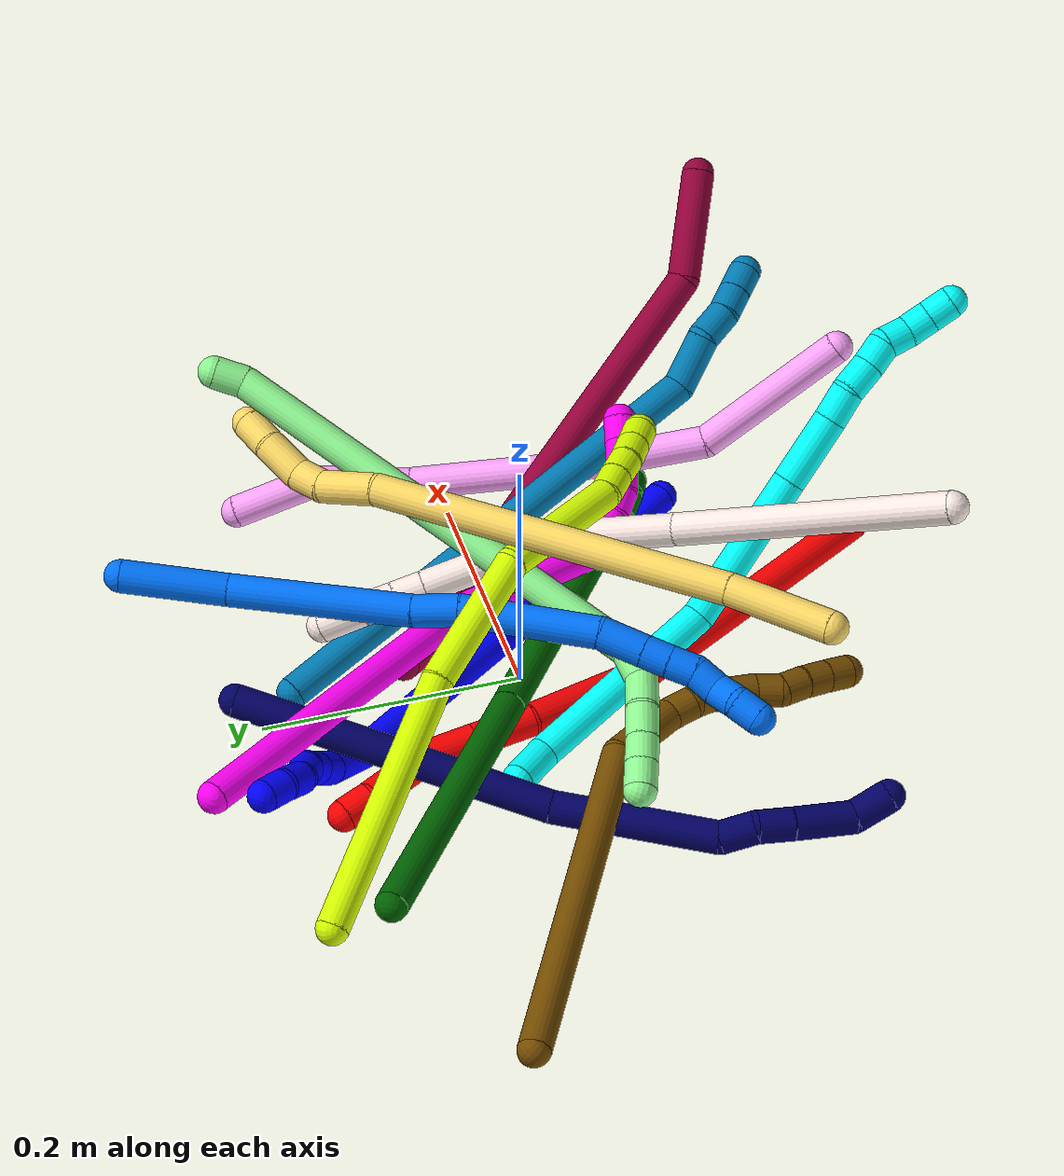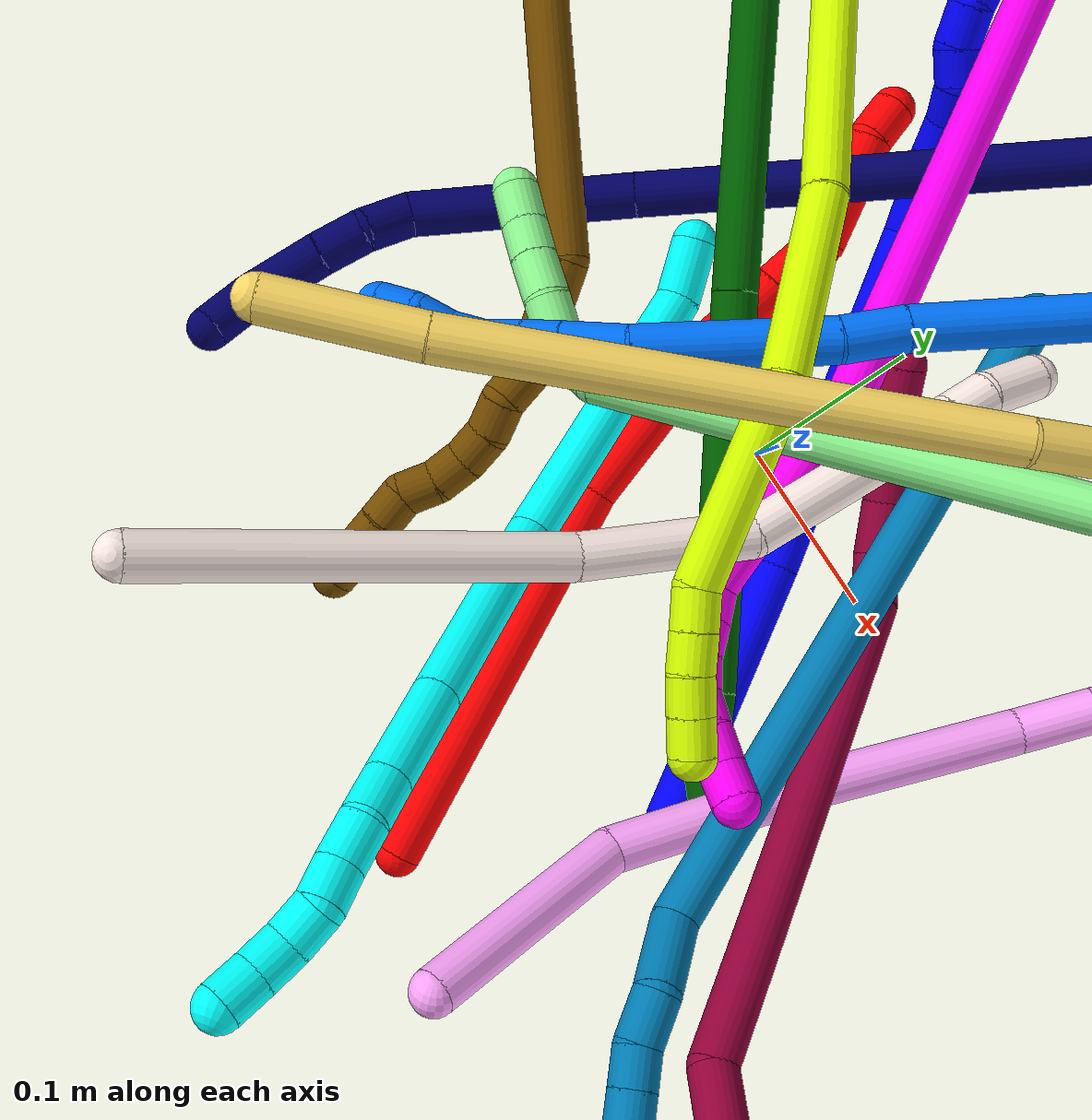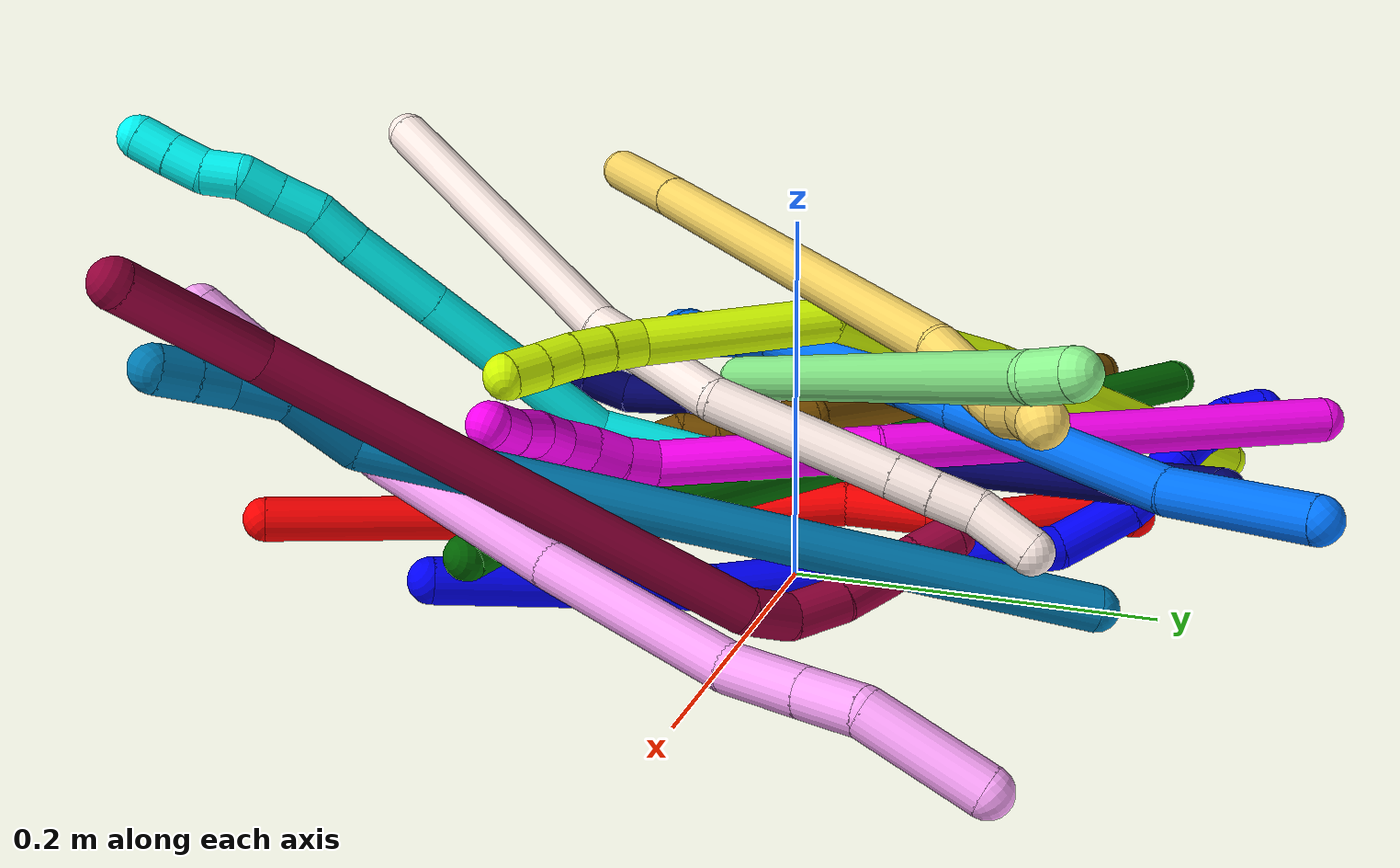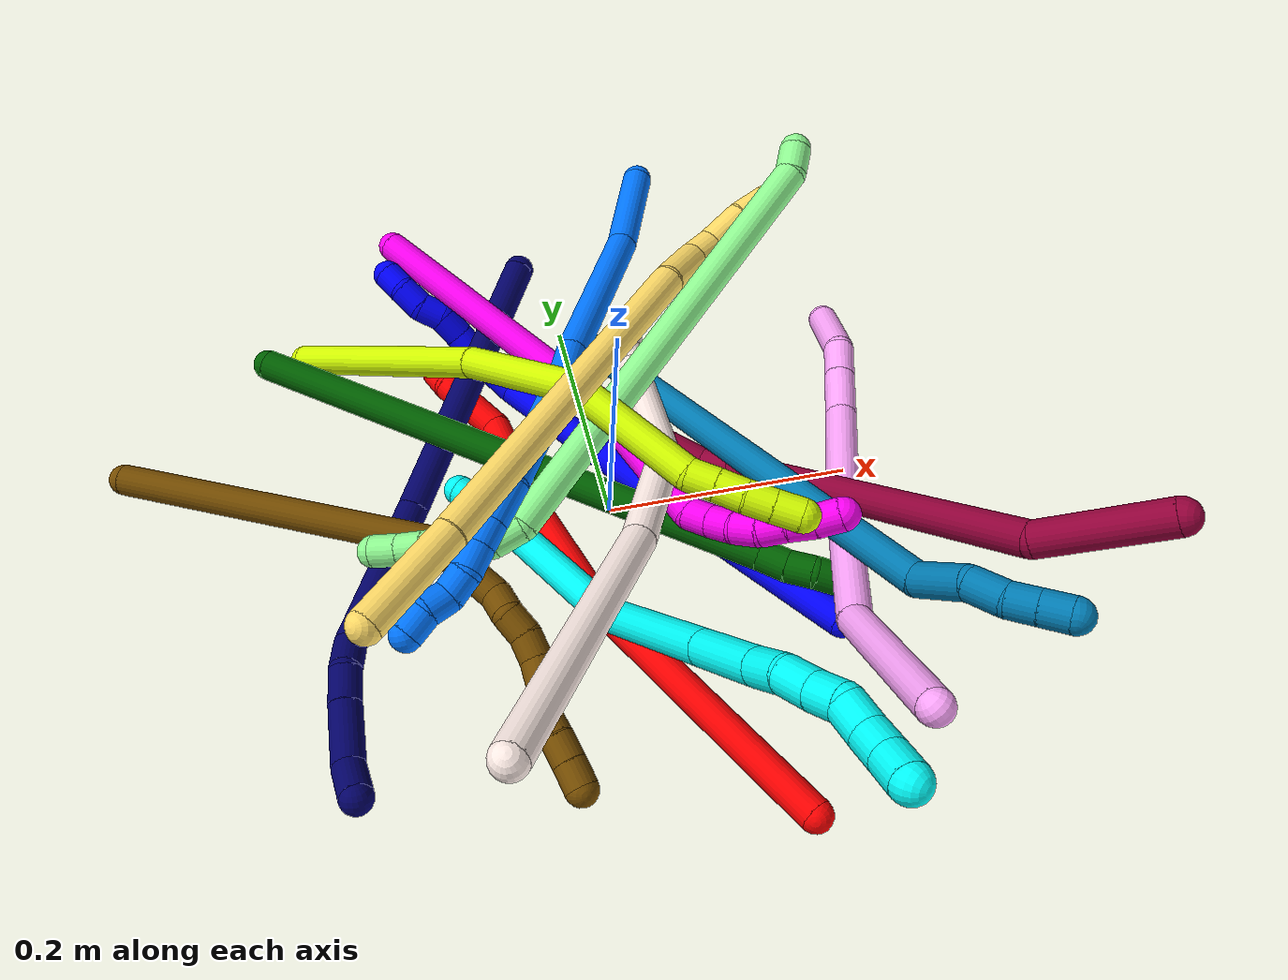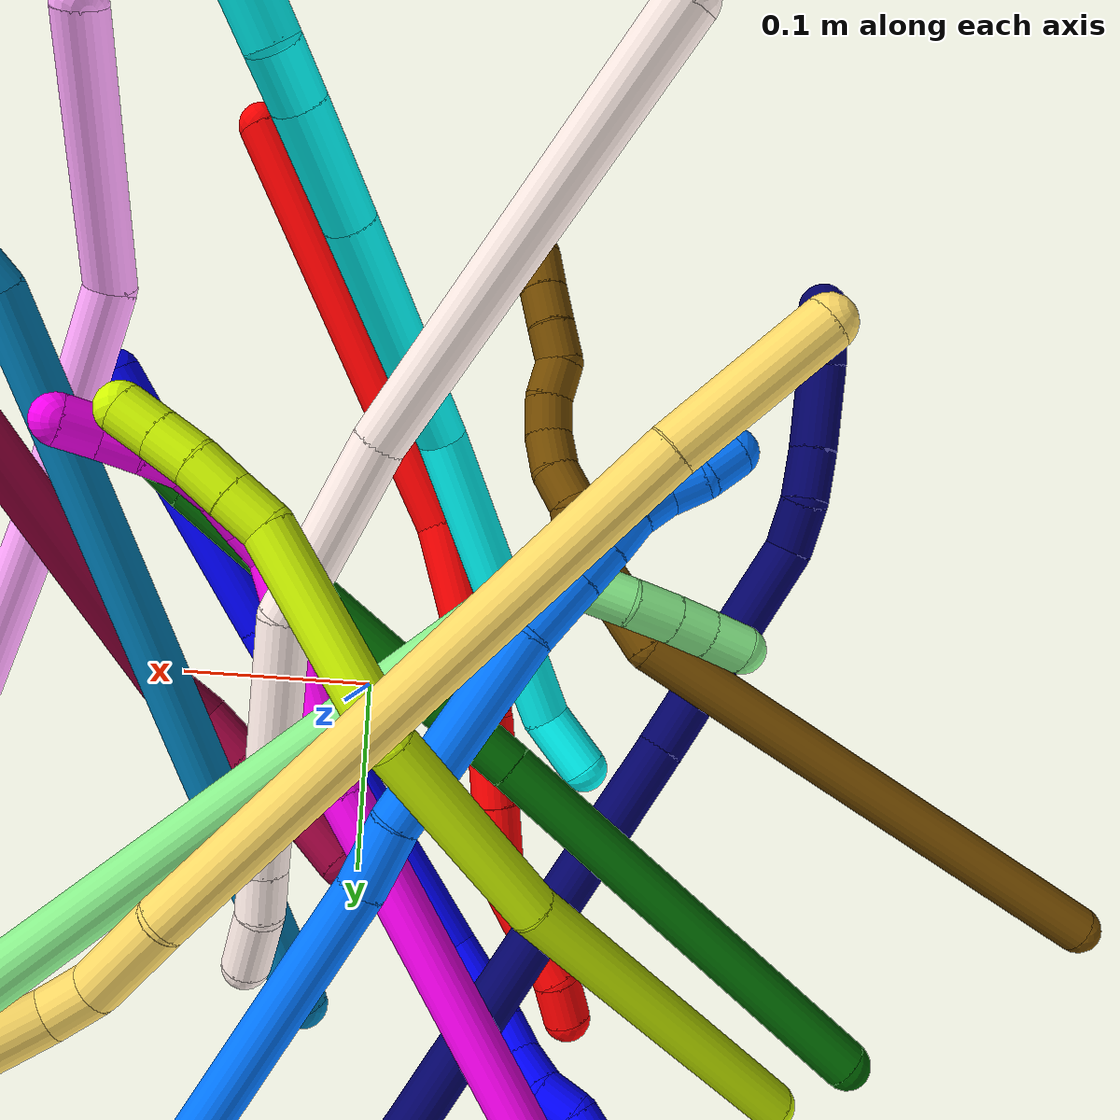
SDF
<sdf version="1.7">
 <world name="default">
  <plugin name="TubeGeneratorPlugin" filename="libtube_generator_plugin.so"/>
  <model name="photoneo_s_sensor">
   <static>1</static>
   <pose>0 0 2 1.57079 1.57079 3.14159</pose>
   <link name="link">
    <inertial><mass>0.1</mass></inertial>
    <sensor name="sensor" type="depth">
     <update_rate>30</update_rate>
     <camera>
      <horizontal_fov>1.22</horizontal_fov>
      <image><width>1920</width><height>1200</height><format>B8G8R8</format></image>
      <clip><near>0.1</near><far>4</far></clip>
      <depth_camera><output>points</output></depth_camera>
     </camera>
     <plugin name="camera_plugin" filename="libgazebo_ros_depth_camera.so">
      <baseline>0.2</baseline>
      <alwaysOn>1</alwaysOn>
      <updateRate>0.0</updateRate>
      <cameraName>camera_ir</cameraName>
      <imageTopicName>/camera/color/image_raw</imageTopicName>
      <cameraInfoTopicName>/camera/color/camera_info</cameraInfoTopicName>
      <depthImageTopicName>/camera/depth/image_raw</depthImageTopicName>
      <depthImageCameraInfoTopicName>/camera/depth/camera_info</depthImageCameraInfoTopicName>
      <pointCloudTopicName>/camera/depth/points</pointCloudTopicName>
      <frameName>fr_optical</frameName>
      <pointCloudCutoff>0.1</pointCloudCutoff>
      <pointCloudCutoffMax>2.0</pointCloudCutoffMax>
      <distortionK1>0</distortionK1>
      <distortionK2>0</distortionK2>
      <distortionK3>0</distortionK3>
      <distortionT1>0</distortionT1>
      <distortionT2>0</distortionT2>
      <CxPrime>0</CxPrime>
      <Cx>0</Cx>
      <Cy>0</Cy>
      <focalLength>0</focalLength>
      <hackBaseline>0</hackBaseline>
     </plugin>
    </sensor>
   </link>
  </model>
  <gravity>0 0 -9.8</gravity>
  <magnetic_field>6e-06 2.3e-05 -4.2e-05</magnetic_field>
  <atmosphere type="adiabatic"/>
  <physics name="default_physics" default="0" type="ode">
   <max_step_size>0.003</max_step_size>
   <real_time_factor>1</real_time_factor>
   <real_time_update_rate>1000</real_time_update_rate>
   <max_contacts>10000</max_contacts>
   <ode>
    <solver>
     <type>quick</type>
     <iters>100</iters>
     <sor>1.3</sor>
     <use_dynamic_moi_rescaling>0</use_dynamic_moi_rescaling>
    </solver>
    <constraints>
     <contact_max_correcting_vel>0</contact_max_correcting_vel>
     <contact_surface_layer>0.001</contact_surface_layer>
     <cfm>0</cfm>
     <erp>0.2</erp>
    </constraints>
   </ode>
  </physics>
  <scene><ambient>0.4 0.4 0.4 1</ambient><background>0.7 0.7 0.7 1</background><shadows>0</shadows></scene>
  <audio><device>default</device></audio>
  <spherical_coordinates>
   <surface_model>EARTH_WGS84</surface_model>
   <latitude_deg>0</latitude_deg>
   <longitude_deg>0</longitude_deg>
   <elevation>0</elevation>
   <heading_deg>0</heading_deg>
  </spherical_coordinates>
  <model name="bin">
   <static>1</static>
   <link name="bottom">
    <collision name="collision-bottom">
     <pose>0 0 -0.01 0 -0 0</pose>
     <geometry><box><size>0.8 0.6 0.02</size></box></geometry>
     <surface>
      <friction><ode><mu>100</mu><mu2>100</mu2></ode></friction>
      <contact><collide_bitmask>65535</collide_bitmask></contact>
     </surface>
    </collision>
   </link>
   <link name="west_wall">
    <collision name="collision-west_wall">
     <pose>-0.41 0 0.1 0 -0 0</pose>
     <geometry><box><size>0.02 0.6 0.2</size></box></geometry>
     <surface>
      <friction><ode><mu>100</mu><mu2>100</mu2></ode></friction>
      <contact><collide_bitmask>65535</collide_bitmask></contact>
     </surface>
    </collision>
   </link>
   <link name="east_wall">
    <collision name="collision-east_wall">
     <pose>0.41 0 0.1 0 -0 0</pose>
     <geometry><box><size>0.02 0.6 0.2</size></box></geometry>
     <surface>
      <friction><ode><mu>100</mu><mu2>100</mu2></ode></friction>
      <contact><collide_bitmask>65535</collide_bitmask></contact>
     </surface>
    </collision>
   </link>
   <link name="south_wall">
    <collision name="collision-south_wall">
     <pose>0 -0.31 0.1 0 -0 0</pose>
     <geometry><box><size>0.8 0.02 0.2</size></box></geometry>
     <surface>
      <friction><ode><mu>100</mu><mu2>100</mu2></ode></friction>
      <contact><collide_bitmask>65535</collide_bitmask></contact>
     </surface>
    </collision>
   </link>
   <link name="north_wall">
    <collision name="collision-north_wall">
     <pose>0 0.31 0.1 0 -0 0</pose>
     <geometry><box><size>0.8 0.02 0.2</size></box></geometry>
     <surface>
      <friction><ode><mu>100</mu><mu2>100</mu2></ode></friction>
      <contact><collide_bitmask>65535</collide_bitmask></contact>
     </surface>
    </collision>
   </link>
  </model>
  <model name="1">
   <static>0</static>
   <link name="1">
    <collision name="collision-cylinder-e_1_1_4">
     <pose>-0.018305 0.046667 -0.056729 -2.4532 -0.244213 0.659672</pose>
     <geometry><cylinder><radius>0.0125</radius><length>0.151408</length></cylinder></geometry>
     <surface>
      <friction><ode><mu>1.16</mu><mu2>1.16</mu2><slip1>0</slip1><slip2>0</slip2></ode></friction>
      <contact><ode><kp>1e+06</kp><kd>1</kd><max_vel>0</max_vel><min_depth>0.001</min_depth></ode></contact>
     </surface>
    </collision>
    <visual name="visual-cylinder-e_1_1_4">
     <pose>-0.018305 0.046667 -0.056729 -2.4532 -0.244213 0.659672</pose>
     <geometry><cylinder><radius>0.0125</radius><length>0.151408</length></cylinder></geometry>
     <material><ambient>0 0 1 1</ambient></material>
    </visual>
    <collision name="collision-cylinder-e_2_4_5">
     <pose>-0.071039 0.157884 -0.180036 -2.37166 -0.35551 0.834674</pose>
     <geometry><cylinder><radius>0.0125</radius><length>0.197835</length></cylinder></geometry>
     <surface>
      <friction><ode><mu>1.16</mu><mu2>1.16</mu2><slip1>0</slip1><slip2>0</slip2></ode></friction>
      <contact><ode><kp>1e+06</kp><kd>1</kd><max_vel>0</max_vel><min_depth>0.001</min_depth></ode></contact>
     </surface>
    </collision>
    <visual name="visual-cylinder-e_2_4_5">
     <pose>-0.071039 0.157884 -0.180036 -2.37166 -0.35551 0.834674</pose>
     <geometry><cylinder><radius>0.0125</radius><length>0.197835</length></cylinder></geometry>
     <material><ambient>0 0 1 1</ambient></material>
    </visual>
    <collision name="collision-cylinder-e_3_5_6">
     <pose>-0.118831 0.239199 -0.255804 -2.07226 -0.609966 0.977188</pose>
     <geometry><cylinder><radius>0.0125</radius><length>0.046651</length></cylinder></geometry>
     <surface>
      <friction><ode><mu>1.16</mu><mu2>1.16</mu2><slip1>0</slip1><slip2>0</slip2></ode></friction>
      <contact><ode><kp>1e+06</kp><kd>1</kd><max_vel>0</max_vel><min_depth>0.001</min_depth></ode></contact>
     </surface>
    </collision>
    <visual name="visual-cylinder-e_3_5_6">
     <pose>-0.118831 0.239199 -0.255804 -2.07226 -0.609966 0.977188</pose>
     <geometry><cylinder><radius>0.0125</radius><length>0.046651</length></cylinder></geometry>
     <material><ambient>0 0 1 1</ambient></material>
    </visual>
    <collision name="collision-cylinder-e_4_6_7">
     <pose>-0.138747 0.26384 -0.266233 -1.72675 -0.688065 0.793581</pose>
     <geometry><cylinder><radius>0.0125</radius><length>0.020643</length></cylinder></geometry>
     <surface>
      <friction><ode><mu>1.16</mu><mu2>1.16</mu2><slip1>0</slip1><slip2>0</slip2></ode></friction>
      <contact><ode><kp>1e+06</kp><kd>1</kd><max_vel>0</max_vel><min_depth>0.001</min_depth></ode></contact>
     </surface>
    </collision>
    <visual name="visual-cylinder-e_4_6_7">
     <pose>-0.138747 0.26384 -0.266233 -1.72675 -0.688065 0.793581</pose>
     <geometry><cylinder><radius>0.0125</radius><length>0.020643</length></cylinder></geometry>
     <material><ambient>0 0 1 1</ambient></material>
    </visual>
    <collision name="collision-cylinder-e_5_7_8">
     <pose>-0.153283 0.278652 -0.267807 -1.61912 -0.854834 0.891884</pose>
     <geometry><cylinder><radius>0.0125</radius><length>0.021158</length></cylinder></geometry>
     <surface>
      <friction><ode><mu>1.16</mu><mu2>1.16</mu2><slip1>0</slip1><slip2>0</slip2></ode></friction>
      <contact><ode><kp>1e+06</kp><kd>1</kd><max_vel>0</max_vel><min_depth>0.001</min_depth></ode></contact>
     </surface>
    </collision>
    <visual name="visual-cylinder-e_5_7_8">
     <pose>-0.153283 0.278652 -0.267807 -1.61912 -0.854834 0.891884</pose>
     <geometry><cylinder><radius>0.0125</radius><length>0.021158</length></cylinder></geometry>
     <material><ambient>0 0 1 1</ambient></material>
    </visual>
    <collision name="collision-cylinder-e_6_8_9">
     <pose>-0.169573 0.289839 -0.271946 -2.30055 -0.969109 1.73316</pose>
     <geometry><cylinder><radius>0.0125</radius><length>0.020156</length></cylinder></geometry>
     <surface>
      <friction><ode><mu>1.16</mu><mu2>1.16</mu2><slip1>0</slip1><slip2>0</slip2></ode></friction>
      <contact><ode><kp>1e+06</kp><kd>1</kd><max_vel>0</max_vel><min_depth>0.001</min_depth></ode></contact>
     </surface>
    </collision>
    <visual name="visual-cylinder-e_6_8_9">
     <pose>-0.169573 0.289839 -0.271946 -2.30055 -0.969109 1.73316</pose>
     <geometry><cylinder><radius>0.0125</radius><length>0.020156</length></cylinder></geometry>
     <material><ambient>0 0 1 1</ambient></material>
    </visual>
    <collision name="collision-cylinder-e_7_9_10">
     <pose>-0.184426 0.302089 -0.279612 -2.02076 -0.635049 0.964873</pose>
     <geometry><cylinder><radius>0.0125</radius><length>0.022066</length></cylinder></geometry>
     <surface>
      <friction><ode><mu>1.16</mu><mu2>1.16</mu2><slip1>0</slip1><slip2>0</slip2></ode></friction>
      <contact><ode><kp>1e+06</kp><kd>1</kd><max_vel>0</max_vel><min_depth>0.001</min_depth></ode></contact>
     </surface>
    </collision>
    <visual name="visual-cylinder-e_7_9_10">
     <pose>-0.184426 0.302089 -0.279612 -2.02076 -0.635049 0.964873</pose>
     <geometry><cylinder><radius>0.0125</radius><length>0.022066</length></cylinder></geometry>
     <material><ambient>0 0 1 1</ambient></material>
    </visual>
    <collision name="collision-cylinder-e_8_10_2">
     <pose>-0.194677 0.317673 -0.28891 -2.19249 -0.378011 0.712924</pose>
     <geometry><cylinder><radius>0.0125</radius><length>0.020084</length></cylinder></geometry>
     <surface>
      <friction><ode><mu>1.16</mu><mu2>1.16</mu2><slip1>0</slip1><slip2>0</slip2></ode></friction>
      <contact><ode><kp>1e+06</kp><kd>1</kd><max_vel>0</max_vel><min_depth>0.001</min_depth></ode></contact>
     </surface>
    </collision>
    <visual name="visual-cylinder-e_8_10_2">
     <pose>-0.194677 0.317673 -0.28891 -2.19249 -0.378011 0.712924</pose>
     <geometry><cylinder><radius>0.0125</radius><length>0.020084</length></cylinder></geometry>
     <material><ambient>0 0 1 1</ambient></material>
    </visual>
    <collision name="collision-sphere-2">
     <pose>-0.198383 0.32526 -0.294346 0 -0 0</pose>
     <geometry><sphere><radius>0.0125</radius></sphere></geometry>
     <surface>
      <friction><ode><mu>1.16</mu><mu2>1.16</mu2><slip1>0</slip1><slip2>0</slip2></ode></friction>
      <contact><ode><kp>1e+06</kp><kd>1</kd><max_vel>0</max_vel><min_depth>0.001</min_depth></ode></contact>
     </surface>
    </collision>
    <visual name="visual-sphere-2">
     <pose>-0.198383 0.32526 -0.294346 0 -0 0</pose>
     <geometry><sphere><radius>0.0125</radius></sphere></geometry>
     <material><ambient>0 0 1 1</ambient></material>
    </visual>
    <collision name="collision-sphere-10">
     <pose>-0.190971 0.310087 -0.283475 0 -0 0</pose>
     <geometry><sphere><radius>0.0125</radius></sphere></geometry>
     <surface>
      <friction><ode><mu>1.16</mu><mu2>1.16</mu2><slip1>0</slip1><slip2>0</slip2></ode></friction>
      <contact><ode><kp>1e+06</kp><kd>1</kd><max_vel>0</max_vel><min_depth>0.001</min_depth></ode></contact>
     </surface>
    </collision>
    <visual name="visual-sphere-10">
     <pose>-0.190971 0.310087 -0.283475 0 -0 0</pose>
     <geometry><sphere><radius>0.0125</radius></sphere></geometry>
     <material><ambient>0 0 1 1</ambient></material>
    </visual>
    <collision name="collision-sphere-9">
     <pose>-0.177881 0.294091 -0.275749 0 -0 0</pose>
     <geometry><sphere><radius>0.0125</radius></sphere></geometry>
     <surface>
      <friction><ode><mu>1.16</mu><mu2>1.16</mu2><slip1>0</slip1><slip2>0</slip2></ode></friction>
      <contact><ode><kp>1e+06</kp><kd>1</kd><max_vel>0</max_vel><min_depth>0.001</min_depth></ode></contact>
     </surface>
    </collision>
    <visual name="visual-sphere-9">
     <pose>-0.177881 0.294091 -0.275749 0 -0 0</pose>
     <geometry><sphere><radius>0.0125</radius></sphere></geometry>
     <material><ambient>0 0 1 1</ambient></material>
    </visual>
    <collision name="collision-sphere-4">
     <pose>-0.036609 0.093334 -0.113458 0 -0 0</pose>
     <geometry><sphere><radius>0.0125</radius></sphere></geometry>
     <surface>
      <friction><ode><mu>1.16</mu><mu2>1.16</mu2><slip1>0</slip1><slip2>0</slip2></ode></friction>
      <contact><ode><kp>1e+06</kp><kd>1</kd><max_vel>0</max_vel><min_depth>0.001</min_depth></ode></contact>
     </surface>
    </collision>
    <visual name="visual-sphere-4">
     <pose>-0.036609 0.093334 -0.113458 0 -0 0</pose>
     <geometry><sphere><radius>0.0125</radius></sphere></geometry>
     <material><ambient>0 0 1 1</ambient></material>
    </visual>
    <collision name="collision-sphere-1">
     <geometry><sphere><radius>0.0125</radius></sphere></geometry>
     <surface>
      <friction><ode><mu>1.16</mu><mu2>1.16</mu2><slip1>0</slip1><slip2>0</slip2></ode></friction>
      <contact><ode><kp>1e+06</kp><kd>1</kd><max_vel>0</max_vel><min_depth>0.001</min_depth></ode></contact>
     </surface>
    </collision>
    <visual name="visual-sphere-1">
     <geometry><sphere><radius>0.0125</radius></sphere></geometry>
     <material><ambient>0 0 1 1</ambient></material>
    </visual>
    <collision name="collision-sphere-8">
     <pose>-0.161265 0.285587 -0.268143 0 -0 0</pose>
     <geometry><sphere><radius>0.0125</radius></sphere></geometry>
     <surface>
      <friction><ode><mu>1.16</mu><mu2>1.16</mu2><slip1>0</slip1><slip2>0</slip2></ode></friction>
      <contact><ode><kp>1e+06</kp><kd>1</kd><max_vel>0</max_vel><min_depth>0.001</min_depth></ode></contact>
     </surface>
    </collision>
    <visual name="visual-sphere-8">
     <pose>-0.161265 0.285587 -0.268143 0 -0 0</pose>
     <geometry><sphere><radius>0.0125</radius></sphere></geometry>
     <material><ambient>0 0 1 1</ambient></material>
    </visual>
    <collision name="collision-sphere-5">
     <pose>-0.105469 0.222434 -0.246614 0 -0 0</pose>
     <geometry><sphere><radius>0.0125</radius></sphere></geometry>
     <surface>
      <friction><ode><mu>1.16</mu><mu2>1.16</mu2><slip1>0</slip1><slip2>0</slip2></ode></friction>
      <contact><ode><kp>1e+06</kp><kd>1</kd><max_vel>0</max_vel><min_depth>0.001</min_depth></ode></contact>
     </surface>
    </collision>
    <visual name="visual-sphere-5">
     <pose>-0.105469 0.222434 -0.246614 0 -0 0</pose>
     <geometry><sphere><radius>0.0125</radius></sphere></geometry>
     <material><ambient>0 0 1 1</ambient></material>
    </visual>
    <collision name="collision-sphere-6">
     <pose>-0.132193 0.255964 -0.264995 0 -0 0</pose>
     <geometry><sphere><radius>0.0125</radius></sphere></geometry>
     <surface>
      <friction><ode><mu>1.16</mu><mu2>1.16</mu2><slip1>0</slip1><slip2>0</slip2></ode></friction>
      <contact><ode><kp>1e+06</kp><kd>1</kd><max_vel>0</max_vel><min_depth>0.001</min_depth></ode></contact>
     </surface>
    </collision>
    <visual name="visual-sphere-6">
     <pose>-0.132193 0.255964 -0.264995 0 -0 0</pose>
     <geometry><sphere><radius>0.0125</radius></sphere></geometry>
     <material><ambient>0 0 1 1</ambient></material>
    </visual>
    <collision name="collision-sphere-7">
     <pose>-0.145302 0.271716 -0.267472 0 -0 0</pose>
     <geometry><sphere><radius>0.0125</radius></sphere></geometry>
     <surface>
      <friction><ode><mu>1.16</mu><mu2>1.16</mu2><slip1>0</slip1><slip2>0</slip2></ode></friction>
      <contact><ode><kp>1e+06</kp><kd>1</kd><max_vel>0</max_vel><min_depth>0.001</min_depth></ode></contact>
     </surface>
    </collision>
    <visual name="visual-sphere-7">
     <pose>-0.145302 0.271716 -0.267472 0 -0 0</pose>
     <geometry><sphere><radius>0.0125</radius></sphere></geometry>
     <material><ambient>0 0 1 1</ambient></material>
    </visual>
    <inertial>
     <pose>-0.079747 0.159379 -0.169512 0 -0 0</pose>
     <mass>0.5</mass>
     <inertia>
      <ixx>0.00127</ixx>
      <ixy>0</ixy>
      <ixz>0</ixz>
      <iyy>0.00032</iyy>
      <iyz>0</iyz>
      <izz>-0.000334</izz>
     </inertia>
    </inertial>
   </link>
   <pose>0.137856 -0.154177 0.03082 0.561752 0.567998 0.182253</pose>
  </model>
  <model name="2">
   <static>0</static>
   <link name="2">
    <collision name="collision-cylinder-e_1_1_4">
     <pose>-0.050214 0.088475 -0.049893 -2.08426 -0.45913 0.761117</pose>
     <geometry><cylinder><radius>0.0125</radius><length>0.226615</length></cylinder></geometry>
     <surface>
      <friction><ode><mu>1.16</mu><mu2>1.16</mu2><slip1>0</slip1><slip2>0</slip2></ode></friction>
      <contact><ode><kp>1e+06</kp><kd>1</kd><max_vel>0</max_vel><min_depth>0.001</min_depth></ode></contact>
     </surface>
    </collision>
    <visual name="visual-cylinder-e_1_1_4">
     <pose>-0.050214 0.088475 -0.049893 -2.08426 -0.45913 0.761117</pose>
     <geometry><cylinder><radius>0.0125</radius><length>0.226615</length></cylinder></geometry>
     <material><ambient>1 0 0 1</ambient></material>
    </visual>
    <collision name="collision-cylinder-e_2_4_5">
     <pose>-0.113602 0.221537 -0.122796 -2.04722 -0.256749 0.41758</pose>
     <geometry><cylinder><radius>0.0125</radius><length>0.103749</length></cylinder></geometry>
     <surface>
      <friction><ode><mu>1.16</mu><mu2>1.16</mu2><slip1>0</slip1><slip2>0</slip2></ode></friction>
      <contact><ode><kp>1e+06</kp><kd>1</kd><max_vel>0</max_vel><min_depth>0.001</min_depth></ode></contact>
     </surface>
    </collision>
    <visual name="visual-cylinder-e_2_4_5">
     <pose>-0.113602 0.221537 -0.122796 -2.04722 -0.256749 0.41758</pose>
     <geometry><cylinder><radius>0.0125</radius><length>0.103749</length></cylinder></geometry>
     <material><ambient>1 0 0 1</ambient></material>
    </visual>
    <collision name="collision-cylinder-e_3_5_6">
     <pose>-0.130388 0.284228 -0.160364 -2.24803 -0.154285 0.319919</pose>
     <geometry><cylinder><radius>0.0125</radius><length>0.047022</length></cylinder></geometry>
     <surface>
      <friction><ode><mu>1.16</mu><mu2>1.16</mu2><slip1>0</slip1><slip2>0</slip2></ode></friction>
      <contact><ode><kp>1e+06</kp><kd>1</kd><max_vel>0</max_vel><min_depth>0.001</min_depth></ode></contact>
     </surface>
    </collision>
    <visual name="visual-cylinder-e_3_5_6">
     <pose>-0.130388 0.284228 -0.160364 -2.24803 -0.154285 0.319919</pose>
     <geometry><cylinder><radius>0.0125</radius><length>0.047022</length></cylinder></geometry>
     <material><ambient>1 0 0 1</ambient></material>
    </visual>
    <collision name="collision-cylinder-e_4_6_7">
     <pose>-0.13685 0.316576 -0.186668 -2.26044 -0.153138 0.322606</pose>
     <geometry><cylinder><radius>0.0125</radius><length>0.037361</length></cylinder></geometry>
     <surface>
      <friction><ode><mu>1.16</mu><mu2>1.16</mu2><slip1>0</slip1><slip2>0</slip2></ode></friction>
      <contact><ode><kp>1e+06</kp><kd>1</kd><max_vel>0</max_vel><min_depth>0.001</min_depth></ode></contact>
     </surface>
    </collision>
    <visual name="visual-cylinder-e_4_6_7">
     <pose>-0.13685 0.316576 -0.186668 -2.26044 -0.153138 0.322606</pose>
     <geometry><cylinder><radius>0.0125</radius><length>0.037361</length></cylinder></geometry>
     <material><ambient>1 0 0 1</ambient></material>
    </visual>
    <collision name="collision-cylinder-e_5_7_8">
     <pose>-0.15405 0.356534 -0.20882 -1.95529 -0.477394 0.692819</pose>
     <geometry><cylinder><radius>0.0125</radius><length>0.062466</length></cylinder></geometry>
     <surface>
      <friction><ode><mu>1.16</mu><mu2>1.16</mu2><slip1>0</slip1><slip2>0</slip2></ode></friction>
      <contact><ode><kp>1e+06</kp><kd>1</kd><max_vel>0</max_vel><min_depth>0.001</min_depth></ode></contact>
     </surface>
    </collision>
    <visual name="visual-cylinder-e_5_7_8">
     <pose>-0.15405 0.356534 -0.20882 -1.95529 -0.477394 0.692819</pose>
     <geometry><cylinder><radius>0.0125</radius><length>0.062466</length></cylinder></geometry>
     <material><ambient>1 0 0 1</ambient></material>
    </visual>
    <collision name="collision-cylinder-e_6_8_2">
     <pose>-0.172651 0.390107 -0.226298 -2.30367 -0.382337 0.819918</pose>
     <geometry><cylinder><radius>0.0125</radius><length>0.022786</length></cylinder></geometry>
     <surface>
      <friction><ode><mu>1.16</mu><mu2>1.16</mu2><slip1>0</slip1><slip2>0</slip2></ode></friction>
      <contact><ode><kp>1e+06</kp><kd>1</kd><max_vel>0</max_vel><min_depth>0.001</min_depth></ode></contact>
     </surface>
    </collision>
    <visual name="visual-cylinder-e_6_8_2">
     <pose>-0.172651 0.390107 -0.226298 -2.30367 -0.382337 0.819918</pose>
     <geometry><cylinder><radius>0.0125</radius><length>0.022786</length></cylinder></geometry>
     <material><ambient>1 0 0 1</ambient></material>
    </visual>
    <collision name="collision-sphere-2">
     <pose>-0.176902 0.397963 -0.233369 0 -0 0</pose>
     <geometry><sphere><radius>0.0125</radius></sphere></geometry>
     <surface>
      <friction><ode><mu>1.16</mu><mu2>1.16</mu2><slip1>0</slip1><slip2>0</slip2></ode></friction>
      <contact><ode><kp>1e+06</kp><kd>1</kd><max_vel>0</max_vel><min_depth>0.001</min_depth></ode></contact>
     </surface>
    </collision>
    <visual name="visual-sphere-2">
     <pose>-0.176902 0.397963 -0.233369 0 -0 0</pose>
     <geometry><sphere><radius>0.0125</radius></sphere></geometry>
     <material><ambient>1 0 0 1</ambient></material>
    </visual>
    <collision name="collision-sphere-4">
     <pose>-0.100429 0.17695 -0.099786 0 -0 0</pose>
     <geometry><sphere><radius>0.0125</radius></sphere></geometry>
     <surface>
      <friction><ode><mu>1.16</mu><mu2>1.16</mu2><slip1>0</slip1><slip2>0</slip2></ode></friction>
      <contact><ode><kp>1e+06</kp><kd>1</kd><max_vel>0</max_vel><min_depth>0.001</min_depth></ode></contact>
     </surface>
    </collision>
    <visual name="visual-sphere-4">
     <pose>-0.100429 0.17695 -0.099786 0 -0 0</pose>
     <geometry><sphere><radius>0.0125</radius></sphere></geometry>
     <material><ambient>1 0 0 1</ambient></material>
    </visual>
    <collision name="collision-sphere-1">
     <geometry><sphere><radius>0.0125</radius></sphere></geometry>
     <surface>
      <friction><ode><mu>1.16</mu><mu2>1.16</mu2><slip1>0</slip1><slip2>0</slip2></ode></friction>
      <contact><ode><kp>1e+06</kp><kd>1</kd><max_vel>0</max_vel><min_depth>0.001</min_depth></ode></contact>
     </surface>
    </collision>
    <visual name="visual-sphere-1">
     <geometry><sphere><radius>0.0125</radius></sphere></geometry>
     <material><ambient>1 0 0 1</ambient></material>
    </visual>
    <collision name="collision-sphere-8">
     <pose>-0.168401 0.38225 -0.219226 0 -0 0</pose>
     <geometry><sphere><radius>0.0125</radius></sphere></geometry>
     <surface>
      <friction><ode><mu>1.16</mu><mu2>1.16</mu2><slip1>0</slip1><slip2>0</slip2></ode></friction>
      <contact><ode><kp>1e+06</kp><kd>1</kd><max_vel>0</max_vel><min_depth>0.001</min_depth></ode></contact>
     </surface>
    </collision>
    <visual name="visual-sphere-8">
     <pose>-0.168401 0.38225 -0.219226 0 -0 0</pose>
     <geometry><sphere><radius>0.0125</radius></sphere></geometry>
     <material><ambient>1 0 0 1</ambient></material>
    </visual>
    <collision name="collision-sphere-5">
     <pose>-0.126774 0.266123 -0.145806 0 -0 0</pose>
     <geometry><sphere><radius>0.0125</radius></sphere></geometry>
     <surface>
      <friction><ode><mu>1.16</mu><mu2>1.16</mu2><slip1>0</slip1><slip2>0</slip2></ode></friction>
      <contact><ode><kp>1e+06</kp><kd>1</kd><max_vel>0</max_vel><min_depth>0.001</min_depth></ode></contact>
     </surface>
    </collision>
    <visual name="visual-sphere-5">
     <pose>-0.126774 0.266123 -0.145806 0 -0 0</pose>
     <geometry><sphere><radius>0.0125</radius></sphere></geometry>
     <material><ambient>1 0 0 1</ambient></material>
    </visual>
    <collision name="collision-sphere-6">
     <pose>-0.134001 0.302333 -0.174922 0 -0 0</pose>
     <geometry><sphere><radius>0.0125</radius></sphere></geometry>
     <surface>
      <friction><ode><mu>1.16</mu><mu2>1.16</mu2><slip1>0</slip1><slip2>0</slip2></ode></friction>
      <contact><ode><kp>1e+06</kp><kd>1</kd><max_vel>0</max_vel><min_depth>0.001</min_depth></ode></contact>
     </surface>
    </collision>
    <visual name="visual-sphere-6">
     <pose>-0.134001 0.302333 -0.174922 0 -0 0</pose>
     <geometry><sphere><radius>0.0125</radius></sphere></geometry>
     <material><ambient>1 0 0 1</ambient></material>
    </visual>
    <collision name="collision-sphere-7">
     <pose>-0.1397 0.330819 -0.198415 0 -0 0</pose>
     <geometry><sphere><radius>0.0125</radius></sphere></geometry>
     <surface>
      <friction><ode><mu>1.16</mu><mu2>1.16</mu2><slip1>0</slip1><slip2>0</slip2></ode></friction>
      <contact><ode><kp>1e+06</kp><kd>1</kd><max_vel>0</max_vel><min_depth>0.001</min_depth></ode></contact>
     </surface>
    </collision>
    <visual name="visual-sphere-7">
     <pose>-0.1397 0.330819 -0.198415 0 -0 0</pose>
     <geometry><sphere><radius>0.0125</radius></sphere></geometry>
     <material><ambient>1 0 0 1</ambient></material>
    </visual>
    <inertial>
     <pose>-0.095933 0.198774 -0.113524 0 -0 0</pose>
     <mass>0.5</mass>
     <inertia>
      <ixx>0.001402</ixx>
      <ixy>0</ixy>
      <ixz>0</ixz>
      <iyy>0.000564</iyy>
      <iyz>0</iyz>
      <izz>-0.000426</izz>
     </inertia>
    </inertial>
   </link>
   <pose>0.072447 -0.287838 0.024132 0.692672 -0.464698 -0.003874</pose>
  </model>
  <model name="3">
   <static>0</static>
   <link name="3">
    <collision name="collision-cylinder-e_1_1_4">
     <pose>0.006016 0.003987 0.015242 -0.25588 0.364738 -0.047439</pose>
     <geometry><cylinder><radius>0.0125</radius><length>0.033728</length></cylinder></geometry>
     <surface>
      <friction><ode><mu>1.16</mu><mu2>1.16</mu2><slip1>0</slip1><slip2>0</slip2></ode></friction>
      <contact><ode><kp>1e+06</kp><kd>1</kd><max_vel>0</max_vel><min_depth>0.001</min_depth></ode></contact>
     </surface>
    </collision>
    <visual name="visual-cylinder-e_1_1_4">
     <pose>0.006016 0.003987 0.015242 -0.25588 0.364738 -0.047439</pose>
     <geometry><cylinder><radius>0.0125</radius><length>0.033728</length></cylinder></geometry>
     <material><ambient>0.003922 1 0.996078 1</ambient></material>
    </visual>
    <collision name="collision-cylinder-e_2_4_5">
     <pose>0.024923 -0.000769 0.108458 0.11167 0.162849 0.009122</pose>
     <geometry><cylinder><radius>0.0125</radius><length>0.159029</length></cylinder></geometry>
     <surface>
      <friction><ode><mu>1.16</mu><mu2>1.16</mu2><slip1>0</slip1><slip2>0</slip2></ode></friction>
      <contact><ode><kp>1e+06</kp><kd>1</kd><max_vel>0</max_vel><min_depth>0.001</min_depth></ode></contact>
     </surface>
    </collision>
    <visual name="visual-cylinder-e_2_4_5">
     <pose>0.024923 -0.000769 0.108458 0.11167 0.162849 0.009122</pose>
     <geometry><cylinder><radius>0.0125</radius><length>0.159029</length></cylinder></geometry>
     <material><ambient>0.003922 1 0.996078 1</ambient></material>
    </visual>
    <collision name="collision-cylinder-e_3_5_6">
     <pose>0.022831 -0.019453 0.244131 0.170615 -0.250529 -0.021536</pose>
     <geometry><cylinder><radius>0.0125</radius><length>0.120872</length></cylinder></geometry>
     <surface>
      <friction><ode><mu>1.16</mu><mu2>1.16</mu2><slip1>0</slip1><slip2>0</slip2></ode></friction>
      <contact><ode><kp>1e+06</kp><kd>1</kd><max_vel>0</max_vel><min_depth>0.001</min_depth></ode></contact>
     </surface>
    </collision>
    <visual name="visual-cylinder-e_3_5_6">
     <pose>0.022831 -0.019453 0.244131 0.170615 -0.250529 -0.021536</pose>
     <geometry><cylinder><radius>0.0125</radius><length>0.120872</length></cylinder></geometry>
     <material><ambient>0.003922 1 0.996078 1</ambient></material>
    </visual>
    <collision name="collision-cylinder-e_4_6_7">
     <pose>0.001021 -0.033886 0.328157 0.168973 -0.250281 -0.021306</pose>
     <geometry><cylinder><radius>0.0125</radius><length>0.055131</length></cylinder></geometry>
     <surface>
      <friction><ode><mu>1.16</mu><mu2>1.16</mu2><slip1>0</slip1><slip2>0</slip2></ode></friction>
      <contact><ode><kp>1e+06</kp><kd>1</kd><max_vel>0</max_vel><min_depth>0.001</min_depth></ode></contact>
     </surface>
    </collision>
    <visual name="visual-cylinder-e_4_6_7">
     <pose>0.001021 -0.033886 0.328157 0.168973 -0.250281 -0.021306</pose>
     <geometry><cylinder><radius>0.0125</radius><length>0.055131</length></cylinder></geometry>
     <material><ambient>0.003922 1 0.996078 1</ambient></material>
    </visual>
    <collision name="collision-cylinder-e_5_7_8">
     <pose>-0.009697 -0.040487 0.366537 0.173288 -0.307798 -0.026947</pose>
     <geometry><cylinder><radius>0.0125</radius><length>0.025681</length></cylinder></geometry>
     <surface>
      <friction><ode><mu>1.16</mu><mu2>1.16</mu2><slip1>0</slip1><slip2>0</slip2></ode></friction>
      <contact><ode><kp>1e+06</kp><kd>1</kd><max_vel>0</max_vel><min_depth>0.001</min_depth></ode></contact>
     </surface>
    </collision>
    <visual name="visual-cylinder-e_5_7_8">
     <pose>-0.009697 -0.040487 0.366537 0.173288 -0.307798 -0.026947</pose>
     <geometry><cylinder><radius>0.0125</radius><length>0.025681</length></cylinder></geometry>
     <material><ambient>0.003922 1 0.996078 1</ambient></material>
    </visual>
    <collision name="collision-cylinder-e_6_8_9">
     <pose>-0.014132 -0.043834 0.390584 0.102764 -0.045152 -0.002322</pose>
     <geometry><cylinder><radius>0.0125</radius><length>0.024138</length></cylinder></geometry>
     <surface>
      <friction><ode><mu>1.16</mu><mu2>1.16</mu2><slip1>0</slip1><slip2>0</slip2></ode></friction>
      <contact><ode><kp>1e+06</kp><kd>1</kd><max_vel>0</max_vel><min_depth>0.001</min_depth></ode></contact>
     </surface>
    </collision>
    <visual name="visual-cylinder-e_6_8_9">
     <pose>-0.014132 -0.043834 0.390584 0.102764 -0.045152 -0.002322</pose>
     <geometry><cylinder><radius>0.0125</radius><length>0.024138</length></cylinder></geometry>
     <material><ambient>0.003922 1 0.996078 1</ambient></material>
    </visual>
    <collision name="collision-cylinder-e_7_9_10">
     <pose>-0.015939 -0.045786 0.412814 0.06978 -0.12247 -0.00428</pose>
     <geometry><cylinder><radius>0.0125</radius><length>0.020681</length></cylinder></geometry>
     <surface>
      <friction><ode><mu>1.16</mu><mu2>1.16</mu2><slip1>0</slip1><slip2>0</slip2></ode></friction>
      <contact><ode><kp>1e+06</kp><kd>1</kd><max_vel>0</max_vel><min_depth>0.001</min_depth></ode></contact>
     </surface>
    </collision>
    <visual name="visual-cylinder-e_7_9_10">
     <pose>-0.015939 -0.045786 0.412814 0.06978 -0.12247 -0.00428</pose>
     <geometry><cylinder><radius>0.0125</radius><length>0.020681</length></cylinder></geometry>
     <material><ambient>0.003922 1 0.996078 1</ambient></material>
    </visual>
    <collision name="collision-cylinder-e_8_10_11">
     <pose>-0.013555 -0.048786 0.432471 0.237982 0.359959 0.043499</pose>
     <geometry><cylinder><radius>0.0125</radius><length>0.020711</length></cylinder></geometry>
     <surface>
      <friction><ode><mu>1.16</mu><mu2>1.16</mu2><slip1>0</slip1><slip2>0</slip2></ode></friction>
      <contact><ode><kp>1e+06</kp><kd>1</kd><max_vel>0</max_vel><min_depth>0.001</min_depth></ode></contact>
     </surface>
    </collision>
    <visual name="visual-cylinder-e_8_10_11">
     <pose>-0.013555 -0.048786 0.432471 0.237982 0.359959 0.043499</pose>
     <geometry><cylinder><radius>0.0125</radius><length>0.020711</length></cylinder></geometry>
     <material><ambient>0.003922 1 0.996078 1</ambient></material>
    </visual>
    <collision name="collision-cylinder-e_9_11_12">
     <pose>-0.00918 -0.05488 0.451109 0.391778 0.072808 0.014454</pose>
     <geometry><cylinder><radius>0.0125</radius><length>0.020003</length></cylinder></geometry>
     <surface>
      <friction><ode><mu>1.16</mu><mu2>1.16</mu2><slip1>0</slip1><slip2>0</slip2></ode></friction>
      <contact><ode><kp>1e+06</kp><kd>1</kd><max_vel>0</max_vel><min_depth>0.001</min_depth></ode></contact>
     </surface>
    </collision>
    <visual name="visual-cylinder-e_9_11_12">
     <pose>-0.00918 -0.05488 0.451109 0.391778 0.072808 0.014454</pose>
     <geometry><cylinder><radius>0.0125</radius><length>0.020003</length></cylinder></geometry>
     <material><ambient>0.003922 1 0.996078 1</ambient></material>
    </visual>
    <collision name="collision-cylinder-e_10_12_2">
     <pose>-0.008091 -0.062814 0.469445 0.424937 0.036117 0.007792</pose>
     <geometry><cylinder><radius>0.0125</radius><length>0.020025</length></cylinder></geometry>
     <surface>
      <friction><ode><mu>1.16</mu><mu2>1.16</mu2><slip1>0</slip1><slip2>0</slip2></ode></friction>
      <contact><ode><kp>1e+06</kp><kd>1</kd><max_vel>0</max_vel><min_depth>0.001</min_depth></ode></contact>
     </surface>
    </collision>
    <visual name="visual-cylinder-e_10_12_2">
     <pose>-0.008091 -0.062814 0.469445 0.424937 0.036117 0.007792</pose>
     <geometry><cylinder><radius>0.0125</radius><length>0.020025</length></cylinder></geometry>
     <material><ambient>0.003922 1 0.996078 1</ambient></material>
    </visual>
    <collision name="collision-sphere-2">
     <pose>-0.007729 -0.066939 0.478561 0 -0 0</pose>
     <geometry><sphere><radius>0.0125</radius></sphere></geometry>
     <surface>
      <friction><ode><mu>1.16</mu><mu2>1.16</mu2><slip1>0</slip1><slip2>0</slip2></ode></friction>
      <contact><ode><kp>1e+06</kp><kd>1</kd><max_vel>0</max_vel><min_depth>0.001</min_depth></ode></contact>
     </surface>
    </collision>
    <visual name="visual-sphere-2">
     <pose>-0.007729 -0.066939 0.478561 0 -0 0</pose>
     <geometry><sphere><radius>0.0125</radius></sphere></geometry>
     <material><ambient>0.003922 1 0.996078 1</ambient></material>
    </visual>
    <collision name="collision-sphere-12">
     <pose>-0.008452 -0.058689 0.460329 0 -0 0</pose>
     <geometry><sphere><radius>0.0125</radius></sphere></geometry>
     <surface>
      <friction><ode><mu>1.16</mu><mu2>1.16</mu2><slip1>0</slip1><slip2>0</slip2></ode></friction>
      <contact><ode><kp>1e+06</kp><kd>1</kd><max_vel>0</max_vel><min_depth>0.001</min_depth></ode></contact>
     </surface>
    </collision>
    <visual name="visual-sphere-12">
     <pose>-0.008452 -0.058689 0.460329 0 -0 0</pose>
     <geometry><sphere><radius>0.0125</radius></sphere></geometry>
     <material><ambient>0.003922 1 0.996078 1</ambient></material>
    </visual>
    <collision name="collision-sphere-11">
     <pose>-0.009907 -0.051071 0.44189 0 -0 0</pose>
     <geometry><sphere><radius>0.0125</radius></sphere></geometry>
     <surface>
      <friction><ode><mu>1.16</mu><mu2>1.16</mu2><slip1>0</slip1><slip2>0</slip2></ode></friction>
      <contact><ode><kp>1e+06</kp><kd>1</kd><max_vel>0</max_vel><min_depth>0.001</min_depth></ode></contact>
     </surface>
    </collision>
    <visual name="visual-sphere-11">
     <pose>-0.009907 -0.051071 0.44189 0 -0 0</pose>
     <geometry><sphere><radius>0.0125</radius></sphere></geometry>
     <material><ambient>0.003922 1 0.996078 1</ambient></material>
    </visual>
    <collision name="collision-sphere-10">
     <pose>-0.017203 -0.046502 0.423052 0 -0 0</pose>
     <geometry><sphere><radius>0.0125</radius></sphere></geometry>
     <surface>
      <friction><ode><mu>1.16</mu><mu2>1.16</mu2><slip1>0</slip1><slip2>0</slip2></ode></friction>
      <contact><ode><kp>1e+06</kp><kd>1</kd><max_vel>0</max_vel><min_depth>0.001</min_depth></ode></contact>
     </surface>
    </collision>
    <visual name="visual-sphere-10">
     <pose>-0.017203 -0.046502 0.423052 0 -0 0</pose>
     <geometry><sphere><radius>0.0125</radius></sphere></geometry>
     <material><ambient>0.003922 1 0.996078 1</ambient></material>
    </visual>
    <collision name="collision-sphere-9">
     <pose>-0.014676 -0.045071 0.402577 0 -0 0</pose>
     <geometry><sphere><radius>0.0125</radius></sphere></geometry>
     <surface>
      <friction><ode><mu>1.16</mu><mu2>1.16</mu2><slip1>0</slip1><slip2>0</slip2></ode></friction>
      <contact><ode><kp>1e+06</kp><kd>1</kd><max_vel>0</max_vel><min_depth>0.001</min_depth></ode></contact>
     </surface>
    </collision>
    <visual name="visual-sphere-9">
     <pose>-0.014676 -0.045071 0.402577 0 -0 0</pose>
     <geometry><sphere><radius>0.0125</radius></sphere></geometry>
     <material><ambient>0.003922 1 0.996078 1</ambient></material>
    </visual>
    <collision name="collision-sphere-4">
     <pose>0.012031 0.007975 0.030484 0 -0 0</pose>
     <geometry><sphere><radius>0.0125</radius></sphere></geometry>
     <surface>
      <friction><ode><mu>1.16</mu><mu2>1.16</mu2><slip1>0</slip1><slip2>0</slip2></ode></friction>
      <contact><ode><kp>1e+06</kp><kd>1</kd><max_vel>0</max_vel><min_depth>0.001</min_depth></ode></contact>
     </surface>
    </collision>
    <visual name="visual-sphere-4">
     <pose>0.012031 0.007975 0.030484 0 -0 0</pose>
     <geometry><sphere><radius>0.0125</radius></sphere></geometry>
     <material><ambient>0.003922 1 0.996078 1</ambient></material>
    </visual>
    <collision name="collision-sphere-1">
     <geometry><sphere><radius>0.0125</radius></sphere></geometry>
     <surface>
      <friction><ode><mu>1.16</mu><mu2>1.16</mu2><slip1>0</slip1><slip2>0</slip2></ode></friction>
      <contact><ode><kp>1e+06</kp><kd>1</kd><max_vel>0</max_vel><min_depth>0.001</min_depth></ode></contact>
     </surface>
    </collision>
    <visual name="visual-sphere-1">
     <geometry><sphere><radius>0.0125</radius></sphere></geometry>
     <material><ambient>0.003922 1 0.996078 1</ambient></material>
    </visual>
    <collision name="collision-sphere-8">
     <pose>-0.013587 -0.042597 0.378591 0 -0 0</pose>
     <geometry><sphere><radius>0.0125</radius></sphere></geometry>
     <surface>
      <friction><ode><mu>1.16</mu><mu2>1.16</mu2><slip1>0</slip1><slip2>0</slip2></ode></friction>
      <contact><ode><kp>1e+06</kp><kd>1</kd><max_vel>0</max_vel><min_depth>0.001</min_depth></ode></contact>
     </surface>
    </collision>
    <visual name="visual-sphere-8">
     <pose>-0.013587 -0.042597 0.378591 0 -0 0</pose>
     <geometry><sphere><radius>0.0125</radius></sphere></geometry>
     <material><ambient>0.003922 1 0.996078 1</ambient></material>
    </visual>
    <collision name="collision-sphere-5">
     <pose>0.037814 -0.009512 0.186432 0 -0 0</pose>
     <geometry><sphere><radius>0.0125</radius></sphere></geometry>
     <surface>
      <friction><ode><mu>1.16</mu><mu2>1.16</mu2><slip1>0</slip1><slip2>0</slip2></ode></friction>
      <contact><ode><kp>1e+06</kp><kd>1</kd><max_vel>0</max_vel><min_depth>0.001</min_depth></ode></contact>
     </surface>
    </collision>
    <visual name="visual-sphere-5">
     <pose>0.037814 -0.009512 0.186432 0 -0 0</pose>
     <geometry><sphere><radius>0.0125</radius></sphere></geometry>
     <material><ambient>0.003922 1 0.996078 1</ambient></material>
    </visual>
    <collision name="collision-sphere-6">
     <pose>0.007848 -0.029394 0.30183 0 -0 0</pose>
     <geometry><sphere><radius>0.0125</radius></sphere></geometry>
     <surface>
      <friction><ode><mu>1.16</mu><mu2>1.16</mu2><slip1>0</slip1><slip2>0</slip2></ode></friction>
      <contact><ode><kp>1e+06</kp><kd>1</kd><max_vel>0</max_vel><min_depth>0.001</min_depth></ode></contact>
     </surface>
    </collision>
    <visual name="visual-sphere-6">
     <pose>0.007848 -0.029394 0.30183 0 -0 0</pose>
     <geometry><sphere><radius>0.0125</radius></sphere></geometry>
     <material><ambient>0.003922 1 0.996078 1</ambient></material>
    </visual>
    <collision name="collision-sphere-7">
     <pose>-0.005806 -0.038377 0.354483 0 -0 0</pose>
     <geometry><sphere><radius>0.0125</radius></sphere></geometry>
     <surface>
      <friction><ode><mu>1.16</mu><mu2>1.16</mu2><slip1>0</slip1><slip2>0</slip2></ode></friction>
      <contact><ode><kp>1e+06</kp><kd>1</kd><max_vel>0</max_vel><min_depth>0.001</min_depth></ode></contact>
     </surface>
    </collision>
    <visual name="visual-sphere-7">
     <pose>-0.005806 -0.038377 0.354483 0 -0 0</pose>
     <geometry><sphere><radius>0.0125</radius></sphere></geometry>
     <material><ambient>0.003922 1 0.996078 1</ambient></material>
    </visual>
    <inertial>
     <pose>0.010872 -0.021236 0.240243 0 -0 0</pose>
     <mass>0.5</mass>
     <inertia>
      <ixx>0.000513</ixx>
      <ixy>0</ixy>
      <ixz>0</ixz>
      <iyy>0.000514</iyy>
      <iyz>0</iyz>
      <izz>8.9e-05</izz>
     </inertia>
    </inertial>
   </link>
   <pose>-0.117314 0.035498 0.012444 -0.552572 1.06313 -1.60777</pose>
  </model>
  <model name="4">
   <static>0</static>
   <link name="4">
    <collision name="collision-cylinder-e_1_1_4">
     <pose>0.040761 0.046258 -0.007584 -1.73329 0.71575 -0.829485</pose>
     <geometry><cylinder><radius>0.0125</radius><length>0.124238</length></cylinder></geometry>
     <surface>
      <friction><ode><mu>1.16</mu><mu2>1.16</mu2><slip1>0</slip1><slip2>0</slip2></ode></friction>
      <contact><ode><kp>1e+06</kp><kd>1</kd><max_vel>0</max_vel><min_depth>0.001</min_depth></ode></contact>
     </surface>
    </collision>
    <visual name="visual-cylinder-e_1_1_4">
     <pose>0.040761 0.046258 -0.007584 -1.73329 0.71575 -0.829485</pose>
     <geometry><cylinder><radius>0.0125</radius><length>0.124238</length></cylinder></geometry>
     <material><ambient>1 0.65098 0.996078 1</ambient></material>
    </visual>
    <collision name="collision-cylinder-e_2_4_5">
     <pose>0.097759 0.148621 -0.026208 -1.7651 0.276652 -0.335381</pose>
     <geometry><cylinder><radius>0.0125</radius><length>0.118885</length></cylinder></geometry>
     <surface>
      <friction><ode><mu>1.16</mu><mu2>1.16</mu2><slip1>0</slip1><slip2>0</slip2></ode></friction>
      <contact><ode><kp>1e+06</kp><kd>1</kd><max_vel>0</max_vel><min_depth>0.001</min_depth></ode></contact>
     </surface>
    </collision>
    <visual name="visual-cylinder-e_2_4_5">
     <pose>0.097759 0.148621 -0.026208 -1.7651 0.276652 -0.335381</pose>
     <geometry><cylinder><radius>0.0125</radius><length>0.118885</length></cylinder></geometry>
     <material><ambient>1 0.65098 0.996078 1</ambient></material>
    </visual>
    <collision name="collision-cylinder-e_3_5_6">
     <pose>0.125207 0.260137 -0.049131 -1.78203 0.195333 -0.241254</pose>
     <geometry><cylinder><radius>0.0125</radius><length>0.115534</length></cylinder></geometry>
     <surface>
      <friction><ode><mu>1.16</mu><mu2>1.16</mu2><slip1>0</slip1><slip2>0</slip2></ode></friction>
      <contact><ode><kp>1e+06</kp><kd>1</kd><max_vel>0</max_vel><min_depth>0.001</min_depth></ode></contact>
     </surface>
    </collision>
    <visual name="visual-cylinder-e_3_5_6">
     <pose>0.125207 0.260137 -0.049131 -1.78203 0.195333 -0.241254</pose>
     <geometry><cylinder><radius>0.0125</radius><length>0.115534</length></cylinder></geometry>
     <material><ambient>1 0.65098 0.996078 1</ambient></material>
    </visual>
    <collision name="collision-cylinder-e_4_6_7">
     <pose>0.138137 0.335967 -0.068581 -1.92572 0.078718 -0.113062</pose>
     <geometry><cylinder><radius>0.0125</radius><length>0.043692</length></cylinder></geometry>
     <surface>
      <friction><ode><mu>1.16</mu><mu2>1.16</mu2><slip1>0</slip1><slip2>0</slip2></ode></friction>
      <contact><ode><kp>1e+06</kp><kd>1</kd><max_vel>0</max_vel><min_depth>0.001</min_depth></ode></contact>
     </surface>
    </collision>
    <visual name="visual-cylinder-e_4_6_7">
     <pose>0.138137 0.335967 -0.068581 -1.92572 0.078718 -0.113062</pose>
     <geometry><cylinder><radius>0.0125</radius><length>0.043692</length></cylinder></geometry>
     <material><ambient>1 0.65098 0.996078 1</ambient></material>
    </visual>
    <collision name="collision-cylinder-e_5_7_8">
     <pose>0.140957 0.371517 -0.081838 -1.93043 0.068076 -0.098283</pose>
     <geometry><cylinder><radius>0.0125</radius><length>0.032402</length></cylinder></geometry>
     <surface>
      <friction><ode><mu>1.16</mu><mu2>1.16</mu2><slip1>0</slip1><slip2>0</slip2></ode></friction>
      <contact><ode><kp>1e+06</kp><kd>1</kd><max_vel>0</max_vel><min_depth>0.001</min_depth></ode></contact>
     </surface>
    </collision>
    <visual name="visual-cylinder-e_5_7_8">
     <pose>0.140957 0.371517 -0.081838 -1.93043 0.068076 -0.098283</pose>
     <geometry><cylinder><radius>0.0125</radius><length>0.032402</length></cylinder></geometry>
     <material><ambient>1 0.65098 0.996078 1</ambient></material>
    </visual>
    <collision name="collision-cylinder-e_6_8_2">
     <pose>0.156572 0.41511 -0.094124 -1.79857 0.461023 -0.574287</pose>
     <geometry><cylinder><radius>0.0125</radius><length>0.065248</length></cylinder></geometry>
     <surface>
      <friction><ode><mu>1.16</mu><mu2>1.16</mu2><slip1>0</slip1><slip2>0</slip2></ode></friction>
      <contact><ode><kp>1e+06</kp><kd>1</kd><max_vel>0</max_vel><min_depth>0.001</min_depth></ode></contact>
     </surface>
    </collision>
    <visual name="visual-cylinder-e_6_8_2">
     <pose>0.156572 0.41511 -0.094124 -1.79857 0.461023 -0.574287</pose>
     <geometry><cylinder><radius>0.0125</radius><length>0.065248</length></cylinder></geometry>
     <material><ambient>1 0.65098 0.996078 1</ambient></material>
    </visual>
    <collision name="collision-sphere-2">
     <pose>0.171086 0.443574 -0.100722 0 -0 0</pose>
     <geometry><sphere><radius>0.0125</radius></sphere></geometry>
     <surface>
      <friction><ode><mu>1.16</mu><mu2>1.16</mu2><slip1>0</slip1><slip2>0</slip2></ode></friction>
      <contact><ode><kp>1e+06</kp><kd>1</kd><max_vel>0</max_vel><min_depth>0.001</min_depth></ode></contact>
     </surface>
    </collision>
    <visual name="visual-sphere-2">
     <pose>0.171086 0.443574 -0.100722 0 -0 0</pose>
     <geometry><sphere><radius>0.0125</radius></sphere></geometry>
     <material><ambient>1 0.65098 0.996078 1</ambient></material>
    </visual>
    <collision name="collision-sphere-4">
     <pose>0.081523 0.092515 -0.015167 0 -0 0</pose>
     <geometry><sphere><radius>0.0125</radius></sphere></geometry>
     <surface>
      <friction><ode><mu>1.16</mu><mu2>1.16</mu2><slip1>0</slip1><slip2>0</slip2></ode></friction>
      <contact><ode><kp>1e+06</kp><kd>1</kd><max_vel>0</max_vel><min_depth>0.001</min_depth></ode></contact>
     </surface>
    </collision>
    <visual name="visual-sphere-4">
     <pose>0.081523 0.092515 -0.015167 0 -0 0</pose>
     <geometry><sphere><radius>0.0125</radius></sphere></geometry>
     <material><ambient>1 0.65098 0.996078 1</ambient></material>
    </visual>
    <collision name="collision-sphere-1">
     <geometry><sphere><radius>0.0125</radius></sphere></geometry>
     <surface>
      <friction><ode><mu>1.16</mu><mu2>1.16</mu2><slip1>0</slip1><slip2>0</slip2></ode></friction>
      <contact><ode><kp>1e+06</kp><kd>1</kd><max_vel>0</max_vel><min_depth>0.001</min_depth></ode></contact>
     </surface>
    </collision>
    <visual name="visual-sphere-1">
     <geometry><sphere><radius>0.0125</radius></sphere></geometry>
     <material><ambient>1 0.65098 0.996078 1</ambient></material>
    </visual>
    <collision name="collision-sphere-8">
     <pose>0.142059 0.386647 -0.087526 0 -0 0</pose>
     <geometry><sphere><radius>0.0125</radius></sphere></geometry>
     <surface>
      <friction><ode><mu>1.16</mu><mu2>1.16</mu2><slip1>0</slip1><slip2>0</slip2></ode></friction>
      <contact><ode><kp>1e+06</kp><kd>1</kd><max_vel>0</max_vel><min_depth>0.001</min_depth></ode></contact>
     </surface>
    </collision>
    <visual name="visual-sphere-8">
     <pose>0.142059 0.386647 -0.087526 0 -0 0</pose>
     <geometry><sphere><radius>0.0125</radius></sphere></geometry>
     <material><ambient>1 0.65098 0.996078 1</ambient></material>
    </visual>
    <collision name="collision-sphere-5">
     <pose>0.113995 0.204728 -0.037249 0 -0 0</pose>
     <geometry><sphere><radius>0.0125</radius></sphere></geometry>
     <surface>
      <friction><ode><mu>1.16</mu><mu2>1.16</mu2><slip1>0</slip1><slip2>0</slip2></ode></friction>
      <contact><ode><kp>1e+06</kp><kd>1</kd><max_vel>0</max_vel><min_depth>0.001</min_depth></ode></contact>
     </surface>
    </collision>
    <visual name="visual-sphere-5">
     <pose>0.113995 0.204728 -0.037249 0 -0 0</pose>
     <geometry><sphere><radius>0.0125</radius></sphere></geometry>
     <material><ambient>1 0.65098 0.996078 1</ambient></material>
    </visual>
    <collision name="collision-sphere-6">
     <pose>0.136419 0.315546 -0.061012 0 -0 0</pose>
     <geometry><sphere><radius>0.0125</radius></sphere></geometry>
     <surface>
      <friction><ode><mu>1.16</mu><mu2>1.16</mu2><slip1>0</slip1><slip2>0</slip2></ode></friction>
      <contact><ode><kp>1e+06</kp><kd>1</kd><max_vel>0</max_vel><min_depth>0.001</min_depth></ode></contact>
     </surface>
    </collision>
    <visual name="visual-sphere-6">
     <pose>0.136419 0.315546 -0.061012 0 -0 0</pose>
     <geometry><sphere><radius>0.0125</radius></sphere></geometry>
     <material><ambient>1 0.65098 0.996078 1</ambient></material>
    </visual>
    <collision name="collision-sphere-7">
     <pose>0.139855 0.356388 -0.076149 0 -0 0</pose>
     <geometry><sphere><radius>0.0125</radius></sphere></geometry>
     <surface>
      <friction><ode><mu>1.16</mu><mu2>1.16</mu2><slip1>0</slip1><slip2>0</slip2></ode></friction>
      <contact><ode><kp>1e+06</kp><kd>1</kd><max_vel>0</max_vel><min_depth>0.001</min_depth></ode></contact>
     </surface>
    </collision>
    <visual name="visual-sphere-7">
     <pose>0.139855 0.356388 -0.076149 0 -0 0</pose>
     <geometry><sphere><radius>0.0125</radius></sphere></geometry>
     <material><ambient>1 0.65098 0.996078 1</ambient></material>
    </visual>
    <inertial>
     <pose>0.103942 0.214546 -0.043047 0 -0 0</pose>
     <mass>0.5</mass>
     <inertia>
      <ixx>0.000205</ixx>
      <ixy>0</ixy>
      <ixz>0</ixz>
      <iyy>-0.000125</iyy>
      <iyz>0</iyz>
      <izz>-0.000615</izz>
     </inertia>
    </inertial>
   </link>
   <pose>0.122053 -0.287532 0.160862 -2.87327 0.92971 2.70392</pose>
  </model>
  <model name="5">
   <static>0</static>
   <link name="5">
    <collision name="collision-cylinder-e_1_1_4">
     <pose>-0.002584 -0.026685 -0.030912 2.42947 -0.063194 -0.169565</pose>
     <geometry><cylinder><radius>0.0125</radius><length>0.081837</length></cylinder></geometry>
     <surface>
      <friction><ode><mu>1.16</mu><mu2>1.16</mu2><slip1>0</slip1><slip2>0</slip2></ode></friction>
      <contact><ode><kp>1e+06</kp><kd>1</kd><max_vel>0</max_vel><min_depth>0.001</min_depth></ode></contact>
     </surface>
    </collision>
    <visual name="visual-cylinder-e_1_1_4">
     <pose>-0.002584 -0.026685 -0.030912 2.42947 -0.063194 -0.169565</pose>
     <geometry><cylinder><radius>0.0125</radius><length>0.081837</length></cylinder></geometry>
     <material><ambient>1 0.858824 0.4 1</ambient></material>
    </visual>
    <collision name="collision-cylinder-e_2_4_5">
     <pose>-0.003787 -0.144611 -0.173634 2.45714 0.009573 0.02687</pose>
     <geometry><cylinder><radius>0.0125</radius><length>0.28864</length></cylinder></geometry>
     <surface>
      <friction><ode><mu>1.16</mu><mu2>1.16</mu2><slip1>0</slip1><slip2>0</slip2></ode></friction>
      <contact><ode><kp>1e+06</kp><kd>1</kd><max_vel>0</max_vel><min_depth>0.001</min_depth></ode></contact>
     </surface>
    </collision>
    <visual name="visual-cylinder-e_2_4_5">
     <pose>-0.003787 -0.144611 -0.173634 2.45714 0.009573 0.02687</pose>
     <geometry><cylinder><radius>0.0125</radius><length>0.28864</length></cylinder></geometry>
     <material><ambient>1 0.858824 0.4 1</ambient></material>
    </visual>
    <collision name="collision-cylinder-e_3_5_6">
     <pose>0.000259 -0.246609 -0.305976 2.65903 0.114422 0.457352</pose>
     <geometry><cylinder><radius>0.0125</radius><length>0.046663</length></cylinder></geometry>
     <surface>
      <friction><ode><mu>1.16</mu><mu2>1.16</mu2><slip1>0</slip1><slip2>0</slip2></ode></friction>
      <contact><ode><kp>1e+06</kp><kd>1</kd><max_vel>0</max_vel><min_depth>0.001</min_depth></ode></contact>
     </surface>
    </collision>
    <visual name="visual-cylinder-e_3_5_6">
     <pose>0.000259 -0.246609 -0.305976 2.65903 0.114422 0.457352</pose>
     <geometry><cylinder><radius>0.0125</radius><length>0.046663</length></cylinder></geometry>
     <material><ambient>1 0.858824 0.4 1</ambient></material>
    </visual>
    <collision name="collision-cylinder-e_4_6_7">
     <pose>0.000647 -0.264207 -0.335588 2.49583 -0.197497 -0.57574</pose>
     <geometry><cylinder><radius>0.0125</radius><length>0.02319</length></cylinder></geometry>
     <surface>
      <friction><ode><mu>1.16</mu><mu2>1.16</mu2><slip1>0</slip1><slip2>0</slip2></ode></friction>
      <contact><ode><kp>1e+06</kp><kd>1</kd><max_vel>0</max_vel><min_depth>0.001</min_depth></ode></contact>
     </surface>
    </collision>
    <visual name="visual-cylinder-e_4_6_7">
     <pose>0.000647 -0.264207 -0.335588 2.49583 -0.197497 -0.57574</pose>
     <geometry><cylinder><radius>0.0125</radius><length>0.02319</length></cylinder></geometry>
     <material><ambient>1 0.858824 0.4 1</ambient></material>
    </visual>
    <collision name="collision-cylinder-e_5_7_8">
     <pose>-0.008066 -0.28365 -0.35415 2.21589 -0.387603 -0.749453</pose>
     <geometry><cylinder><radius>0.0125</radius><length>0.034065</length></cylinder></geometry>
     <surface>
      <friction><ode><mu>1.16</mu><mu2>1.16</mu2><slip1>0</slip1><slip2>0</slip2></ode></friction>
      <contact><ode><kp>1e+06</kp><kd>1</kd><max_vel>0</max_vel><min_depth>0.001</min_depth></ode></contact>
     </surface>
    </collision>
    <visual name="visual-cylinder-e_5_7_8">
     <pose>-0.008066 -0.28365 -0.35415 2.21589 -0.387603 -0.749453</pose>
     <geometry><cylinder><radius>0.0125</radius><length>0.034065</length></cylinder></geometry>
     <material><ambient>1 0.858824 0.4 1</ambient></material>
    </visual>
    <collision name="collision-cylinder-e_6_8_2">
     <pose>-0.020292 -0.304246 -0.371783 2.36583 -0.469212 -1.05858</pose>
     <geometry><cylinder><radius>0.0125</radius><length>0.025605</length></cylinder></geometry>
     <surface>
      <friction><ode><mu>1.16</mu><mu2>1.16</mu2><slip1>0</slip1><slip2>0</slip2></ode></friction>
      <contact><ode><kp>1e+06</kp><kd>1</kd><max_vel>0</max_vel><min_depth>0.001</min_depth></ode></contact>
     </surface>
    </collision>
    <visual name="visual-cylinder-e_6_8_2">
     <pose>-0.020292 -0.304246 -0.371783 2.36583 -0.469212 -1.05858</pose>
     <geometry><cylinder><radius>0.0125</radius><length>0.025605</length></cylinder></geometry>
     <material><ambient>1 0.858824 0.4 1</ambient></material>
    </visual>
    <collision name="collision-sphere-2">
     <pose>-0.026081 -0.312242 -0.379935 0 -0 0</pose>
     <geometry><sphere><radius>0.0125</radius></sphere></geometry>
     <surface>
      <friction><ode><mu>1.16</mu><mu2>1.16</mu2><slip1>0</slip1><slip2>0</slip2></ode></friction>
      <contact><ode><kp>1e+06</kp><kd>1</kd><max_vel>0</max_vel><min_depth>0.001</min_depth></ode></contact>
     </surface>
    </collision>
    <visual name="visual-sphere-2">
     <pose>-0.026081 -0.312242 -0.379935 0 -0 0</pose>
     <geometry><sphere><radius>0.0125</radius></sphere></geometry>
     <material><ambient>1 0.858824 0.4 1</ambient></material>
    </visual>
    <collision name="collision-sphere-4">
     <pose>-0.005168 -0.053369 -0.061825 0 -0 0</pose>
     <geometry><sphere><radius>0.0125</radius></sphere></geometry>
     <surface>
      <friction><ode><mu>1.16</mu><mu2>1.16</mu2><slip1>0</slip1><slip2>0</slip2></ode></friction>
      <contact><ode><kp>1e+06</kp><kd>1</kd><max_vel>0</max_vel><min_depth>0.001</min_depth></ode></contact>
     </surface>
    </collision>
    <visual name="visual-sphere-4">
     <pose>-0.005168 -0.053369 -0.061825 0 -0 0</pose>
     <geometry><sphere><radius>0.0125</radius></sphere></geometry>
     <material><ambient>1 0.858824 0.4 1</ambient></material>
    </visual>
    <collision name="collision-sphere-1">
     <geometry><sphere><radius>0.0125</radius></sphere></geometry>
     <surface>
      <friction><ode><mu>1.16</mu><mu2>1.16</mu2><slip1>0</slip1><slip2>0</slip2></ode></friction>
      <contact><ode><kp>1e+06</kp><kd>1</kd><max_vel>0</max_vel><min_depth>0.001</min_depth></ode></contact>
     </surface>
    </collision>
    <visual name="visual-sphere-1">
     <geometry><sphere><radius>0.0125</radius></sphere></geometry>
     <material><ambient>1 0.858824 0.4 1</ambient></material>
    </visual>
    <collision name="collision-sphere-8">
     <pose>-0.014503 -0.29625 -0.363631 0 -0 0</pose>
     <geometry><sphere><radius>0.0125</radius></sphere></geometry>
     <surface>
      <friction><ode><mu>1.16</mu><mu2>1.16</mu2><slip1>0</slip1><slip2>0</slip2></ode></friction>
      <contact><ode><kp>1e+06</kp><kd>1</kd><max_vel>0</max_vel><min_depth>0.001</min_depth></ode></contact>
     </surface>
    </collision>
    <visual name="visual-sphere-8">
     <pose>-0.014503 -0.29625 -0.363631 0 -0 0</pose>
     <geometry><sphere><radius>0.0125</radius></sphere></geometry>
     <material><ambient>1 0.858824 0.4 1</ambient></material>
    </visual>
    <collision name="collision-sphere-5">
     <pose>-0.002405 -0.235852 -0.285444 0 -0 0</pose>
     <geometry><sphere><radius>0.0125</radius></sphere></geometry>
     <surface>
      <friction><ode><mu>1.16</mu><mu2>1.16</mu2><slip1>0</slip1><slip2>0</slip2></ode></friction>
      <contact><ode><kp>1e+06</kp><kd>1</kd><max_vel>0</max_vel><min_depth>0.001</min_depth></ode></contact>
     </surface>
    </collision>
    <visual name="visual-sphere-5">
     <pose>-0.002405 -0.235852 -0.285444 0 -0 0</pose>
     <geometry><sphere><radius>0.0125</radius></sphere></geometry>
     <material><ambient>1 0.858824 0.4 1</ambient></material>
    </visual>
    <collision name="collision-sphere-6">
     <pose>0.002922 -0.257365 -0.326508 0 -0 0</pose>
     <geometry><sphere><radius>0.0125</radius></sphere></geometry>
     <surface>
      <friction><ode><mu>1.16</mu><mu2>1.16</mu2><slip1>0</slip1><slip2>0</slip2></ode></friction>
      <contact><ode><kp>1e+06</kp><kd>1</kd><max_vel>0</max_vel><min_depth>0.001</min_depth></ode></contact>
     </surface>
    </collision>
    <visual name="visual-sphere-6">
     <pose>0.002922 -0.257365 -0.326508 0 -0 0</pose>
     <geometry><sphere><radius>0.0125</radius></sphere></geometry>
     <material><ambient>1 0.858824 0.4 1</ambient></material>
    </visual>
    <collision name="collision-sphere-7">
     <pose>-0.001628 -0.27105 -0.344668 0 -0 0</pose>
     <geometry><sphere><radius>0.0125</radius></sphere></geometry>
     <surface>
      <friction><ode><mu>1.16</mu><mu2>1.16</mu2><slip1>0</slip1><slip2>0</slip2></ode></friction>
      <contact><ode><kp>1e+06</kp><kd>1</kd><max_vel>0</max_vel><min_depth>0.001</min_depth></ode></contact>
     </surface>
    </collision>
    <visual name="visual-sphere-7">
     <pose>-0.001628 -0.27105 -0.344668 0 -0 0</pose>
     <geometry><sphere><radius>0.0125</radius></sphere></geometry>
     <material><ambient>1 0.858824 0.4 1</ambient></material>
    </visual>
    <inertial>
     <pose>-0.004143 -0.158023 -0.192582 0 -0 0</pose>
     <mass>0.5</mass>
     <inertia>
      <ixx>0.00212</ixx>
      <ixy>0</ixy>
      <ixz>0</ixz>
      <iyy>-0.001587</iyy>
      <iyz>0</iyz>
      <izz>0.001273</izz>
     </inertia>
    </inertial>
   </link>
   <pose>-0.194956 -0.173737 0.173959 -0.831279 0.351928 2.39423</pose>
  </model>
  <model name="6">
   <static>0</static>
   <link name="6">
    <collision name="collision-cylinder-e_1_1_4">
     <pose>0.030223 -0.023665 0.104901 0.221879 0.27398 0.03071</pose>
     <geometry><cylinder><radius>0.0125</radius><length>0.223407</length></cylinder></geometry>
     <surface>
      <friction><ode><mu>1.16</mu><mu2>1.16</mu2><slip1>0</slip1><slip2>0</slip2></ode></friction>
      <contact><ode><kp>1e+06</kp><kd>1</kd><max_vel>0</max_vel><min_depth>0.001</min_depth></ode></contact>
     </surface>
    </collision>
    <visual name="visual-cylinder-e_1_1_4">
     <pose>0.030223 -0.023665 0.104901 0.221879 0.27398 0.03071</pose>
     <geometry><cylinder><radius>0.0125</radius><length>0.223407</length></cylinder></geometry>
     <material><ambient>0 0.392157 0.003922 1</ambient></material>
    </visual>
    <collision name="collision-cylinder-e_2_4_5">
     <pose>0.092264 -0.068843 0.309216 0.213117 0.303173 0.032676</pose>
     <geometry><cylinder><radius>0.0125</radius><length>0.213151</length></cylinder></geometry>
     <surface>
      <friction><ode><mu>1.16</mu><mu2>1.16</mu2><slip1>0</slip1><slip2>0</slip2></ode></friction>
      <contact><ode><kp>1e+06</kp><kd>1</kd><max_vel>0</max_vel><min_depth>0.001</min_depth></ode></contact>
     </surface>
    </collision>
    <visual name="visual-cylinder-e_2_4_5">
     <pose>0.092264 -0.068843 0.309216 0.213117 0.303173 0.032676</pose>
     <geometry><cylinder><radius>0.0125</radius><length>0.213151</length></cylinder></geometry>
     <material><ambient>0 0.392157 0.003922 1</ambient></material>
    </visual>
    <collision name="collision-cylinder-e_3_5_6">
     <pose>0.126491 -0.093307 0.419227 0.271483 0.215581 0.029557</pose>
     <geometry><cylinder><radius>0.0125</radius><length>0.022521</length></cylinder></geometry>
     <surface>
      <friction><ode><mu>1.16</mu><mu2>1.16</mu2><slip1>0</slip1><slip2>0</slip2></ode></friction>
      <contact><ode><kp>1e+06</kp><kd>1</kd><max_vel>0</max_vel><min_depth>0.001</min_depth></ode></contact>
     </surface>
    </collision>
    <visual name="visual-cylinder-e_3_5_6">
     <pose>0.126491 -0.093307 0.419227 0.271483 0.215581 0.029557</pose>
     <geometry><cylinder><radius>0.0125</radius><length>0.022521</length></cylinder></geometry>
     <material><ambient>0 0.392157 0.003922 1</ambient></material>
    </visual>
    <collision name="collision-cylinder-e_4_6_7">
     <pose>0.130087 -0.097475 0.440047 0.118683 0.114765 0.006826</pose>
     <geometry><cylinder><radius>0.0125</radius><length>0.020727</length></cylinder></geometry>
     <surface>
      <friction><ode><mu>1.16</mu><mu2>1.16</mu2><slip1>0</slip1><slip2>0</slip2></ode></friction>
      <contact><ode><kp>1e+06</kp><kd>1</kd><max_vel>0</max_vel><min_depth>0.001</min_depth></ode></contact>
     </surface>
    </collision>
    <visual name="visual-cylinder-e_4_6_7">
     <pose>0.130087 -0.097475 0.440047 0.118683 0.114765 0.006826</pose>
     <geometry><cylinder><radius>0.0125</radius><length>0.020727</length></cylinder></geometry>
     <material><ambient>0 0.392157 0.003922 1</ambient></material>
    </visual>
    <collision name="collision-cylinder-e_5_7_2">
     <pose>0.136096 -0.099125 0.45913 0.048622 0.497894 0.012363</pose>
     <geometry><cylinder><radius>0.0125</radius><length>0.020194</length></cylinder></geometry>
     <surface>
      <friction><ode><mu>1.16</mu><mu2>1.16</mu2><slip1>0</slip1><slip2>0</slip2></ode></friction>
      <contact><ode><kp>1e+06</kp><kd>1</kd><max_vel>0</max_vel><min_depth>0.001</min_depth></ode></contact>
     </surface>
    </collision>
    <visual name="visual-cylinder-e_5_7_2">
     <pose>0.136096 -0.099125 0.45913 0.048622 0.497894 0.012363</pose>
     <geometry><cylinder><radius>0.0125</radius><length>0.020194</length></cylinder></geometry>
     <material><ambient>0 0.392157 0.003922 1</ambient></material>
    </visual>
    <collision name="collision-sphere-2">
     <pose>0.140918 -0.099557 0.467991 0 -0 0</pose>
     <geometry><sphere><radius>0.0125</radius></sphere></geometry>
     <surface>
      <friction><ode><mu>1.16</mu><mu2>1.16</mu2><slip1>0</slip1><slip2>0</slip2></ode></friction>
      <contact><ode><kp>1e+06</kp><kd>1</kd><max_vel>0</max_vel><min_depth>0.001</min_depth></ode></contact>
     </surface>
    </collision>
    <visual name="visual-sphere-2">
     <pose>0.140918 -0.099557 0.467991 0 -0 0</pose>
     <geometry><sphere><radius>0.0125</radius></sphere></geometry>
     <material><ambient>0 0.392157 0.003922 1</ambient></material>
    </visual>
    <collision name="collision-sphere-7">
     <pose>0.131273 -0.098694 0.45027 0 -0 0</pose>
     <geometry><sphere><radius>0.0125</radius></sphere></geometry>
     <surface>
      <friction><ode><mu>1.16</mu><mu2>1.16</mu2><slip1>0</slip1><slip2>0</slip2></ode></friction>
      <contact><ode><kp>1e+06</kp><kd>1</kd><max_vel>0</max_vel><min_depth>0.001</min_depth></ode></contact>
     </surface>
    </collision>
    <visual name="visual-sphere-7">
     <pose>0.131273 -0.098694 0.45027 0 -0 0</pose>
     <geometry><sphere><radius>0.0125</radius></sphere></geometry>
     <material><ambient>0 0.392157 0.003922 1</ambient></material>
    </visual>
    <collision name="collision-sphere-6">
     <pose>0.1289 -0.096256 0.429824 0 -0 0</pose>
     <geometry><sphere><radius>0.0125</radius></sphere></geometry>
     <surface>
      <friction><ode><mu>1.16</mu><mu2>1.16</mu2><slip1>0</slip1><slip2>0</slip2></ode></friction>
      <contact><ode><kp>1e+06</kp><kd>1</kd><max_vel>0</max_vel><min_depth>0.001</min_depth></ode></contact>
     </surface>
    </collision>
    <visual name="visual-sphere-6">
     <pose>0.1289 -0.096256 0.429824 0 -0 0</pose>
     <geometry><sphere><radius>0.0125</radius></sphere></geometry>
     <material><ambient>0 0.392157 0.003922 1</ambient></material>
    </visual>
    <collision name="collision-sphere-5">
     <pose>0.124082 -0.090357 0.40863 0 -0 0</pose>
     <geometry><sphere><radius>0.0125</radius></sphere></geometry>
     <surface>
      <friction><ode><mu>1.16</mu><mu2>1.16</mu2><slip1>0</slip1><slip2>0</slip2></ode></friction>
      <contact><ode><kp>1e+06</kp><kd>1</kd><max_vel>0</max_vel><min_depth>0.001</min_depth></ode></contact>
     </surface>
    </collision>
    <visual name="visual-sphere-5">
     <pose>0.124082 -0.090357 0.40863 0 -0 0</pose>
     <geometry><sphere><radius>0.0125</radius></sphere></geometry>
     <material><ambient>0 0.392157 0.003922 1</ambient></material>
    </visual>
    <collision name="collision-sphere-1">
     <geometry><sphere><radius>0.0125</radius></sphere></geometry>
     <surface>
      <friction><ode><mu>1.16</mu><mu2>1.16</mu2><slip1>0</slip1><slip2>0</slip2></ode></friction>
      <contact><ode><kp>1e+06</kp><kd>1</kd><max_vel>0</max_vel><min_depth>0.001</min_depth></ode></contact>
     </surface>
    </collision>
    <visual name="visual-sphere-1">
     <geometry><sphere><radius>0.0125</radius></sphere></geometry>
     <material><ambient>0 0.392157 0.003922 1</ambient></material>
    </visual>
    <collision name="collision-sphere-4">
     <pose>0.060446 -0.04733 0.209802 0 -0 0</pose>
     <geometry><sphere><radius>0.0125</radius></sphere></geometry>
     <surface>
      <friction><ode><mu>1.16</mu><mu2>1.16</mu2><slip1>0</slip1><slip2>0</slip2></ode></friction>
      <contact><ode><kp>1e+06</kp><kd>1</kd><max_vel>0</max_vel><min_depth>0.001</min_depth></ode></contact>
     </surface>
    </collision>
    <visual name="visual-sphere-4">
     <pose>0.060446 -0.04733 0.209802 0 -0 0</pose>
     <geometry><sphere><radius>0.0125</radius></sphere></geometry>
     <material><ambient>0 0.392157 0.003922 1</ambient></material>
    </visual>
    <inertial>
     <pose>0.069423 -0.052169 0.234358 0 -0 0</pose>
     <mass>0.5</mass>
     <inertia>
      <ixx>0.001749</ixx>
      <ixy>0</ixy>
      <ixz>0</ixz>
      <iyy>0.001765</iyy>
      <iyz>0</iyz>
      <izz>-9.8e-05</izz>
     </inertia>
    </inertial>
   </link>
   <pose>-0.255596 0.169237 0.051271 0.680071 1.14099 0.195525</pose>
  </model>
  <model name="7">
   <static>0</static>
   <link name="7">
    <collision name="collision-cylinder-e_1_1_4">
     <pose>-0.037841 -0.088324 0.075043 0.866517 -0.315591 -0.146942</pose>
     <geometry><cylinder><radius>0.0125</radius><length>0.243839</length></cylinder></geometry>
     <surface>
      <friction><ode><mu>1.16</mu><mu2>1.16</mu2><slip1>0</slip1><slip2>0</slip2></ode></friction>
      <contact><ode><kp>1e+06</kp><kd>1</kd><max_vel>0</max_vel><min_depth>0.001</min_depth></ode></contact>
     </surface>
    </collision>
    <visual name="visual-cylinder-e_1_1_4">
     <pose>-0.037841 -0.088324 0.075043 0.866517 -0.315591 -0.146942</pose>
     <geometry><cylinder><radius>0.0125</radius><length>0.243839</length></cylinder></geometry>
     <material><ambient>0.003922 0 0.403922 1</ambient></material>
    </visual>
    <collision name="collision-cylinder-e_2_4_5">
     <pose>-0.102594 -0.223923 0.181554 0.983491 -0.442516 -0.239815</pose>
     <geometry><cylinder><radius>0.0125</radius><length>0.12569</length></cylinder></geometry>
     <surface>
      <friction><ode><mu>1.16</mu><mu2>1.16</mu2><slip1>0</slip1><slip2>0</slip2></ode></friction>
      <contact><ode><kp>1e+06</kp><kd>1</kd><max_vel>0</max_vel><min_depth>0.001</min_depth></ode></contact>
     </surface>
    </collision>
    <visual name="visual-cylinder-e_2_4_5">
     <pose>-0.102594 -0.223923 0.181554 0.983491 -0.442516 -0.239815</pose>
     <geometry><cylinder><radius>0.0125</radius><length>0.12569</length></cylinder></geometry>
     <material><ambient>0.003922 0 0.403922 1</ambient></material>
    </visual>
    <collision name="collision-cylinder-e_3_5_6">
     <pose>-0.140182 -0.279227 0.216536 1.15836 -0.883547 -0.599949</pose>
     <geometry><cylinder><radius>0.0125</radius><length>0.027625</length></cylinder></geometry>
     <surface>
      <friction><ode><mu>1.16</mu><mu2>1.16</mu2><slip1>0</slip1><slip2>0</slip2></ode></friction>
      <contact><ode><kp>1e+06</kp><kd>1</kd><max_vel>0</max_vel><min_depth>0.001</min_depth></ode></contact>
     </surface>
    </collision>
    <visual name="visual-cylinder-e_3_5_6">
     <pose>-0.140182 -0.279227 0.216536 1.15836 -0.883547 -0.599949</pose>
     <geometry><cylinder><radius>0.0125</radius><length>0.027625</length></cylinder></geometry>
     <material><ambient>0.003922 0 0.403922 1</ambient></material>
    </visual>
    <collision name="collision-cylinder-e_4_6_7">
     <pose>-0.15997 -0.29333 0.227853 0.661501 -0.7444 -0.266507</pose>
     <geometry><cylinder><radius>0.0125</radius><length>0.026894</length></cylinder></geometry>
     <surface>
      <friction><ode><mu>1.16</mu><mu2>1.16</mu2><slip1>0</slip1><slip2>0</slip2></ode></friction>
      <contact><ode><kp>1e+06</kp><kd>1</kd><max_vel>0</max_vel><min_depth>0.001</min_depth></ode></contact>
     </surface>
    </collision>
    <visual name="visual-cylinder-e_4_6_7">
     <pose>-0.15997 -0.29333 0.227853 0.661501 -0.7444 -0.266507</pose>
     <geometry><cylinder><radius>0.0125</radius><length>0.026894</length></cylinder></geometry>
     <material><ambient>0.003922 0 0.403922 1</ambient></material>
    </visual>
    <collision name="collision-cylinder-e_5_7_8">
     <pose>-0.18508 -0.30866 0.249514 0.588786 -0.76507 -0.242791</pose>
     <geometry><cylinder><radius>0.0125</radius><length>0.0462</length></cylinder></geometry>
     <surface>
      <friction><ode><mu>1.16</mu><mu2>1.16</mu2><slip1>0</slip1><slip2>0</slip2></ode></friction>
      <contact><ode><kp>1e+06</kp><kd>1</kd><max_vel>0</max_vel><min_depth>0.001</min_depth></ode></contact>
     </surface>
    </collision>
    <visual name="visual-cylinder-e_5_7_8">
     <pose>-0.18508 -0.30866 0.249514 0.588786 -0.76507 -0.242791</pose>
     <geometry><cylinder><radius>0.0125</radius><length>0.0462</length></cylinder></geometry>
     <material><ambient>0.003922 0 0.403922 1</ambient></material>
    </visual>
    <collision name="collision-cylinder-e_6_8_2">
     <pose>-0.214852 -0.322466 0.266665 0.944465 -1.18344 -0.661331</pose>
     <geometry><cylinder><radius>0.0125</radius><length>0.02975</length></cylinder></geometry>
     <surface>
      <friction><ode><mu>1.16</mu><mu2>1.16</mu2><slip1>0</slip1><slip2>0</slip2></ode></friction>
      <contact><ode><kp>1e+06</kp><kd>1</kd><max_vel>0</max_vel><min_depth>0.001</min_depth></ode></contact>
     </surface>
    </collision>
    <visual name="visual-cylinder-e_6_8_2">
     <pose>-0.214852 -0.322466 0.266665 0.944465 -1.18344 -0.661331</pose>
     <geometry><cylinder><radius>0.0125</radius><length>0.02975</length></cylinder></geometry>
     <material><ambient>0.003922 0 0.403922 1</ambient></material>
    </visual>
    <collision name="collision-sphere-2">
     <pose>-0.228625 -0.327018 0.269959 0 -0 0</pose>
     <geometry><sphere><radius>0.0125</radius></sphere></geometry>
     <surface>
      <friction><ode><mu>1.16</mu><mu2>1.16</mu2><slip1>0</slip1><slip2>0</slip2></ode></friction>
      <contact><ode><kp>1e+06</kp><kd>1</kd><max_vel>0</max_vel><min_depth>0.001</min_depth></ode></contact>
     </surface>
    </collision>
    <visual name="visual-sphere-2">
     <pose>-0.228625 -0.327018 0.269959 0 -0 0</pose>
     <geometry><sphere><radius>0.0125</radius></sphere></geometry>
     <material><ambient>0.003922 0 0.403922 1</ambient></material>
    </visual>
    <collision name="collision-sphere-4">
     <pose>-0.075682 -0.176647 0.150085 0 -0 0</pose>
     <geometry><sphere><radius>0.0125</radius></sphere></geometry>
     <surface>
      <friction><ode><mu>1.16</mu><mu2>1.16</mu2><slip1>0</slip1><slip2>0</slip2></ode></friction>
      <contact><ode><kp>1e+06</kp><kd>1</kd><max_vel>0</max_vel><min_depth>0.001</min_depth></ode></contact>
     </surface>
    </collision>
    <visual name="visual-sphere-4">
     <pose>-0.075682 -0.176647 0.150085 0 -0 0</pose>
     <geometry><sphere><radius>0.0125</radius></sphere></geometry>
     <material><ambient>0.003922 0 0.403922 1</ambient></material>
    </visual>
    <collision name="collision-sphere-1">
     <geometry><sphere><radius>0.0125</radius></sphere></geometry>
     <surface>
      <friction><ode><mu>1.16</mu><mu2>1.16</mu2><slip1>0</slip1><slip2>0</slip2></ode></friction>
      <contact><ode><kp>1e+06</kp><kd>1</kd><max_vel>0</max_vel><min_depth>0.001</min_depth></ode></contact>
     </surface>
    </collision>
    <visual name="visual-sphere-1">
     <geometry><sphere><radius>0.0125</radius></sphere></geometry>
     <material><ambient>0.003922 0 0.403922 1</ambient></material>
    </visual>
    <collision name="collision-sphere-8">
     <pose>-0.201079 -0.317914 0.263371 0 -0 0</pose>
     <geometry><sphere><radius>0.0125</radius></sphere></geometry>
     <surface>
      <friction><ode><mu>1.16</mu><mu2>1.16</mu2><slip1>0</slip1><slip2>0</slip2></ode></friction>
      <contact><ode><kp>1e+06</kp><kd>1</kd><max_vel>0</max_vel><min_depth>0.001</min_depth></ode></contact>
     </surface>
    </collision>
    <visual name="visual-sphere-8">
     <pose>-0.201079 -0.317914 0.263371 0 -0 0</pose>
     <geometry><sphere><radius>0.0125</radius></sphere></geometry>
     <material><ambient>0.003922 0 0.403922 1</ambient></material>
    </visual>
    <collision name="collision-sphere-5">
     <pose>-0.129505 -0.271198 0.213024 0 -0 0</pose>
     <geometry><sphere><radius>0.0125</radius></sphere></geometry>
     <surface>
      <friction><ode><mu>1.16</mu><mu2>1.16</mu2><slip1>0</slip1><slip2>0</slip2></ode></friction>
      <contact><ode><kp>1e+06</kp><kd>1</kd><max_vel>0</max_vel><min_depth>0.001</min_depth></ode></contact>
     </surface>
    </collision>
    <visual name="visual-sphere-5">
     <pose>-0.129505 -0.271198 0.213024 0 -0 0</pose>
     <geometry><sphere><radius>0.0125</radius></sphere></geometry>
     <material><ambient>0.003922 0 0.403922 1</ambient></material>
    </visual>
    <collision name="collision-sphere-6">
     <pose>-0.150859 -0.287255 0.220049 0 -0 0</pose>
     <geometry><sphere><radius>0.0125</radius></sphere></geometry>
     <surface>
      <friction><ode><mu>1.16</mu><mu2>1.16</mu2><slip1>0</slip1><slip2>0</slip2></ode></friction>
      <contact><ode><kp>1e+06</kp><kd>1</kd><max_vel>0</max_vel><min_depth>0.001</min_depth></ode></contact>
     </surface>
    </collision>
    <visual name="visual-sphere-6">
     <pose>-0.150859 -0.287255 0.220049 0 -0 0</pose>
     <geometry><sphere><radius>0.0125</radius></sphere></geometry>
     <material><ambient>0.003922 0 0.403922 1</ambient></material>
    </visual>
    <collision name="collision-sphere-7">
     <pose>-0.169081 -0.299406 0.235657 0 -0 0</pose>
     <geometry><sphere><radius>0.0125</radius></sphere></geometry>
     <surface>
      <friction><ode><mu>1.16</mu><mu2>1.16</mu2><slip1>0</slip1><slip2>0</slip2></ode></friction>
      <contact><ode><kp>1e+06</kp><kd>1</kd><max_vel>0</max_vel><min_depth>0.001</min_depth></ode></contact>
     </surface>
    </collision>
    <visual name="visual-sphere-7">
     <pose>-0.169081 -0.299406 0.235657 0 -0 0</pose>
     <geometry><sphere><radius>0.0125</radius></sphere></geometry>
     <material><ambient>0.003922 0 0.403922 1</ambient></material>
    </visual>
    <inertial>
     <pose>-0.090479 -0.178276 0.145378 0 -0 0</pose>
     <mass>0.5</mass>
     <inertia>
      <ixx>0.001078</ixx>
      <ixy>0</ixy>
      <ixz>0</ixz>
      <iyy>0.000709</iyy>
      <iyz>0</iyz>
      <izz>0.001504</izz>
     </inertia>
    </inertial>
   </link>
   <pose>-0.031316 0.226175 0.064194 -2.87135 0.510319 2.09467</pose>
  </model>
  <model name="8">
   <static>0</static>
   <link name="8">
    <collision name="collision-cylinder-e_1_1_4">
     <pose>-0.011684 -0.004505 -0.041524 3.03352 -0.27277 -2.39073</pose>
     <geometry><cylinder><radius>0.0125</radius><length>0.086742</length></cylinder></geometry>
     <surface>
      <friction><ode><mu>1.16</mu><mu2>1.16</mu2><slip1>0</slip1><slip2>0</slip2></ode></friction>
      <contact><ode><kp>1e+06</kp><kd>1</kd><max_vel>0</max_vel><min_depth>0.001</min_depth></ode></contact>
     </surface>
    </collision>
    <visual name="visual-cylinder-e_1_1_4">
     <pose>-0.011684 -0.004505 -0.041524 3.03352 -0.27277 -2.39073</pose>
     <geometry><cylinder><radius>0.0125</radius><length>0.086742</length></cylinder></geometry>
     <material><ambient>0.584314 0 0.227451 1</ambient></material>
    </visual>
    <collision name="collision-cylinder-e_2_4_5">
     <pose>-0.004029 0.012369 -0.218662 -2.98523 0.139946 -1.45972</pose>
     <geometry><cylinder><radius>0.0125</radius><length>0.277289</length></cylinder></geometry>
     <surface>
      <friction><ode><mu>1.16</mu><mu2>1.16</mu2><slip1>0</slip1><slip2>0</slip2></ode></friction>
      <contact><ode><kp>1e+06</kp><kd>1</kd><max_vel>0</max_vel><min_depth>0.001</min_depth></ode></contact>
     </surface>
    </collision>
    <visual name="visual-cylinder-e_2_4_5">
     <pose>-0.004029 0.012369 -0.218662 -2.98523 0.139946 -1.45972</pose>
     <geometry><cylinder><radius>0.0125</radius><length>0.277289</length></cylinder></geometry>
     <material><ambient>0.584314 0 0.227451 1</ambient></material>
    </visual>
    <collision name="collision-cylinder-e_3_5_6">
     <pose>0.011872 0.036965 -0.36789 -2.9095 -0.241009 1.60883</pose>
     <geometry><cylinder><radius>0.0125</radius><length>0.028809</length></cylinder></geometry>
     <surface>
      <friction><ode><mu>1.16</mu><mu2>1.16</mu2><slip1>0</slip1><slip2>0</slip2></ode></friction>
      <contact><ode><kp>1e+06</kp><kd>1</kd><max_vel>0</max_vel><min_depth>0.001</min_depth></ode></contact>
     </surface>
    </collision>
    <visual name="visual-cylinder-e_3_5_6">
     <pose>0.011872 0.036965 -0.36789 -2.9095 -0.241009 1.60883</pose>
     <geometry><cylinder><radius>0.0125</radius><length>0.028809</length></cylinder></geometry>
     <material><ambient>0.584314 0 0.227451 1</ambient></material>
    </visual>
    <collision name="collision-cylinder-e_4_6_7">
     <pose>0.002631 0.049445 -0.392869 -2.45781 -0.37687 0.983859</pose>
     <geometry><cylinder><radius>0.0125</radius><length>0.031537</length></cylinder></geometry>
     <surface>
      <friction><ode><mu>1.16</mu><mu2>1.16</mu2><slip1>0</slip1><slip2>0</slip2></ode></friction>
      <contact><ode><kp>1e+06</kp><kd>1</kd><max_vel>0</max_vel><min_depth>0.001</min_depth></ode></contact>
     </surface>
    </collision>
    <visual name="visual-cylinder-e_4_6_7">
     <pose>0.002631 0.049445 -0.392869 -2.45781 -0.37687 0.983859</pose>
     <geometry><cylinder><radius>0.0125</radius><length>0.031537</length></cylinder></geometry>
     <material><ambient>0.584314 0 0.227451 1</ambient></material>
    </visual>
    <collision name="collision-cylinder-e_5_7_8">
     <pose>-0.010913 0.06808 -0.41385 -2.36901 -0.523002 1.16397</pose>
     <geometry><cylinder><radius>0.0125</radius><length>0.030998</length></cylinder></geometry>
     <surface>
      <friction><ode><mu>1.16</mu><mu2>1.16</mu2><slip1>0</slip1><slip2>0</slip2></ode></friction>
      <contact><ode><kp>1e+06</kp><kd>1</kd><max_vel>0</max_vel><min_depth>0.001</min_depth></ode></contact>
     </surface>
    </collision>
    <visual name="visual-cylinder-e_5_7_8">
     <pose>-0.010913 0.06808 -0.41385 -2.36901 -0.523002 1.16397</pose>
     <geometry><cylinder><radius>0.0125</radius><length>0.030998</length></cylinder></geometry>
     <material><ambient>0.584314 0 0.227451 1</ambient></material>
    </visual>
    <collision name="collision-cylinder-e_6_8_9">
     <pose>-0.023387 0.084324 -0.429216 -2.26751 -0.485937 0.975604</pose>
     <geometry><cylinder><radius>0.0125</radius><length>0.020267</length></cylinder></geometry>
     <surface>
      <friction><ode><mu>1.16</mu><mu2>1.16</mu2><slip1>0</slip1><slip2>0</slip2></ode></friction>
      <contact><ode><kp>1e+06</kp><kd>1</kd><max_vel>0</max_vel><min_depth>0.001</min_depth></ode></contact>
     </surface>
    </collision>
    <visual name="visual-cylinder-e_6_8_9">
     <pose>-0.023387 0.084324 -0.429216 -2.26751 -0.485937 0.975604</pose>
     <geometry><cylinder><radius>0.0125</radius><length>0.020267</length></cylinder></geometry>
     <material><ambient>0.584314 0 0.227451 1</ambient></material>
    </visual>
    <collision name="collision-cylinder-e_7_9_2">
     <pose>-0.033096 0.099797 -0.442007 -2.25683 -0.420876 0.847251</pose>
     <geometry><cylinder><radius>0.0125</radius><length>0.024357</length></cylinder></geometry>
     <surface>
      <friction><ode><mu>1.16</mu><mu2>1.16</mu2><slip1>0</slip1><slip2>0</slip2></ode></friction>
      <contact><ode><kp>1e+06</kp><kd>1</kd><max_vel>0</max_vel><min_depth>0.001</min_depth></ode></contact>
     </surface>
    </collision>
    <visual name="visual-cylinder-e_7_9_2">
     <pose>-0.033096 0.099797 -0.442007 -2.25683 -0.420876 0.847251</pose>
     <geometry><cylinder><radius>0.0125</radius><length>0.024357</length></cylinder></geometry>
     <material><ambient>0.584314 0 0.227451 1</ambient></material>
    </visual>
    <collision name="collision-sphere-2">
     <pose>-0.038071 0.108398 -0.449048 0 -0 0</pose>
     <geometry><sphere><radius>0.0125</radius></sphere></geometry>
     <surface>
      <friction><ode><mu>1.16</mu><mu2>1.16</mu2><slip1>0</slip1><slip2>0</slip2></ode></friction>
      <contact><ode><kp>1e+06</kp><kd>1</kd><max_vel>0</max_vel><min_depth>0.001</min_depth></ode></contact>
     </surface>
    </collision>
    <visual name="visual-sphere-2">
     <pose>-0.038071 0.108398 -0.449048 0 -0 0</pose>
     <geometry><sphere><radius>0.0125</radius></sphere></geometry>
     <material><ambient>0.584314 0 0.227451 1</ambient></material>
    </visual>
    <collision name="collision-sphere-9">
     <pose>-0.02812 0.091196 -0.434965 0 -0 0</pose>
     <geometry><sphere><radius>0.0125</radius></sphere></geometry>
     <surface>
      <friction><ode><mu>1.16</mu><mu2>1.16</mu2><slip1>0</slip1><slip2>0</slip2></ode></friction>
      <contact><ode><kp>1e+06</kp><kd>1</kd><max_vel>0</max_vel><min_depth>0.001</min_depth></ode></contact>
     </surface>
    </collision>
    <visual name="visual-sphere-9">
     <pose>-0.02812 0.091196 -0.434965 0 -0 0</pose>
     <geometry><sphere><radius>0.0125</radius></sphere></geometry>
     <material><ambient>0.584314 0 0.227451 1</ambient></material>
    </visual>
    <collision name="collision-sphere-4">
     <pose>-0.023368 -0.00901 -0.083048 0 -0 0</pose>
     <geometry><sphere><radius>0.0125</radius></sphere></geometry>
     <surface>
      <friction><ode><mu>1.16</mu><mu2>1.16</mu2><slip1>0</slip1><slip2>0</slip2></ode></friction>
      <contact><ode><kp>1e+06</kp><kd>1</kd><max_vel>0</max_vel><min_depth>0.001</min_depth></ode></contact>
     </surface>
    </collision>
    <visual name="visual-sphere-4">
     <pose>-0.023368 -0.00901 -0.083048 0 -0 0</pose>
     <geometry><sphere><radius>0.0125</radius></sphere></geometry>
     <material><ambient>0.584314 0 0.227451 1</ambient></material>
    </visual>
    <collision name="collision-sphere-1">
     <geometry><sphere><radius>0.0125</radius></sphere></geometry>
     <surface>
      <friction><ode><mu>1.16</mu><mu2>1.16</mu2><slip1>0</slip1><slip2>0</slip2></ode></friction>
      <contact><ode><kp>1e+06</kp><kd>1</kd><max_vel>0</max_vel><min_depth>0.001</min_depth></ode></contact>
     </surface>
    </collision>
    <visual name="visual-sphere-1">
     <geometry><sphere><radius>0.0125</radius></sphere></geometry>
     <material><ambient>0.584314 0 0.227451 1</ambient></material>
    </visual>
    <collision name="collision-sphere-8">
     <pose>-0.018655 0.077452 -0.423466 0 -0 0</pose>
     <geometry><sphere><radius>0.0125</radius></sphere></geometry>
     <surface>
      <friction><ode><mu>1.16</mu><mu2>1.16</mu2><slip1>0</slip1><slip2>0</slip2></ode></friction>
      <contact><ode><kp>1e+06</kp><kd>1</kd><max_vel>0</max_vel><min_depth>0.001</min_depth></ode></contact>
     </surface>
    </collision>
    <visual name="visual-sphere-8">
     <pose>-0.018655 0.077452 -0.423466 0 -0 0</pose>
     <geometry><sphere><radius>0.0125</radius></sphere></geometry>
     <material><ambient>0.584314 0 0.227451 1</ambient></material>
    </visual>
    <collision name="collision-sphere-5">
     <pose>0.015311 0.033748 -0.354277 0 -0 0</pose>
     <geometry><sphere><radius>0.0125</radius></sphere></geometry>
     <surface>
      <friction><ode><mu>1.16</mu><mu2>1.16</mu2><slip1>0</slip1><slip2>0</slip2></ode></friction>
      <contact><ode><kp>1e+06</kp><kd>1</kd><max_vel>0</max_vel><min_depth>0.001</min_depth></ode></contact>
     </surface>
    </collision>
    <visual name="visual-sphere-5">
     <pose>0.015311 0.033748 -0.354277 0 -0 0</pose>
     <geometry><sphere><radius>0.0125</radius></sphere></geometry>
     <material><ambient>0.584314 0 0.227451 1</ambient></material>
    </visual>
    <collision name="collision-sphere-6">
     <pose>0.008434 0.040183 -0.381503 0 -0 0</pose>
     <geometry><sphere><radius>0.0125</radius></sphere></geometry>
     <surface>
      <friction><ode><mu>1.16</mu><mu2>1.16</mu2><slip1>0</slip1><slip2>0</slip2></ode></friction>
      <contact><ode><kp>1e+06</kp><kd>1</kd><max_vel>0</max_vel><min_depth>0.001</min_depth></ode></contact>
     </surface>
    </collision>
    <visual name="visual-sphere-6">
     <pose>0.008434 0.040183 -0.381503 0 -0 0</pose>
     <geometry><sphere><radius>0.0125</radius></sphere></geometry>
     <material><ambient>0.584314 0 0.227451 1</ambient></material>
    </visual>
    <collision name="collision-sphere-7">
     <pose>-0.003172 0.058708 -0.404235 0 -0 0</pose>
     <geometry><sphere><radius>0.0125</radius></sphere></geometry>
     <surface>
      <friction><ode><mu>1.16</mu><mu2>1.16</mu2><slip1>0</slip1><slip2>0</slip2></ode></friction>
      <contact><ode><kp>1e+06</kp><kd>1</kd><max_vel>0</max_vel><min_depth>0.001</min_depth></ode></contact>
     </surface>
    </collision>
    <visual name="visual-sphere-7">
     <pose>-0.003172 0.058708 -0.404235 0 -0 0</pose>
     <geometry><sphere><radius>0.0125</radius></sphere></geometry>
     <material><ambient>0.584314 0 0.227451 1</ambient></material>
    </visual>
    <inertial>
     <pose>-0.006648 0.023827 -0.239033 0 -0 0</pose>
     <mass>0.5</mass>
     <inertia>
      <ixx>-0.001628</ixx>
      <ixy>0</ixy>
      <ixz>0</ixz>
      <iyy>-0.001892</iyy>
      <iyz>0</iyz>
      <izz>-0.000541</izz>
     </inertia>
    </inertial>
   </link>
   <pose>0.285419 -0.228069 0.221326 0.855985 0.34814 0.467746</pose>
  </model>
  <model name="9">
   <static>0</static>
   <link name="9">
    <collision name="collision-cylinder-e_1_1_4">
     <pose>0.023228 -0.149206 0.12324 0.880418 0.119456 0.05632</pose>
     <geometry><cylinder><radius>0.0125</radius><length>0.389821</length></cylinder></geometry>
     <surface>
      <friction><ode><mu>1.16</mu><mu2>1.16</mu2><slip1>0</slip1><slip2>0</slip2></ode></friction>
      <contact><ode><kp>1e+06</kp><kd>1</kd><max_vel>0</max_vel><min_depth>0.001</min_depth></ode></contact>
     </surface>
    </collision>
    <visual name="visual-cylinder-e_1_1_4">
     <pose>0.023228 -0.149206 0.12324 0.880418 0.119456 0.05632</pose>
     <geometry><cylinder><radius>0.0125</radius><length>0.389821</length></cylinder></geometry>
     <material><ambient>0 0.490196 0.709804 1</ambient></material>
    </visual>
    <collision name="collision-cylinder-e_2_4_5">
     <pose>0.058455 -0.313736 0.254701 1.07843 0.603975 0.368567</pose>
     <geometry><cylinder><radius>0.0125</radius><length>0.042255</length></cylinder></geometry>
     <surface>
      <friction><ode><mu>1.16</mu><mu2>1.16</mu2><slip1>0</slip1><slip2>0</slip2></ode></friction>
      <contact><ode><kp>1e+06</kp><kd>1</kd><max_vel>0</max_vel><min_depth>0.001</min_depth></ode></contact>
     </surface>
    </collision>
    <visual name="visual-cylinder-e_2_4_5">
     <pose>0.058455 -0.313736 0.254701 1.07843 0.603975 0.368567</pose>
     <geometry><cylinder><radius>0.0125</radius><length>0.042255</length></cylinder></geometry>
     <material><ambient>0 0.490196 0.709804 1</ambient></material>
    </visual>
    <collision name="collision-cylinder-e_3_5_6">
     <pose>0.073149 -0.340541 0.269435 1.05466 0.201463 0.117582</pose>
     <geometry><cylinder><radius>0.0125</radius><length>0.026945</length></cylinder></geometry>
     <surface>
      <friction><ode><mu>1.16</mu><mu2>1.16</mu2><slip1>0</slip1><slip2>0</slip2></ode></friction>
      <contact><ode><kp>1e+06</kp><kd>1</kd><max_vel>0</max_vel><min_depth>0.001</min_depth></ode></contact>
     </surface>
    </collision>
    <visual name="visual-cylinder-e_3_5_6">
     <pose>0.073149 -0.340541 0.269435 1.05466 0.201463 0.117582</pose>
     <geometry><cylinder><radius>0.0125</radius><length>0.026945</length></cylinder></geometry>
     <material><ambient>0 0.490196 0.709804 1</ambient></material>
    </visual>
    <collision name="collision-cylinder-e_4_6_7">
     <pose>0.078113 -0.361661 0.278658 1.29695 0.222763 0.169108</pose>
     <geometry><cylinder><radius>0.0125</radius><length>0.020534</length></cylinder></geometry>
     <surface>
      <friction><ode><mu>1.16</mu><mu2>1.16</mu2><slip1>0</slip1><slip2>0</slip2></ode></friction>
      <contact><ode><kp>1e+06</kp><kd>1</kd><max_vel>0</max_vel><min_depth>0.001</min_depth></ode></contact>
     </surface>
    </collision>
    <visual name="visual-cylinder-e_4_6_7">
     <pose>0.078113 -0.361661 0.278658 1.29695 0.222763 0.169108</pose>
     <geometry><cylinder><radius>0.0125</radius><length>0.020534</length></cylinder></geometry>
     <material><ambient>0 0.490196 0.709804 1</ambient></material>
    </visual>
    <collision name="collision-cylinder-e_5_7_2">
     <pose>0.082623 -0.380898 0.284083 1.29484 0.221089 0.167466</pose>
     <geometry><cylinder><radius>0.0125</radius><length>0.020446</length></cylinder></geometry>
     <surface>
      <friction><ode><mu>1.16</mu><mu2>1.16</mu2><slip1>0</slip1><slip2>0</slip2></ode></friction>
      <contact><ode><kp>1e+06</kp><kd>1</kd><max_vel>0</max_vel><min_depth>0.001</min_depth></ode></contact>
     </surface>
    </collision>
    <visual name="visual-cylinder-e_5_7_2">
     <pose>0.082623 -0.380898 0.284083 1.29484 0.221089 0.167466</pose>
     <geometry><cylinder><radius>0.0125</radius><length>0.020446</length></cylinder></geometry>
     <material><ambient>0 0.490196 0.709804 1</ambient></material>
    </visual>
    <collision name="collision-sphere-2">
     <pose>0.084865 -0.390494 0.286801 0 -0 0</pose>
     <geometry><sphere><radius>0.0125</radius></sphere></geometry>
     <surface>
      <friction><ode><mu>1.16</mu><mu2>1.16</mu2><slip1>0</slip1><slip2>0</slip2></ode></friction>
      <contact><ode><kp>1e+06</kp><kd>1</kd><max_vel>0</max_vel><min_depth>0.001</min_depth></ode></contact>
     </surface>
    </collision>
    <visual name="visual-sphere-2">
     <pose>0.084865 -0.390494 0.286801 0 -0 0</pose>
     <geometry><sphere><radius>0.0125</radius></sphere></geometry>
     <material><ambient>0 0.490196 0.709804 1</ambient></material>
    </visual>
    <collision name="collision-sphere-7">
     <pose>0.080381 -0.371301 0.281366 0 -0 0</pose>
     <geometry><sphere><radius>0.0125</radius></sphere></geometry>
     <surface>
      <friction><ode><mu>1.16</mu><mu2>1.16</mu2><slip1>0</slip1><slip2>0</slip2></ode></friction>
      <contact><ode><kp>1e+06</kp><kd>1</kd><max_vel>0</max_vel><min_depth>0.001</min_depth></ode></contact>
     </surface>
    </collision>
    <visual name="visual-sphere-7">
     <pose>0.080381 -0.371301 0.281366 0 -0 0</pose>
     <geometry><sphere><radius>0.0125</radius></sphere></geometry>
     <material><ambient>0 0.490196 0.709804 1</ambient></material>
    </visual>
    <collision name="collision-sphere-6">
     <pose>0.075845 -0.352021 0.27595 0 -0 0</pose>
     <geometry><sphere><radius>0.0125</radius></sphere></geometry>
     <surface>
      <friction><ode><mu>1.16</mu><mu2>1.16</mu2><slip1>0</slip1><slip2>0</slip2></ode></friction>
      <contact><ode><kp>1e+06</kp><kd>1</kd><max_vel>0</max_vel><min_depth>0.001</min_depth></ode></contact>
     </surface>
    </collision>
    <visual name="visual-sphere-6">
     <pose>0.075845 -0.352021 0.27595 0 -0 0</pose>
     <geometry><sphere><radius>0.0125</radius></sphere></geometry>
     <material><ambient>0 0.490196 0.709804 1</ambient></material>
    </visual>
    <collision name="collision-sphere-5">
     <pose>0.070453 -0.32906 0.262921 0 -0 0</pose>
     <geometry><sphere><radius>0.0125</radius></sphere></geometry>
     <surface>
      <friction><ode><mu>1.16</mu><mu2>1.16</mu2><slip1>0</slip1><slip2>0</slip2></ode></friction>
      <contact><ode><kp>1e+06</kp><kd>1</kd><max_vel>0</max_vel><min_depth>0.001</min_depth></ode></contact>
     </surface>
    </collision>
    <visual name="visual-sphere-5">
     <pose>0.070453 -0.32906 0.262921 0 -0 0</pose>
     <geometry><sphere><radius>0.0125</radius></sphere></geometry>
     <material><ambient>0 0.490196 0.709804 1</ambient></material>
    </visual>
    <collision name="collision-sphere-1">
     <geometry><sphere><radius>0.0125</radius></sphere></geometry>
     <surface>
      <friction><ode><mu>1.16</mu><mu2>1.16</mu2><slip1>0</slip1><slip2>0</slip2></ode></friction>
      <contact><ode><kp>1e+06</kp><kd>1</kd><max_vel>0</max_vel><min_depth>0.001</min_depth></ode></contact>
     </surface>
    </collision>
    <visual name="visual-sphere-1">
     <geometry><sphere><radius>0.0125</radius></sphere></geometry>
     <material><ambient>0 0.490196 0.709804 1</ambient></material>
    </visual>
    <collision name="collision-sphere-4">
     <pose>0.046456 -0.298412 0.24648 0 -0 0</pose>
     <geometry><sphere><radius>0.0125</radius></sphere></geometry>
     <surface>
      <friction><ode><mu>1.16</mu><mu2>1.16</mu2><slip1>0</slip1><slip2>0</slip2></ode></friction>
      <contact><ode><kp>1e+06</kp><kd>1</kd><max_vel>0</max_vel><min_depth>0.001</min_depth></ode></contact>
     </surface>
    </collision>
    <visual name="visual-sphere-4">
     <pose>0.046456 -0.298412 0.24648 0 -0 0</pose>
     <geometry><sphere><radius>0.0125</radius></sphere></geometry>
     <material><ambient>0 0.490196 0.709804 1</ambient></material>
    </visual>
    <inertial>
     <pose>0.033578 -0.191621 0.155188 0 -0 0</pose>
     <mass>0.5</mass>
     <inertia>
      <ixx>0.005207</ixx>
      <ixy>0</ixy>
      <ixz>0</ixz>
      <iyy>0.003431</iyy>
      <iyz>0</iyz>
      <izz>0.003228</izz>
     </inertia>
    </inertial>
   </link>
   <pose>0.022044 0.170648 0.0115 -0.686403 -1.42634 1.76835</pose>
  </model>
  <model name="10">
   <static>0</static>
   <link name="10">
    <collision name="collision-cylinder-e_1_1_4">
     <pose>0.033992 -0.10799 0.063545 1.03892 0.264909 0.152086</pose>
     <geometry><cylinder><radius>0.0125</radius><length>0.259656</length></cylinder></geometry>
     <surface>
      <friction><ode><mu>1.16</mu><mu2>1.16</mu2><slip1>0</slip1><slip2>0</slip2></ode></friction>
      <contact><ode><kp>1e+06</kp><kd>1</kd><max_vel>0</max_vel><min_depth>0.001</min_depth></ode></contact>
     </surface>
    </collision>
    <visual name="visual-cylinder-e_1_1_4">
     <pose>0.033992 -0.10799 0.063545 1.03892 0.264909 0.152086</pose>
     <geometry><cylinder><radius>0.0125</radius><length>0.259656</length></cylinder></geometry>
     <material><ambient>1 0 0.964706 1</ambient></material>
    </visual>
    <collision name="collision-cylinder-e_2_4_5">
     <pose>0.095217 -0.262169 0.154017 1.04299 0.471114 0.27407</pose>
     <geometry><cylinder><radius>0.0125</radius><length>0.120001</length></cylinder></geometry>
     <surface>
      <friction><ode><mu>1.16</mu><mu2>1.16</mu2><slip1>0</slip1><slip2>0</slip2></ode></friction>
      <contact><ode><kp>1e+06</kp><kd>1</kd><max_vel>0</max_vel><min_depth>0.001</min_depth></ode></contact>
     </surface>
    </collision>
    <visual name="visual-cylinder-e_2_4_5">
     <pose>0.095217 -0.262169 0.154017 1.04299 0.471114 0.27407</pose>
     <geometry><cylinder><radius>0.0125</radius><length>0.120001</length></cylinder></geometry>
     <material><ambient>1 0 0.964706 1</ambient></material>
    </visual>
    <collision name="collision-cylinder-e_3_5_6">
     <pose>0.12236 -0.317726 0.184725 1.18723 -0.008817 -0.005949</pose>
     <geometry><cylinder><radius>0.0125</radius><length>0.020207</length></cylinder></geometry>
     <surface>
      <friction><ode><mu>1.16</mu><mu2>1.16</mu2><slip1>0</slip1><slip2>0</slip2></ode></friction>
      <contact><ode><kp>1e+06</kp><kd>1</kd><max_vel>0</max_vel><min_depth>0.001</min_depth></ode></contact>
     </surface>
    </collision>
    <visual name="visual-cylinder-e_3_5_6">
     <pose>0.12236 -0.317726 0.184725 1.18723 -0.008817 -0.005949</pose>
     <geometry><cylinder><radius>0.0125</radius><length>0.020207</length></cylinder></geometry>
     <material><ambient>1 0 0.964706 1</ambient></material>
    </visual>
    <collision name="collision-cylinder-e_4_6_7">
     <pose>0.121963 -0.336906 0.190425 1.37756 -0.030867 -0.025413</pose>
     <geometry><cylinder><radius>0.0125</radius><length>0.020002</length></cylinder></geometry>
     <surface>
      <friction><ode><mu>1.16</mu><mu2>1.16</mu2><slip1>0</slip1><slip2>0</slip2></ode></friction>
      <contact><ode><kp>1e+06</kp><kd>1</kd><max_vel>0</max_vel><min_depth>0.001</min_depth></ode></contact>
     </surface>
    </collision>
    <visual name="visual-cylinder-e_4_6_7">
     <pose>0.121963 -0.336906 0.190425 1.37756 -0.030867 -0.025413</pose>
     <geometry><cylinder><radius>0.0125</radius><length>0.020002</length></cylinder></geometry>
     <material><ambient>1 0 0.964706 1</ambient></material>
    </visual>
    <collision name="collision-cylinder-e_5_7_8">
     <pose>0.11962 -0.355996 0.195497 1.24339 -0.204637 -0.146866</pose>
     <geometry><cylinder><radius>0.0125</radius><length>0.020019</length></cylinder></geometry>
     <surface>
      <friction><ode><mu>1.16</mu><mu2>1.16</mu2><slip1>0</slip1><slip2>0</slip2></ode></friction>
      <contact><ode><kp>1e+06</kp><kd>1</kd><max_vel>0</max_vel><min_depth>0.001</min_depth></ode></contact>
     </surface>
    </collision>
    <visual name="visual-cylinder-e_5_7_8">
     <pose>0.11962 -0.355996 0.195497 1.24339 -0.204637 -0.146866</pose>
     <geometry><cylinder><radius>0.0125</radius><length>0.020019</length></cylinder></geometry>
     <material><ambient>1 0 0.964706 1</ambient></material>
    </visual>
    <collision name="collision-cylinder-e_6_8_9">
     <pose>0.112607 -0.3736 0.201146 1.27927 -0.520276 -0.39099</pose>
     <geometry><cylinder><radius>0.0125</radius><length>0.020032</length></cylinder></geometry>
     <surface>
      <friction><ode><mu>1.16</mu><mu2>1.16</mu2><slip1>0</slip1><slip2>0</slip2></ode></friction>
      <contact><ode><kp>1e+06</kp><kd>1</kd><max_vel>0</max_vel><min_depth>0.001</min_depth></ode></contact>
     </surface>
    </collision>
    <visual name="visual-cylinder-e_6_8_9">
     <pose>0.112607 -0.3736 0.201146 1.27927 -0.520276 -0.39099</pose>
     <geometry><cylinder><radius>0.0125</radius><length>0.020032</length></cylinder></geometry>
     <material><ambient>1 0 0.964706 1</ambient></material>
    </visual>
    <collision name="collision-cylinder-e_7_9_10">
     <pose>0.102612 -0.389506 0.20784 1.06533 -0.524732 -0.314023</pose>
     <geometry><cylinder><radius>0.0125</radius><length>0.020025</length></cylinder></geometry>
     <surface>
      <friction><ode><mu>1.16</mu><mu2>1.16</mu2><slip1>0</slip1><slip2>0</slip2></ode></friction>
      <contact><ode><kp>1e+06</kp><kd>1</kd><max_vel>0</max_vel><min_depth>0.001</min_depth></ode></contact>
     </surface>
    </collision>
    <visual name="visual-cylinder-e_7_9_10">
     <pose>0.102612 -0.389506 0.20784 1.06533 -0.524732 -0.314023</pose>
     <geometry><cylinder><radius>0.0125</radius><length>0.020025</length></cylinder></geometry>
     <material><ambient>1 0 0.964706 1</ambient></material>
    </visual>
    <collision name="collision-cylinder-e_8_10_2">
     <pose>0.091962 -0.404987 0.214574 1.2599 -0.596442 -0.44091</pose>
     <geometry><cylinder><radius>0.0125</radius><length>0.020058</length></cylinder></geometry>
     <surface>
      <friction><ode><mu>1.16</mu><mu2>1.16</mu2><slip1>0</slip1><slip2>0</slip2></ode></friction>
      <contact><ode><kp>1e+06</kp><kd>1</kd><max_vel>0</max_vel><min_depth>0.001</min_depth></ode></contact>
     </surface>
    </collision>
    <visual name="visual-cylinder-e_8_10_2">
     <pose>0.091962 -0.404987 0.214574 1.2599 -0.596442 -0.44091</pose>
     <geometry><cylinder><radius>0.0125</radius><length>0.020058</length></cylinder></geometry>
     <material><ambient>1 0 0.964706 1</ambient></material>
    </visual>
    <collision name="collision-sphere-2">
     <pose>0.086329 -0.412887 0.217112 0 -0 0</pose>
     <geometry><sphere><radius>0.0125</radius></sphere></geometry>
     <surface>
      <friction><ode><mu>1.16</mu><mu2>1.16</mu2><slip1>0</slip1><slip2>0</slip2></ode></friction>
      <contact><ode><kp>1e+06</kp><kd>1</kd><max_vel>0</max_vel><min_depth>0.001</min_depth></ode></contact>
     </surface>
    </collision>
    <visual name="visual-sphere-2">
     <pose>0.086329 -0.412887 0.217112 0 -0 0</pose>
     <geometry><sphere><radius>0.0125</radius></sphere></geometry>
     <material><ambient>1 0 0.964706 1</ambient></material>
    </visual>
    <collision name="collision-sphere-10">
     <pose>0.097595 -0.397088 0.212036 0 -0 0</pose>
     <geometry><sphere><radius>0.0125</radius></sphere></geometry>
     <surface>
      <friction><ode><mu>1.16</mu><mu2>1.16</mu2><slip1>0</slip1><slip2>0</slip2></ode></friction>
      <contact><ode><kp>1e+06</kp><kd>1</kd><max_vel>0</max_vel><min_depth>0.001</min_depth></ode></contact>
     </surface>
    </collision>
    <visual name="visual-sphere-10">
     <pose>0.097595 -0.397088 0.212036 0 -0 0</pose>
     <geometry><sphere><radius>0.0125</radius></sphere></geometry>
     <material><ambient>1 0 0.964706 1</ambient></material>
    </visual>
    <collision name="collision-sphere-9">
     <pose>0.107628 -0.381924 0.203644 0 -0 0</pose>
     <geometry><sphere><radius>0.0125</radius></sphere></geometry>
     <surface>
      <friction><ode><mu>1.16</mu><mu2>1.16</mu2><slip1>0</slip1><slip2>0</slip2></ode></friction>
      <contact><ode><kp>1e+06</kp><kd>1</kd><max_vel>0</max_vel><min_depth>0.001</min_depth></ode></contact>
     </surface>
    </collision>
    <visual name="visual-sphere-9">
     <pose>0.107628 -0.381924 0.203644 0 -0 0</pose>
     <geometry><sphere><radius>0.0125</radius></sphere></geometry>
     <material><ambient>1 0 0.964706 1</ambient></material>
    </visual>
    <collision name="collision-sphere-4">
     <pose>0.067984 -0.215981 0.127091 0 -0 0</pose>
     <geometry><sphere><radius>0.0125</radius></sphere></geometry>
     <surface>
      <friction><ode><mu>1.16</mu><mu2>1.16</mu2><slip1>0</slip1><slip2>0</slip2></ode></friction>
      <contact><ode><kp>1e+06</kp><kd>1</kd><max_vel>0</max_vel><min_depth>0.001</min_depth></ode></contact>
     </surface>
    </collision>
    <visual name="visual-sphere-4">
     <pose>0.067984 -0.215981 0.127091 0 -0 0</pose>
     <geometry><sphere><radius>0.0125</radius></sphere></geometry>
     <material><ambient>1 0 0.964706 1</ambient></material>
    </visual>
    <collision name="collision-sphere-1">
     <geometry><sphere><radius>0.0125</radius></sphere></geometry>
     <surface>
      <friction><ode><mu>1.16</mu><mu2>1.16</mu2><slip1>0</slip1><slip2>0</slip2></ode></friction>
      <contact><ode><kp>1e+06</kp><kd>1</kd><max_vel>0</max_vel><min_depth>0.001</min_depth></ode></contact>
     </surface>
    </collision>
    <visual name="visual-sphere-1">
     <geometry><sphere><radius>0.0125</radius></sphere></geometry>
     <material><ambient>1 0 0.964706 1</ambient></material>
    </visual>
    <collision name="collision-sphere-8">
     <pose>0.117586 -0.365276 0.198649 0 -0 0</pose>
     <geometry><sphere><radius>0.0125</radius></sphere></geometry>
     <surface>
      <friction><ode><mu>1.16</mu><mu2>1.16</mu2><slip1>0</slip1><slip2>0</slip2></ode></friction>
      <contact><ode><kp>1e+06</kp><kd>1</kd><max_vel>0</max_vel><min_depth>0.001</min_depth></ode></contact>
     </surface>
    </collision>
    <visual name="visual-sphere-8">
     <pose>0.117586 -0.365276 0.198649 0 -0 0</pose>
     <geometry><sphere><radius>0.0125</radius></sphere></geometry>
     <material><ambient>1 0 0.964706 1</ambient></material>
    </visual>
    <collision name="collision-sphere-5">
     <pose>0.122449 -0.308357 0.180944 0 -0 0</pose>
     <geometry><sphere><radius>0.0125</radius></sphere></geometry>
     <surface>
      <friction><ode><mu>1.16</mu><mu2>1.16</mu2><slip1>0</slip1><slip2>0</slip2></ode></friction>
      <contact><ode><kp>1e+06</kp><kd>1</kd><max_vel>0</max_vel><min_depth>0.001</min_depth></ode></contact>
     </surface>
    </collision>
    <visual name="visual-sphere-5">
     <pose>0.122449 -0.308357 0.180944 0 -0 0</pose>
     <geometry><sphere><radius>0.0125</radius></sphere></geometry>
     <material><ambient>1 0 0.964706 1</ambient></material>
    </visual>
    <collision name="collision-sphere-6">
     <pose>0.122271 -0.327095 0.188506 0 -0 0</pose>
     <geometry><sphere><radius>0.0125</radius></sphere></geometry>
     <surface>
      <friction><ode><mu>1.16</mu><mu2>1.16</mu2><slip1>0</slip1><slip2>0</slip2></ode></friction>
      <contact><ode><kp>1e+06</kp><kd>1</kd><max_vel>0</max_vel><min_depth>0.001</min_depth></ode></contact>
     </surface>
    </collision>
    <visual name="visual-sphere-6">
     <pose>0.122271 -0.327095 0.188506 0 -0 0</pose>
     <geometry><sphere><radius>0.0125</radius></sphere></geometry>
     <material><ambient>1 0 0.964706 1</ambient></material>
    </visual>
    <collision name="collision-sphere-7">
     <pose>0.121654 -0.346716 0.192345 0 -0 0</pose>
     <geometry><sphere><radius>0.0125</radius></sphere></geometry>
     <surface>
      <friction><ode><mu>1.16</mu><mu2>1.16</mu2><slip1>0</slip1><slip2>0</slip2></ode></friction>
      <contact><ode><kp>1e+06</kp><kd>1</kd><max_vel>0</max_vel><min_depth>0.001</min_depth></ode></contact>
     </surface>
    </collision>
    <visual name="visual-sphere-7">
     <pose>0.121654 -0.346716 0.192345 0 -0 0</pose>
     <geometry><sphere><radius>0.0125</radius></sphere></geometry>
     <material><ambient>1 0 0.964706 1</ambient></material>
    </visual>
    <inertial>
     <pose>0.067428 -0.206387 0.117865 0 -0 0</pose>
     <mass>0.5</mass>
     <inertia>
      <ixx>0.001792</ixx>
      <ixy>0</ixy>
      <ixz>0</ixz>
      <iyy>0.001095</iyy>
      <iyz>0</iyz>
      <izz>0.000911</izz>
     </inertia>
    </inertial>
   </link>
   <pose>-0.136498 0.267365 0.074418 -2.48332 0.373119 -2.29402</pose>
  </model>
  <model name="11">
   <static>0</static>
   <link name="11">
    <collision name="collision-cylinder-e_1_1_4">
     <pose>0.055481 0.075347 -0.05722 -2.2203 0.530364 -1.00147</pose>
     <geometry><cylinder><radius>0.0125</radius><length>0.219357</length></cylinder></geometry>
     <surface>
      <friction><ode><mu>1.16</mu><mu2>1.16</mu2><slip1>0</slip1><slip2>0</slip2></ode></friction>
      <contact><ode><kp>1e+06</kp><kd>1</kd><max_vel>0</max_vel><min_depth>0.001</min_depth></ode></contact>
     </surface>
    </collision>
    <visual name="visual-cylinder-e_1_1_4">
     <pose>0.055481 0.075347 -0.05722 -2.2203 0.530364 -1.00147</pose>
     <geometry><cylinder><radius>0.0125</radius><length>0.219357</length></cylinder></geometry>
     <material><ambient>1 0.933333 0.909804 1</ambient></material>
    </visual>
    <collision name="collision-cylinder-e_2_4_5">
     <pose>0.131344 0.187481 -0.133616 -2.05132 0.456683 -0.731907</pose>
     <geometry><cylinder><radius>0.0125</radius><length>0.092444</length></cylinder></geometry>
     <surface>
      <friction><ode><mu>1.16</mu><mu2>1.16</mu2><slip1>0</slip1><slip2>0</slip2></ode></friction>
      <contact><ode><kp>1e+06</kp><kd>1</kd><max_vel>0</max_vel><min_depth>0.001</min_depth></ode></contact>
     </surface>
    </collision>
    <visual name="visual-cylinder-e_2_4_5">
     <pose>0.131344 0.187481 -0.133616 -2.05132 0.456683 -0.731907</pose>
     <geometry><cylinder><radius>0.0125</radius><length>0.092444</length></cylinder></geometry>
     <material><ambient>1 0.933333 0.909804 1</ambient></material>
    </visual>
    <collision name="collision-cylinder-e_3_5_6">
     <pose>0.155434 0.272225 -0.174352 -1.9933 0.070389 -0.108759</pose>
     <geometry><cylinder><radius>0.0125</radius><length>0.10542</length></cylinder></geometry>
     <surface>
      <friction><ode><mu>1.16</mu><mu2>1.16</mu2><slip1>0</slip1><slip2>0</slip2></ode></friction>
      <contact><ode><kp>1e+06</kp><kd>1</kd><max_vel>0</max_vel><min_depth>0.001</min_depth></ode></contact>
     </surface>
    </collision>
    <visual name="visual-cylinder-e_3_5_6">
     <pose>0.155434 0.272225 -0.174352 -1.9933 0.070389 -0.108759</pose>
     <geometry><cylinder><radius>0.0125</radius><length>0.10542</length></cylinder></geometry>
     <material><ambient>1 0.933333 0.909804 1</ambient></material>
    </visual>
    <collision name="collision-cylinder-e_4_6_7">
     <pose>0.160008 0.330873 -0.200727 -1.99388 0.073834 -0.114147</pose>
     <geometry><cylinder><radius>0.0125</radius><length>0.023516</length></cylinder></geometry>
     <surface>
      <friction><ode><mu>1.16</mu><mu2>1.16</mu2><slip1>0</slip1><slip2>0</slip2></ode></friction>
      <contact><ode><kp>1e+06</kp><kd>1</kd><max_vel>0</max_vel><min_depth>0.001</min_depth></ode></contact>
     </surface>
    </collision>
    <visual name="visual-cylinder-e_4_6_7">
     <pose>0.160008 0.330873 -0.200727 -1.99388 0.073834 -0.114147</pose>
     <geometry><cylinder><radius>0.0125</radius><length>0.023516</length></cylinder></geometry>
     <material><ambient>1 0.933333 0.909804 1</ambient></material>
    </visual>
    <collision name="collision-cylinder-e_5_7_8">
     <pose>0.161567 0.352859 -0.210452 -1.98092 0.056034 -0.085434</pose>
     <geometry><cylinder><radius>0.0125</radius><length>0.024669</length></cylinder></geometry>
     <surface>
      <friction><ode><mu>1.16</mu><mu2>1.16</mu2><slip1>0</slip1><slip2>0</slip2></ode></friction>
      <contact><ode><kp>1e+06</kp><kd>1</kd><max_vel>0</max_vel><min_depth>0.001</min_depth></ode></contact>
     </surface>
    </collision>
    <visual name="visual-cylinder-e_5_7_8">
     <pose>0.161567 0.352859 -0.210452 -1.98092 0.056034 -0.085434</pose>
     <geometry><cylinder><radius>0.0125</radius><length>0.024669</length></cylinder></geometry>
     <material><ambient>1 0.933333 0.909804 1</ambient></material>
    </visual>
    <collision name="collision-cylinder-e_6_8_2">
     <pose>0.165676 0.377776 -0.225457 -2.20853 0.198972 -0.39133</pose>
     <geometry><cylinder><radius>0.0125</radius><length>0.034593</length></cylinder></geometry>
     <surface>
      <friction><ode><mu>1.16</mu><mu2>1.16</mu2><slip1>0</slip1><slip2>0</slip2></ode></friction>
      <contact><ode><kp>1e+06</kp><kd>1</kd><max_vel>0</max_vel><min_depth>0.001</min_depth></ode></contact>
     </surface>
    </collision>
    <visual name="visual-cylinder-e_6_8_2">
     <pose>0.165676 0.377776 -0.225457 -2.20853 0.198972 -0.39133</pose>
     <geometry><cylinder><radius>0.0125</radius><length>0.034593</length></cylinder></geometry>
     <material><ambient>1 0.933333 0.909804 1</ambient></material>
    </visual>
    <collision name="collision-sphere-2">
     <pose>0.169095 0.391398 -0.235551 0 -0 0</pose>
     <geometry><sphere><radius>0.0125</radius></sphere></geometry>
     <surface>
      <friction><ode><mu>1.16</mu><mu2>1.16</mu2><slip1>0</slip1><slip2>0</slip2></ode></friction>
      <contact><ode><kp>1e+06</kp><kd>1</kd><max_vel>0</max_vel><min_depth>0.001</min_depth></ode></contact>
     </surface>
    </collision>
    <visual name="visual-sphere-2">
     <pose>0.169095 0.391398 -0.235551 0 -0 0</pose>
     <geometry><sphere><radius>0.0125</radius></sphere></geometry>
     <material><ambient>1 0.933333 0.909804 1</ambient></material>
    </visual>
    <collision name="collision-sphere-4">
     <pose>0.110961 0.150694 -0.11444 0 -0 0</pose>
     <geometry><sphere><radius>0.0125</radius></sphere></geometry>
     <surface>
      <friction><ode><mu>1.16</mu><mu2>1.16</mu2><slip1>0</slip1><slip2>0</slip2></ode></friction>
      <contact><ode><kp>1e+06</kp><kd>1</kd><max_vel>0</max_vel><min_depth>0.001</min_depth></ode></contact>
     </surface>
    </collision>
    <visual name="visual-sphere-4">
     <pose>0.110961 0.150694 -0.11444 0 -0 0</pose>
     <geometry><sphere><radius>0.0125</radius></sphere></geometry>
     <material><ambient>1 0.933333 0.909804 1</ambient></material>
    </visual>
    <collision name="collision-sphere-1">
     <geometry><sphere><radius>0.0125</radius></sphere></geometry>
     <surface>
      <friction><ode><mu>1.16</mu><mu2>1.16</mu2><slip1>0</slip1><slip2>0</slip2></ode></friction>
      <contact><ode><kp>1e+06</kp><kd>1</kd><max_vel>0</max_vel><min_depth>0.001</min_depth></ode></contact>
     </surface>
    </collision>
    <visual name="visual-sphere-1">
     <geometry><sphere><radius>0.0125</radius></sphere></geometry>
     <material><ambient>1 0.933333 0.909804 1</ambient></material>
    </visual>
    <collision name="collision-sphere-8">
     <pose>0.162257 0.364153 -0.215362 0 -0 0</pose>
     <geometry><sphere><radius>0.0125</radius></sphere></geometry>
     <surface>
      <friction><ode><mu>1.16</mu><mu2>1.16</mu2><slip1>0</slip1><slip2>0</slip2></ode></friction>
      <contact><ode><kp>1e+06</kp><kd>1</kd><max_vel>0</max_vel><min_depth>0.001</min_depth></ode></contact>
     </surface>
    </collision>
    <visual name="visual-sphere-8">
     <pose>0.162257 0.364153 -0.215362 0 -0 0</pose>
     <geometry><sphere><radius>0.0125</radius></sphere></geometry>
     <material><ambient>1 0.933333 0.909804 1</ambient></material>
    </visual>
    <collision name="collision-sphere-5">
     <pose>0.151727 0.224269 -0.152792 0 -0 0</pose>
     <geometry><sphere><radius>0.0125</radius></sphere></geometry>
     <surface>
      <friction><ode><mu>1.16</mu><mu2>1.16</mu2><slip1>0</slip1><slip2>0</slip2></ode></friction>
      <contact><ode><kp>1e+06</kp><kd>1</kd><max_vel>0</max_vel><min_depth>0.001</min_depth></ode></contact>
     </surface>
    </collision>
    <visual name="visual-sphere-5">
     <pose>0.151727 0.224269 -0.152792 0 -0 0</pose>
     <geometry><sphere><radius>0.0125</radius></sphere></geometry>
     <material><ambient>1 0.933333 0.909804 1</ambient></material>
    </visual>
    <collision name="collision-sphere-6">
     <pose>0.159141 0.320181 -0.195912 0 -0 0</pose>
     <geometry><sphere><radius>0.0125</radius></sphere></geometry>
     <surface>
      <friction><ode><mu>1.16</mu><mu2>1.16</mu2><slip1>0</slip1><slip2>0</slip2></ode></friction>
      <contact><ode><kp>1e+06</kp><kd>1</kd><max_vel>0</max_vel><min_depth>0.001</min_depth></ode></contact>
     </surface>
    </collision>
    <visual name="visual-sphere-6">
     <pose>0.159141 0.320181 -0.195912 0 -0 0</pose>
     <geometry><sphere><radius>0.0125</radius></sphere></geometry>
     <material><ambient>1 0.933333 0.909804 1</ambient></material>
    </visual>
    <collision name="collision-sphere-7">
     <pose>0.160876 0.341565 -0.205541 0 -0 0</pose>
     <geometry><sphere><radius>0.0125</radius></sphere></geometry>
     <surface>
      <friction><ode><mu>1.16</mu><mu2>1.16</mu2><slip1>0</slip1><slip2>0</slip2></ode></friction>
      <contact><ode><kp>1e+06</kp><kd>1</kd><max_vel>0</max_vel><min_depth>0.001</min_depth></ode></contact>
     </surface>
    </collision>
    <visual name="visual-sphere-7">
     <pose>0.160876 0.341565 -0.205541 0 -0 0</pose>
     <geometry><sphere><radius>0.0125</radius></sphere></geometry>
     <material><ambient>1 0.933333 0.909804 1</ambient></material>
    </visual>
    <inertial>
     <pose>0.108355 0.184223 -0.12199 0 -0 0</pose>
     <mass>0.5</mass>
     <inertia>
      <ixx>-0.000118</ixx>
      <ixy>0</ixy>
      <ixz>0</ixz>
      <iyy>-0.000708</iyy>
      <iyz>0</iyz>
      <izz>-0.001272</izz>
     </inertia>
    </inertial>
   </link>
   <pose>-0.127173 -0.287891 0.203215 0.118393 -0.180503 0.061509</pose>
  </model>
  <model name="12">
   <static>0</static>
   <link name="12">
    <collision name="collision-cylinder-e_1_1_4">
     <pose>0.047112 -0.104522 0.076831 0.936918 0.348361 0.177617</pose>
     <geometry><cylinder><radius>0.0125</radius><length>0.276024</length></cylinder></geometry>
     <surface>
      <friction><ode><mu>1.16</mu><mu2>1.16</mu2><slip1>0</slip1><slip2>0</slip2></ode></friction>
      <contact><ode><kp>1e+06</kp><kd>1</kd><max_vel>0</max_vel><min_depth>0.001</min_depth></ode></contact>
     </surface>
    </collision>
    <visual name="visual-cylinder-e_1_1_4">
     <pose>0.047112 -0.104522 0.076831 0.936918 0.348361 0.177617</pose>
     <geometry><cylinder><radius>0.0125</radius><length>0.276024</length></cylinder></geometry>
     <material><ambient>0.466667 0.301961 0 1</ambient></material>
    </visual>
    <collision name="collision-cylinder-e_2_4_5">
     <pose>0.090301 -0.234049 0.172834 0.916689 -0.123831 -0.061156</pose>
     <geometry><cylinder><radius>0.0125</radius><length>0.063503</length></cylinder></geometry>
     <surface>
      <friction><ode><mu>1.16</mu><mu2>1.16</mu2><slip1>0</slip1><slip2>0</slip2></ode></friction>
      <contact><ode><kp>1e+06</kp><kd>1</kd><max_vel>0</max_vel><min_depth>0.001</min_depth></ode></contact>
     </surface>
    </collision>
    <visual name="visual-cylinder-e_2_4_5">
     <pose>0.090301 -0.234049 0.172834 0.916689 -0.123831 -0.061156</pose>
     <geometry><cylinder><radius>0.0125</radius><length>0.063503</length></cylinder></geometry>
     <material><ambient>0.466667 0.301961 0 1</ambient></material>
    </visual>
    <collision name="collision-cylinder-e_3_5_6">
     <pose>0.083219 -0.263828 0.200235 0.525638 -0.320743 -0.086986</pose>
     <geometry><cylinder><radius>0.0125</radius><length>0.020052</length></cylinder></geometry>
     <surface>
      <friction><ode><mu>1.16</mu><mu2>1.16</mu2><slip1>0</slip1><slip2>0</slip2></ode></friction>
      <contact><ode><kp>1e+06</kp><kd>1</kd><max_vel>0</max_vel><min_depth>0.001</min_depth></ode></contact>
     </surface>
    </collision>
    <visual name="visual-cylinder-e_3_5_6">
     <pose>0.083219 -0.263828 0.200235 0.525638 -0.320743 -0.086986</pose>
     <geometry><cylinder><radius>0.0125</radius><length>0.020052</length></cylinder></geometry>
     <material><ambient>0.466667 0.301961 0 1</ambient></material>
    </visual>
    <collision name="collision-cylinder-e_4_6_7">
     <pose>0.077063 -0.276949 0.213287 1.0469 -0.301242 -0.174744</pose>
     <geometry><cylinder><radius>0.0125</radius><length>0.020188</length></cylinder></geometry>
     <surface>
      <friction><ode><mu>1.16</mu><mu2>1.16</mu2><slip1>0</slip1><slip2>0</slip2></ode></friction>
      <contact><ode><kp>1e+06</kp><kd>1</kd><max_vel>0</max_vel><min_depth>0.001</min_depth></ode></contact>
     </surface>
    </collision>
    <visual name="visual-cylinder-e_4_6_7">
     <pose>0.077063 -0.276949 0.213287 1.0469 -0.301242 -0.174744</pose>
     <geometry><cylinder><radius>0.0125</radius><length>0.020188</length></cylinder></geometry>
     <material><ambient>0.466667 0.301961 0 1</ambient></material>
    </visual>
    <collision name="collision-cylinder-e_5_7_8">
     <pose>0.068712 -0.292035 0.223274 0.917009 -0.562726 -0.283412</pose>
     <geometry><cylinder><radius>0.0125</radius><length>0.020078</length></cylinder></geometry>
     <surface>
      <friction><ode><mu>1.16</mu><mu2>1.16</mu2><slip1>0</slip1><slip2>0</slip2></ode></friction>
      <contact><ode><kp>1e+06</kp><kd>1</kd><max_vel>0</max_vel><min_depth>0.001</min_depth></ode></contact>
     </surface>
    </collision>
    <visual name="visual-cylinder-e_5_7_8">
     <pose>0.068712 -0.292035 0.223274 0.917009 -0.562726 -0.283412</pose>
     <geometry><cylinder><radius>0.0125</radius><length>0.020078</length></cylinder></geometry>
     <material><ambient>0.466667 0.301961 0 1</ambient></material>
    </visual>
    <collision name="collision-cylinder-e_6_8_9">
     <pose>0.057461 -0.303429 0.235085 0.610819 -0.628312 -0.204163</pose>
     <geometry><cylinder><radius>0.0125</radius><length>0.02006</length></cylinder></geometry>
     <surface>
      <friction><ode><mu>1.16</mu><mu2>1.16</mu2><slip1>0</slip1><slip2>0</slip2></ode></friction>
      <contact><ode><kp>1e+06</kp><kd>1</kd><max_vel>0</max_vel><min_depth>0.001</min_depth></ode></contact>
     </surface>
    </collision>
    <visual name="visual-cylinder-e_6_8_9">
     <pose>0.057461 -0.303429 0.235085 0.610819 -0.628312 -0.204163</pose>
     <geometry><cylinder><radius>0.0125</radius><length>0.02006</length></cylinder></geometry>
     <material><ambient>0.466667 0.301961 0 1</ambient></material>
    </visual>
    <collision name="collision-cylinder-e_7_9_10">
     <pose>0.044206 -0.310306 0.248179 0.331976 -0.823511 -0.146067</pose>
     <geometry><cylinder><radius>0.0125</radius><length>0.020067</length></cylinder></geometry>
     <surface>
      <friction><ode><mu>1.16</mu><mu2>1.16</mu2><slip1>0</slip1><slip2>0</slip2></ode></friction>
      <contact><ode><kp>1e+06</kp><kd>1</kd><max_vel>0</max_vel><min_depth>0.001</min_depth></ode></contact>
     </surface>
    </collision>
    <visual name="visual-cylinder-e_7_9_10">
     <pose>0.044206 -0.310306 0.248179 0.331976 -0.823511 -0.146067</pose>
     <geometry><cylinder><radius>0.0125</radius><length>0.020067</length></cylinder></geometry>
     <material><ambient>0.466667 0.301961 0 1</ambient></material>
    </visual>
    <collision name="collision-cylinder-e_8_10_11">
     <pose>0.032837 -0.318503 0.261589 0.709163 -0.41196 -0.154406</pose>
     <geometry><cylinder><radius>0.0125</radius><length>0.020024</length></cylinder></geometry>
     <surface>
      <friction><ode><mu>1.16</mu><mu2>1.16</mu2><slip1>0</slip1><slip2>0</slip2></ode></friction>
      <contact><ode><kp>1e+06</kp><kd>1</kd><max_vel>0</max_vel><min_depth>0.001</min_depth></ode></contact>
     </surface>
    </collision>
    <visual name="visual-cylinder-e_8_10_11">
     <pose>0.032837 -0.318503 0.261589 0.709163 -0.41196 -0.154406</pose>
     <geometry><cylinder><radius>0.0125</radius><length>0.020024</length></cylinder></geometry>
     <material><ambient>0.466667 0.301961 0 1</ambient></material>
    </visual>
    <collision name="collision-cylinder-e_9_11_12">
     <pose>0.024258 -0.330814 0.274794 0.792934 -0.474563 -0.201795</pose>
     <geometry><cylinder><radius>0.0125</radius><length>0.020002</length></cylinder></geometry>
     <surface>
      <friction><ode><mu>1.16</mu><mu2>1.16</mu2><slip1>0</slip1><slip2>0</slip2></ode></friction>
      <contact><ode><kp>1e+06</kp><kd>1</kd><max_vel>0</max_vel><min_depth>0.001</min_depth></ode></contact>
     </surface>
    </collision>
    <visual name="visual-cylinder-e_9_11_12">
     <pose>0.024258 -0.330814 0.274794 0.792934 -0.474563 -0.201795</pose>
     <geometry><cylinder><radius>0.0125</radius><length>0.020002</length></cylinder></geometry>
     <material><ambient>0.466667 0.301961 0 1</ambient></material>
    </visual>
    <collision name="collision-cylinder-e_10_12_2">
     <pose>0.014827 -0.343363 0.287185 0.790529 -0.507616 -0.215618</pose>
     <geometry><cylinder><radius>0.0125</radius><length>0.020002</length></cylinder></geometry>
     <surface>
      <friction><ode><mu>1.16</mu><mu2>1.16</mu2><slip1>0</slip1><slip2>0</slip2></ode></friction>
      <contact><ode><kp>1e+06</kp><kd>1</kd><max_vel>0</max_vel><min_depth>0.001</min_depth></ode></contact>
     </surface>
    </collision>
    <visual name="visual-cylinder-e_10_12_2">
     <pose>0.014827 -0.343363 0.287185 0.790529 -0.507616 -0.215618</pose>
     <geometry><cylinder><radius>0.0125</radius><length>0.020002</length></cylinder></geometry>
     <material><ambient>0.466667 0.301961 0 1</ambient></material>
    </visual>
    <collision name="collision-sphere-2">
     <pose>0.009965 -0.349575 0.293333 0 -0 0</pose>
     <geometry><sphere><radius>0.0125</radius></sphere></geometry>
     <surface>
      <friction><ode><mu>1.16</mu><mu2>1.16</mu2><slip1>0</slip1><slip2>0</slip2></ode></friction>
      <contact><ode><kp>1e+06</kp><kd>1</kd><max_vel>0</max_vel><min_depth>0.001</min_depth></ode></contact>
     </surface>
    </collision>
    <visual name="visual-sphere-2">
     <pose>0.009965 -0.349575 0.293333 0 -0 0</pose>
     <geometry><sphere><radius>0.0125</radius></sphere></geometry>
     <material><ambient>0.466667 0.301961 0 1</ambient></material>
    </visual>
    <collision name="collision-sphere-12">
     <pose>0.019688 -0.337152 0.281036 0 -0 0</pose>
     <geometry><sphere><radius>0.0125</radius></sphere></geometry>
     <surface>
      <friction><ode><mu>1.16</mu><mu2>1.16</mu2><slip1>0</slip1><slip2>0</slip2></ode></friction>
      <contact><ode><kp>1e+06</kp><kd>1</kd><max_vel>0</max_vel><min_depth>0.001</min_depth></ode></contact>
     </surface>
    </collision>
    <visual name="visual-sphere-12">
     <pose>0.019688 -0.337152 0.281036 0 -0 0</pose>
     <geometry><sphere><radius>0.0125</radius></sphere></geometry>
     <material><ambient>0.466667 0.301961 0 1</ambient></material>
    </visual>
    <collision name="collision-sphere-11">
     <pose>0.028828 -0.324477 0.268551 0 -0 0</pose>
     <geometry><sphere><radius>0.0125</radius></sphere></geometry>
     <surface>
      <friction><ode><mu>1.16</mu><mu2>1.16</mu2><slip1>0</slip1><slip2>0</slip2></ode></friction>
      <contact><ode><kp>1e+06</kp><kd>1</kd><max_vel>0</max_vel><min_depth>0.001</min_depth></ode></contact>
     </surface>
    </collision>
    <visual name="visual-sphere-11">
     <pose>0.028828 -0.324477 0.268551 0 -0 0</pose>
     <geometry><sphere><radius>0.0125</radius></sphere></geometry>
     <material><ambient>0.466667 0.301961 0 1</ambient></material>
    </visual>
    <collision name="collision-sphere-10">
     <pose>0.036846 -0.312528 0.254626 0 -0 0</pose>
     <geometry><sphere><radius>0.0125</radius></sphere></geometry>
     <surface>
      <friction><ode><mu>1.16</mu><mu2>1.16</mu2><slip1>0</slip1><slip2>0</slip2></ode></friction>
      <contact><ode><kp>1e+06</kp><kd>1</kd><max_vel>0</max_vel><min_depth>0.001</min_depth></ode></contact>
     </surface>
    </collision>
    <visual name="visual-sphere-10">
     <pose>0.036846 -0.312528 0.254626 0 -0 0</pose>
     <geometry><sphere><radius>0.0125</radius></sphere></geometry>
     <material><ambient>0.466667 0.301961 0 1</ambient></material>
    </visual>
    <collision name="collision-sphere-9">
     <pose>0.051566 -0.308083 0.241732 0 -0 0</pose>
     <geometry><sphere><radius>0.0125</radius></sphere></geometry>
     <surface>
      <friction><ode><mu>1.16</mu><mu2>1.16</mu2><slip1>0</slip1><slip2>0</slip2></ode></friction>
      <contact><ode><kp>1e+06</kp><kd>1</kd><max_vel>0</max_vel><min_depth>0.001</min_depth></ode></contact>
     </surface>
    </collision>
    <visual name="visual-sphere-9">
     <pose>0.051566 -0.308083 0.241732 0 -0 0</pose>
     <geometry><sphere><radius>0.0125</radius></sphere></geometry>
     <material><ambient>0.466667 0.301961 0 1</ambient></material>
    </visual>
    <collision name="collision-sphere-4">
     <pose>0.094223 -0.209044 0.153662 0 -0 0</pose>
     <geometry><sphere><radius>0.0125</radius></sphere></geometry>
     <surface>
      <friction><ode><mu>1.16</mu><mu2>1.16</mu2><slip1>0</slip1><slip2>0</slip2></ode></friction>
      <contact><ode><kp>1e+06</kp><kd>1</kd><max_vel>0</max_vel><min_depth>0.001</min_depth></ode></contact>
     </surface>
    </collision>
    <visual name="visual-sphere-4">
     <pose>0.094223 -0.209044 0.153662 0 -0 0</pose>
     <geometry><sphere><radius>0.0125</radius></sphere></geometry>
     <material><ambient>0.466667 0.301961 0 1</ambient></material>
    </visual>
    <collision name="collision-sphere-1">
     <geometry><sphere><radius>0.0125</radius></sphere></geometry>
     <surface>
      <friction><ode><mu>1.16</mu><mu2>1.16</mu2><slip1>0</slip1><slip2>0</slip2></ode></friction>
      <contact><ode><kp>1e+06</kp><kd>1</kd><max_vel>0</max_vel><min_depth>0.001</min_depth></ode></contact>
     </surface>
    </collision>
    <visual name="visual-sphere-1">
     <geometry><sphere><radius>0.0125</radius></sphere></geometry>
     <material><ambient>0.466667 0.301961 0 1</ambient></material>
    </visual>
    <collision name="collision-sphere-8">
     <pose>0.063356 -0.298775 0.228438 0 -0 0</pose>
     <geometry><sphere><radius>0.0125</radius></sphere></geometry>
     <surface>
      <friction><ode><mu>1.16</mu><mu2>1.16</mu2><slip1>0</slip1><slip2>0</slip2></ode></friction>
      <contact><ode><kp>1e+06</kp><kd>1</kd><max_vel>0</max_vel><min_depth>0.001</min_depth></ode></contact>
     </surface>
    </collision>
    <visual name="visual-sphere-8">
     <pose>0.063356 -0.298775 0.228438 0 -0 0</pose>
     <geometry><sphere><radius>0.0125</radius></sphere></geometry>
     <material><ambient>0.466667 0.301961 0 1</ambient></material>
    </visual>
    <collision name="collision-sphere-5">
     <pose>0.086379 -0.259054 0.192005 0 -0 0</pose>
     <geometry><sphere><radius>0.0125</radius></sphere></geometry>
     <surface>
      <friction><ode><mu>1.16</mu><mu2>1.16</mu2><slip1>0</slip1><slip2>0</slip2></ode></friction>
      <contact><ode><kp>1e+06</kp><kd>1</kd><max_vel>0</max_vel><min_depth>0.001</min_depth></ode></contact>
     </surface>
    </collision>
    <visual name="visual-sphere-5">
     <pose>0.086379 -0.259054 0.192005 0 -0 0</pose>
     <geometry><sphere><radius>0.0125</radius></sphere></geometry>
     <material><ambient>0.466667 0.301961 0 1</ambient></material>
    </visual>
    <collision name="collision-sphere-6">
     <pose>0.080058 -0.268602 0.208465 0 -0 0</pose>
     <geometry><sphere><radius>0.0125</radius></sphere></geometry>
     <surface>
      <friction><ode><mu>1.16</mu><mu2>1.16</mu2><slip1>0</slip1><slip2>0</slip2></ode></friction>
      <contact><ode><kp>1e+06</kp><kd>1</kd><max_vel>0</max_vel><min_depth>0.001</min_depth></ode></contact>
     </surface>
    </collision>
    <visual name="visual-sphere-6">
     <pose>0.080058 -0.268602 0.208465 0 -0 0</pose>
     <geometry><sphere><radius>0.0125</radius></sphere></geometry>
     <material><ambient>0.466667 0.301961 0 1</ambient></material>
    </visual>
    <collision name="collision-sphere-7">
     <pose>0.074068 -0.285295 0.21811 0 -0 0</pose>
     <geometry><sphere><radius>0.0125</radius></sphere></geometry>
     <surface>
      <friction><ode><mu>1.16</mu><mu2>1.16</mu2><slip1>0</slip1><slip2>0</slip2></ode></friction>
      <contact><ode><kp>1e+06</kp><kd>1</kd><max_vel>0</max_vel><min_depth>0.001</min_depth></ode></contact>
     </surface>
    </collision>
    <visual name="visual-sphere-7">
     <pose>0.074068 -0.285295 0.21811 0 -0 0</pose>
     <geometry><sphere><radius>0.0125</radius></sphere></geometry>
     <material><ambient>0.466667 0.301961 0 1</ambient></material>
    </visual>
    <inertial>
     <pose>0.053643 -0.185269 0.142322 0 -0 0</pose>
     <mass>0.5</mass>
     <inertia><ixx>0.001955</ixx><ixy>0</ixy><ixz>0</ixz><iyy>0.0014</iyy><iyz>0</iyz><izz>0.00079</izz></inertia>
    </inertial>
   </link>
   <pose>-0.383293 0.102646 0.012431 0.713022 -0.535288 0.716933</pose>
  </model>
  <model name="13">
   <static>0</static>
   <link name="13">
    <collision name="collision-cylinder-e_1_1_4">
     <pose>-0.000231 -0.000376 -0.011914 3.11007 -0.019373 -1.10205</pose>
     <geometry><cylinder><radius>0.0125</radius><length>0.023843</length></cylinder></geometry>
     <surface>
      <friction><ode><mu>1.16</mu><mu2>1.16</mu2><slip1>0</slip1><slip2>0</slip2></ode></friction>
      <contact><ode><kp>1e+06</kp><kd>1</kd><max_vel>0</max_vel><min_depth>0.001</min_depth></ode></contact>
     </surface>
    </collision>
    <visual name="visual-cylinder-e_1_1_4">
     <pose>-0.000231 -0.000376 -0.011914 3.11007 -0.019373 -1.10205</pose>
     <geometry><cylinder><radius>0.0125</radius><length>0.023843</length></cylinder></geometry>
     <material><ambient>0.564706 0.984314 0.572549 1</ambient></material>
    </visual>
    <collision name="collision-cylinder-e_2_4_5">
     <pose>-0.070845 -0.024563 -0.18549 2.99535 -0.406706 -2.45894</pose>
     <geometry><cylinder><radius>0.0125</radius><length>0.355841</length></cylinder></geometry>
     <surface>
      <friction><ode><mu>1.16</mu><mu2>1.16</mu2><slip1>0</slip1><slip2>0</slip2></ode></friction>
      <contact><ode><kp>1e+06</kp><kd>1</kd><max_vel>0</max_vel><min_depth>0.001</min_depth></ode></contact>
     </surface>
    </collision>
    <visual name="visual-cylinder-e_2_4_5">
     <pose>-0.070845 -0.024563 -0.18549 2.99535 -0.406706 -2.45894</pose>
     <geometry><cylinder><radius>0.0125</radius><length>0.355841</length></cylinder></geometry>
     <material><ambient>0.564706 0.984314 0.572549 1</ambient></material>
    </visual>
    <collision name="collision-cylinder-e_3_5_6">
     <pose>-0.151035 -0.04954 -0.354746 2.98921 -0.906331 -2.83058</pose>
     <geometry><cylinder><radius>0.0125</radius><length>0.024915</length></cylinder></geometry>
     <surface>
      <friction><ode><mu>1.16</mu><mu2>1.16</mu2><slip1>0</slip1><slip2>0</slip2></ode></friction>
      <contact><ode><kp>1e+06</kp><kd>1</kd><max_vel>0</max_vel><min_depth>0.001</min_depth></ode></contact>
     </surface>
    </collision>
    <visual name="visual-cylinder-e_3_5_6">
     <pose>-0.151035 -0.04954 -0.354746 2.98921 -0.906331 -2.83058</pose>
     <geometry><cylinder><radius>0.0125</radius><length>0.024915</length></cylinder></geometry>
     <material><ambient>0.564706 0.984314 0.572549 1</ambient></material>
    </visual>
    <collision name="collision-cylinder-e_4_6_7">
     <pose>-0.174272 -0.054253 -0.364661 2.15055 -1.26502 -1.87079</pose>
     <geometry><cylinder><radius>0.0125</radius><length>0.028168</length></cylinder></geometry>
     <surface>
      <friction><ode><mu>1.16</mu><mu2>1.16</mu2><slip1>0</slip1><slip2>0</slip2></ode></friction>
      <contact><ode><kp>1e+06</kp><kd>1</kd><max_vel>0</max_vel><min_depth>0.001</min_depth></ode></contact>
     </surface>
    </collision>
    <visual name="visual-cylinder-e_4_6_7">
     <pose>-0.174272 -0.054253 -0.364661 2.15055 -1.26502 -1.87079</pose>
     <geometry><cylinder><radius>0.0125</radius><length>0.028168</length></cylinder></geometry>
     <material><ambient>0.564706 0.984314 0.572549 1</ambient></material>
    </visual>
    <collision name="collision-cylinder-e_5_7_8">
     <pose>-0.199702 -0.058452 -0.369649 2.90142 -1.34598 -2.84112</pose>
     <geometry><cylinder><radius>0.0125</radius><length>0.024619</length></cylinder></geometry>
     <surface>
      <friction><ode><mu>1.16</mu><mu2>1.16</mu2><slip1>0</slip1><slip2>0</slip2></ode></friction>
      <contact><ode><kp>1e+06</kp><kd>1</kd><max_vel>0</max_vel><min_depth>0.001</min_depth></ode></contact>
     </surface>
    </collision>
    <visual name="visual-cylinder-e_5_7_8">
     <pose>-0.199702 -0.058452 -0.369649 2.90142 -1.34598 -2.84112</pose>
     <geometry><cylinder><radius>0.0125</radius><length>0.024619</length></cylinder></geometry>
     <material><ambient>0.564706 0.984314 0.572549 1</ambient></material>
    </visual>
    <collision name="collision-cylinder-e_6_8_9">
     <pose>-0.221835 -0.059601 -0.374214 2.88653 -1.3794 -2.83315</pose>
     <geometry><cylinder><radius>0.0125</radius><length>0.020644</length></cylinder></geometry>
     <surface>
      <friction><ode><mu>1.16</mu><mu2>1.16</mu2><slip1>0</slip1><slip2>0</slip2></ode></friction>
      <contact><ode><kp>1e+06</kp><kd>1</kd><max_vel>0</max_vel><min_depth>0.001</min_depth></ode></contact>
     </surface>
    </collision>
    <visual name="visual-cylinder-e_6_8_9">
     <pose>-0.221835 -0.059601 -0.374214 2.88653 -1.3794 -2.83315</pose>
     <geometry><cylinder><radius>0.0125</radius><length>0.020644</length></cylinder></geometry>
     <material><ambient>0.564706 0.984314 0.572549 1</ambient></material>
    </visual>
    <collision name="collision-cylinder-e_7_9_2">
     <pose>-0.242775 -0.061138 -0.377792 2.58582 -1.38999 -2.48228</pose>
     <geometry><cylinder><radius>0.0125</radius><length>0.021971</length></cylinder></geometry>
     <surface>
      <friction><ode><mu>1.16</mu><mu2>1.16</mu2><slip1>0</slip1><slip2>0</slip2></ode></friction>
      <contact><ode><kp>1e+06</kp><kd>1</kd><max_vel>0</max_vel><min_depth>0.001</min_depth></ode></contact>
     </surface>
    </collision>
    <visual name="visual-cylinder-e_7_9_2">
     <pose>-0.242775 -0.061138 -0.377792 2.58582 -1.38999 -2.48228</pose>
     <geometry><cylinder><radius>0.0125</radius><length>0.021971</length></cylinder></geometry>
     <material><ambient>0.564706 0.984314 0.572549 1</ambient></material>
    </visual>
    <collision name="collision-sphere-2">
     <pose>-0.253582 -0.062181 -0.37947 0 -0 0</pose>
     <geometry><sphere><radius>0.0125</radius></sphere></geometry>
     <surface>
      <friction><ode><mu>1.16</mu><mu2>1.16</mu2><slip1>0</slip1><slip2>0</slip2></ode></friction>
      <contact><ode><kp>1e+06</kp><kd>1</kd><max_vel>0</max_vel><min_depth>0.001</min_depth></ode></contact>
     </surface>
    </collision>
    <visual name="visual-sphere-2">
     <pose>-0.253582 -0.062181 -0.37947 0 -0 0</pose>
     <geometry><sphere><radius>0.0125</radius></sphere></geometry>
     <material><ambient>0.564706 0.984314 0.572549 1</ambient></material>
    </visual>
    <collision name="collision-sphere-9">
     <pose>-0.231969 -0.060096 -0.376114 0 -0 0</pose>
     <geometry><sphere><radius>0.0125</radius></sphere></geometry>
     <surface>
      <friction><ode><mu>1.16</mu><mu2>1.16</mu2><slip1>0</slip1><slip2>0</slip2></ode></friction>
      <contact><ode><kp>1e+06</kp><kd>1</kd><max_vel>0</max_vel><min_depth>0.001</min_depth></ode></contact>
     </surface>
    </collision>
    <visual name="visual-sphere-9">
     <pose>-0.231969 -0.060096 -0.376114 0 -0 0</pose>
     <geometry><sphere><radius>0.0125</radius></sphere></geometry>
     <material><ambient>0.564706 0.984314 0.572549 1</ambient></material>
    </visual>
    <collision name="collision-sphere-4">
     <pose>-0.000462 -0.000751 -0.023827 0 -0 0</pose>
     <geometry><sphere><radius>0.0125</radius></sphere></geometry>
     <surface>
      <friction><ode><mu>1.16</mu><mu2>1.16</mu2><slip1>0</slip1><slip2>0</slip2></ode></friction>
      <contact><ode><kp>1e+06</kp><kd>1</kd><max_vel>0</max_vel><min_depth>0.001</min_depth></ode></contact>
     </surface>
    </collision>
    <visual name="visual-sphere-4">
     <pose>-0.000462 -0.000751 -0.023827 0 -0 0</pose>
     <geometry><sphere><radius>0.0125</radius></sphere></geometry>
     <material><ambient>0.564706 0.984314 0.572549 1</ambient></material>
    </visual>
    <collision name="collision-sphere-1">
     <geometry><sphere><radius>0.0125</radius></sphere></geometry>
     <surface>
      <friction><ode><mu>1.16</mu><mu2>1.16</mu2><slip1>0</slip1><slip2>0</slip2></ode></friction>
      <contact><ode><kp>1e+06</kp><kd>1</kd><max_vel>0</max_vel><min_depth>0.001</min_depth></ode></contact>
     </surface>
    </collision>
    <visual name="visual-sphere-1">
     <geometry><sphere><radius>0.0125</radius></sphere></geometry>
     <material><ambient>0.564706 0.984314 0.572549 1</ambient></material>
    </visual>
    <collision name="collision-sphere-8">
     <pose>-0.211702 -0.059105 -0.372314 0 -0 0</pose>
     <geometry><sphere><radius>0.0125</radius></sphere></geometry>
     <surface>
      <friction><ode><mu>1.16</mu><mu2>1.16</mu2><slip1>0</slip1><slip2>0</slip2></ode></friction>
      <contact><ode><kp>1e+06</kp><kd>1</kd><max_vel>0</max_vel><min_depth>0.001</min_depth></ode></contact>
     </surface>
    </collision>
    <visual name="visual-sphere-8">
     <pose>-0.211702 -0.059105 -0.372314 0 -0 0</pose>
     <geometry><sphere><radius>0.0125</radius></sphere></geometry>
     <material><ambient>0.564706 0.984314 0.572549 1</ambient></material>
    </visual>
    <collision name="collision-sphere-5">
     <pose>-0.141227 -0.048374 -0.347153 0 -0 0</pose>
     <geometry><sphere><radius>0.0125</radius></sphere></geometry>
     <surface>
      <friction><ode><mu>1.16</mu><mu2>1.16</mu2><slip1>0</slip1><slip2>0</slip2></ode></friction>
      <contact><ode><kp>1e+06</kp><kd>1</kd><max_vel>0</max_vel><min_depth>0.001</min_depth></ode></contact>
     </surface>
    </collision>
    <visual name="visual-sphere-5">
     <pose>-0.141227 -0.048374 -0.347153 0 -0 0</pose>
     <geometry><sphere><radius>0.0125</radius></sphere></geometry>
     <material><ambient>0.564706 0.984314 0.572549 1</ambient></material>
    </visual>
    <collision name="collision-sphere-6">
     <pose>-0.160842 -0.050706 -0.362339 0 -0 0</pose>
     <geometry><sphere><radius>0.0125</radius></sphere></geometry>
     <surface>
      <friction><ode><mu>1.16</mu><mu2>1.16</mu2><slip1>0</slip1><slip2>0</slip2></ode></friction>
      <contact><ode><kp>1e+06</kp><kd>1</kd><max_vel>0</max_vel><min_depth>0.001</min_depth></ode></contact>
     </surface>
    </collision>
    <visual name="visual-sphere-6">
     <pose>-0.160842 -0.050706 -0.362339 0 -0 0</pose>
     <geometry><sphere><radius>0.0125</radius></sphere></geometry>
     <material><ambient>0.564706 0.984314 0.572549 1</ambient></material>
    </visual>
    <collision name="collision-sphere-7">
     <pose>-0.187703 -0.0578 -0.366984 0 -0 0</pose>
     <geometry><sphere><radius>0.0125</radius></sphere></geometry>
     <surface>
      <friction><ode><mu>1.16</mu><mu2>1.16</mu2><slip1>0</slip1><slip2>0</slip2></ode></friction>
      <contact><ode><kp>1e+06</kp><kd>1</kd><max_vel>0</max_vel><min_depth>0.001</min_depth></ode></contact>
     </surface>
    </collision>
    <visual name="visual-sphere-7">
     <pose>-0.187703 -0.0578 -0.366984 0 -0 0</pose>
     <geometry><sphere><radius>0.0125</radius></sphere></geometry>
     <material><ambient>0.564706 0.984314 0.572549 1</ambient></material>
    </visual>
    <inertial>
     <pose>-0.097433 -0.031049 -0.22105 0 -0 0</pose>
     <mass>0.5</mass>
     <inertia>
      <ixx>-0.004894</ixx>
      <ixy>0</ixy>
      <ixz>0</ixz>
      <iyy>0.000847</iyy>
      <iyz>0</iyz>
      <izz>0.001977</izz>
     </inertia>
    </inertial>
   </link>
   <pose>0.189881 0.182403 0.191675 -1.24773 -0.344745 -0.532076</pose>
  </model>
  <model name="14">
   <static>0</static>
   <link name="14">
    <collision name="collision-cylinder-e_1_1_4">
     <pose>-0.018069 -0.027461 -0.024163 2.2924 -0.458819 -0.953565</pose>
     <geometry><cylinder><radius>0.0125</radius><length>0.081595</length></cylinder></geometry>
     <surface>
      <friction><ode><mu>1.16</mu><mu2>1.16</mu2><slip1>0</slip1><slip2>0</slip2></ode></friction>
      <contact><ode><kp>1e+06</kp><kd>1</kd><max_vel>0</max_vel><min_depth>0.001</min_depth></ode></contact>
     </surface>
    </collision>
    <visual name="visual-cylinder-e_1_1_4">
     <pose>-0.018069 -0.027461 -0.024163 2.2924 -0.458819 -0.953565</pose>
     <geometry><cylinder><radius>0.0125</radius><length>0.081595</length></cylinder></geometry>
     <material><ambient>0 0.462745 1 1</ambient></material>
    </visual>
    <collision name="collision-cylinder-e_2_4_5">
     <pose>-0.072953 -0.10614 -0.079932 2.12367 -0.548987 -0.934752</pose>
     <geometry><cylinder><radius>0.0125</radius><length>0.141105</length></cylinder></geometry>
     <surface>
      <friction><ode><mu>1.16</mu><mu2>1.16</mu2><slip1>0</slip1><slip2>0</slip2></ode></friction>
      <contact><ode><kp>1e+06</kp><kd>1</kd><max_vel>0</max_vel><min_depth>0.001</min_depth></ode></contact>
     </surface>
    </collision>
    <visual name="visual-cylinder-e_2_4_5">
     <pose>-0.072953 -0.10614 -0.079932 2.12367 -0.548987 -0.934752</pose>
     <geometry><cylinder><radius>0.0125</radius><length>0.141105</length></cylinder></geometry>
     <material><ambient>0 0.462745 1 1</ambient></material>
    </visual>
    <collision name="collision-cylinder-e_3_5_6">
     <pose>-0.11707 -0.171353 -0.119259 2.075 -0.428465 -0.706201</pose>
     <geometry><cylinder><radius>0.0125</radius><length>0.035144</length></cylinder></geometry>
     <surface>
      <friction><ode><mu>1.16</mu><mu2>1.16</mu2><slip1>0</slip1><slip2>0</slip2></ode></friction>
      <contact><ode><kp>1e+06</kp><kd>1</kd><max_vel>0</max_vel><min_depth>0.001</min_depth></ode></contact>
     </surface>
    </collision>
    <visual name="visual-cylinder-e_3_5_6">
     <pose>-0.11707 -0.171353 -0.119259 2.075 -0.428465 -0.706201</pose>
     <geometry><cylinder><radius>0.0125</radius><length>0.035144</length></cylinder></geometry>
     <material><ambient>0 0.462745 1 1</ambient></material>
    </visual>
    <collision name="collision-cylinder-e_4_6_7">
     <pose>-0.153712 -0.222313 -0.151688 2.15998 -0.583307 -1.02364</pose>
     <geometry><cylinder><radius>0.0125</radius><length>0.106542</length></cylinder></geometry>
     <surface>
      <friction><ode><mu>1.16</mu><mu2>1.16</mu2><slip1>0</slip1><slip2>0</slip2></ode></friction>
      <contact><ode><kp>1e+06</kp><kd>1</kd><max_vel>0</max_vel><min_depth>0.001</min_depth></ode></contact>
     </surface>
    </collision>
    <visual name="visual-cylinder-e_4_6_7">
     <pose>-0.153712 -0.222313 -0.151688 2.15998 -0.583307 -1.02364</pose>
     <geometry><cylinder><radius>0.0125</radius><length>0.106542</length></cylinder></geometry>
     <material><ambient>0 0.462745 1 1</ambient></material>
    </visual>
    <collision name="collision-cylinder-e_5_7_8">
     <pose>-0.194554 -0.267879 -0.18591 2.40668 -0.731031 -1.56499</pose>
     <geometry><cylinder><radius>0.0125</radius><length>0.034454</length></cylinder></geometry>
     <surface>
      <friction><ode><mu>1.16</mu><mu2>1.16</mu2><slip1>0</slip1><slip2>0</slip2></ode></friction>
      <contact><ode><kp>1e+06</kp><kd>1</kd><max_vel>0</max_vel><min_depth>0.001</min_depth></ode></contact>
     </surface>
    </collision>
    <visual name="visual-cylinder-e_5_7_8">
     <pose>-0.194554 -0.267879 -0.18591 2.40668 -0.731031 -1.56499</pose>
     <geometry><cylinder><radius>0.0125</radius><length>0.034454</length></cylinder></geometry>
     <material><ambient>0 0.462745 1 1</ambient></material>
    </visual>
    <collision name="collision-cylinder-e_6_8_9">
     <pose>-0.21268 -0.281495 -0.201098 2.41752 -0.718657 -1.5626</pose>
     <geometry><cylinder><radius>0.0125</radius><length>0.020122</length></cylinder></geometry>
     <surface>
      <friction><ode><mu>1.16</mu><mu2>1.16</mu2><slip1>0</slip1><slip2>0</slip2></ode></friction>
      <contact><ode><kp>1e+06</kp><kd>1</kd><max_vel>0</max_vel><min_depth>0.001</min_depth></ode></contact>
     </surface>
    </collision>
    <visual name="visual-cylinder-e_6_8_9">
     <pose>-0.21268 -0.281495 -0.201098 2.41752 -0.718657 -1.5626</pose>
     <geometry><cylinder><radius>0.0125</radius><length>0.020122</length></cylinder></geometry>
     <material><ambient>0 0.462745 1 1</ambient></material>
    </visual>
    <collision name="collision-cylinder-e_7_9_10">
     <pose>-0.225825 -0.291918 -0.212759 2.40721 -0.679806 -1.48685</pose>
     <geometry><cylinder><radius>0.0125</radius><length>0.020749</length></cylinder></geometry>
     <surface>
      <friction><ode><mu>1.16</mu><mu2>1.16</mu2><slip1>0</slip1><slip2>0</slip2></ode></friction>
      <contact><ode><kp>1e+06</kp><kd>1</kd><max_vel>0</max_vel><min_depth>0.001</min_depth></ode></contact>
     </surface>
    </collision>
    <visual name="visual-cylinder-e_7_9_10">
     <pose>-0.225825 -0.291918 -0.212759 2.40721 -0.679806 -1.48685</pose>
     <geometry><cylinder><radius>0.0125</radius><length>0.020749</length></cylinder></geometry>
     <material><ambient>0 0.462745 1 1</ambient></material>
    </visual>
    <collision name="collision-cylinder-e_8_10_11">
     <pose>-0.240442 -0.299613 -0.224263 2.74836 -0.935291 -2.39021</pose>
     <geometry><cylinder><radius>0.0125</radius><length>0.020119</length></cylinder></geometry>
     <surface>
      <friction><ode><mu>1.16</mu><mu2>1.16</mu2><slip1>0</slip1><slip2>0</slip2></ode></friction>
      <contact><ode><kp>1e+06</kp><kd>1</kd><max_vel>0</max_vel><min_depth>0.001</min_depth></ode></contact>
     </surface>
    </collision>
    <visual name="visual-cylinder-e_8_10_11">
     <pose>-0.240442 -0.299613 -0.224263 2.74836 -0.935291 -2.39021</pose>
     <geometry><cylinder><radius>0.0125</radius><length>0.020119</length></cylinder></geometry>
     <material><ambient>0 0.462745 1 1</ambient></material>
    </visual>
    <collision name="collision-cylinder-e_9_11_12">
     <pose>-0.257436 -0.306296 -0.231205 1.88471 -1.09183 -1.39255</pose>
     <geometry><cylinder><radius>0.0125</radius><length>0.020054</length></cylinder></geometry>
     <surface>
      <friction><ode><mu>1.16</mu><mu2>1.16</mu2><slip1>0</slip1><slip2>0</slip2></ode></friction>
      <contact><ode><kp>1e+06</kp><kd>1</kd><max_vel>0</max_vel><min_depth>0.001</min_depth></ode></contact>
     </surface>
    </collision>
    <visual name="visual-cylinder-e_9_11_12">
     <pose>-0.257436 -0.306296 -0.231205 1.88471 -1.09183 -1.39255</pose>
     <geometry><cylinder><radius>0.0125</radius><length>0.020054</length></cylinder></geometry>
     <material><ambient>0 0.462745 1 1</ambient></material>
    </visual>
    <collision name="collision-cylinder-e_10_12_2">
     <pose>-0.274526 -0.313957 -0.237471 2.54795 -0.951575 -2.0702</pose>
     <geometry><cylinder><radius>0.0125</radius><length>0.020117</length></cylinder></geometry>
     <surface>
      <friction><ode><mu>1.16</mu><mu2>1.16</mu2><slip1>0</slip1><slip2>0</slip2></ode></friction>
      <contact><ode><kp>1e+06</kp><kd>1</kd><max_vel>0</max_vel><min_depth>0.001</min_depth></ode></contact>
     </surface>
    </collision>
    <visual name="visual-cylinder-e_10_12_2">
     <pose>-0.274526 -0.313957 -0.237471 2.54795 -0.951575 -2.0702</pose>
     <geometry><cylinder><radius>0.0125</radius><length>0.020117</length></cylinder></geometry>
     <material><ambient>0 0.462745 1 1</ambient></material>
    </visual>
    <collision name="collision-sphere-2">
     <pose>-0.282717 -0.317222 -0.242311 0 -0 0</pose>
     <geometry><sphere><radius>0.0125</radius></sphere></geometry>
     <surface>
      <friction><ode><mu>1.16</mu><mu2>1.16</mu2><slip1>0</slip1><slip2>0</slip2></ode></friction>
      <contact><ode><kp>1e+06</kp><kd>1</kd><max_vel>0</max_vel><min_depth>0.001</min_depth></ode></contact>
     </surface>
    </collision>
    <visual name="visual-sphere-2">
     <pose>-0.282717 -0.317222 -0.242311 0 -0 0</pose>
     <geometry><sphere><radius>0.0125</radius></sphere></geometry>
     <material><ambient>0 0.462745 1 1</ambient></material>
    </visual>
    <collision name="collision-sphere-12">
     <pose>-0.266335 -0.310691 -0.232632 0 -0 0</pose>
     <geometry><sphere><radius>0.0125</radius></sphere></geometry>
     <surface>
      <friction><ode><mu>1.16</mu><mu2>1.16</mu2><slip1>0</slip1><slip2>0</slip2></ode></friction>
      <contact><ode><kp>1e+06</kp><kd>1</kd><max_vel>0</max_vel><min_depth>0.001</min_depth></ode></contact>
     </surface>
    </collision>
    <visual name="visual-sphere-12">
     <pose>-0.266335 -0.310691 -0.232632 0 -0 0</pose>
     <geometry><sphere><radius>0.0125</radius></sphere></geometry>
     <material><ambient>0 0.462745 1 1</ambient></material>
    </visual>
    <collision name="collision-sphere-11">
     <pose>-0.248538 -0.301901 -0.229778 0 -0 0</pose>
     <geometry><sphere><radius>0.0125</radius></sphere></geometry>
     <surface>
      <friction><ode><mu>1.16</mu><mu2>1.16</mu2><slip1>0</slip1><slip2>0</slip2></ode></friction>
      <contact><ode><kp>1e+06</kp><kd>1</kd><max_vel>0</max_vel><min_depth>0.001</min_depth></ode></contact>
     </surface>
    </collision>
    <visual name="visual-sphere-11">
     <pose>-0.248538 -0.301901 -0.229778 0 -0 0</pose>
     <geometry><sphere><radius>0.0125</radius></sphere></geometry>
     <material><ambient>0 0.462745 1 1</ambient></material>
    </visual>
    <collision name="collision-sphere-10">
     <pose>-0.232347 -0.297325 -0.218748 0 -0 0</pose>
     <geometry><sphere><radius>0.0125</radius></sphere></geometry>
     <surface>
      <friction><ode><mu>1.16</mu><mu2>1.16</mu2><slip1>0</slip1><slip2>0</slip2></ode></friction>
      <contact><ode><kp>1e+06</kp><kd>1</kd><max_vel>0</max_vel><min_depth>0.001</min_depth></ode></contact>
     </surface>
    </collision>
    <visual name="visual-sphere-10">
     <pose>-0.232347 -0.297325 -0.218748 0 -0 0</pose>
     <geometry><sphere><radius>0.0125</radius></sphere></geometry>
     <material><ambient>0 0.462745 1 1</ambient></material>
    </visual>
    <collision name="collision-sphere-9">
     <pose>-0.219303 -0.286512 -0.206771 0 -0 0</pose>
     <geometry><sphere><radius>0.0125</radius></sphere></geometry>
     <surface>
      <friction><ode><mu>1.16</mu><mu2>1.16</mu2><slip1>0</slip1><slip2>0</slip2></ode></friction>
      <contact><ode><kp>1e+06</kp><kd>1</kd><max_vel>0</max_vel><min_depth>0.001</min_depth></ode></contact>
     </surface>
    </collision>
    <visual name="visual-sphere-9">
     <pose>-0.219303 -0.286512 -0.206771 0 -0 0</pose>
     <geometry><sphere><radius>0.0125</radius></sphere></geometry>
     <material><ambient>0 0.462745 1 1</ambient></material>
    </visual>
    <collision name="collision-sphere-4">
     <pose>-0.036138 -0.054922 -0.048326 0 -0 0</pose>
     <geometry><sphere><radius>0.0125</radius></sphere></geometry>
     <surface>
      <friction><ode><mu>1.16</mu><mu2>1.16</mu2><slip1>0</slip1><slip2>0</slip2></ode></friction>
      <contact><ode><kp>1e+06</kp><kd>1</kd><max_vel>0</max_vel><min_depth>0.001</min_depth></ode></contact>
     </surface>
    </collision>
    <visual name="visual-sphere-4">
     <pose>-0.036138 -0.054922 -0.048326 0 -0 0</pose>
     <geometry><sphere><radius>0.0125</radius></sphere></geometry>
     <material><ambient>0 0.462745 1 1</ambient></material>
    </visual>
    <collision name="collision-sphere-1">
     <geometry><sphere><radius>0.0125</radius></sphere></geometry>
     <surface>
      <friction><ode><mu>1.16</mu><mu2>1.16</mu2><slip1>0</slip1><slip2>0</slip2></ode></friction>
      <contact><ode><kp>1e+06</kp><kd>1</kd><max_vel>0</max_vel><min_depth>0.001</min_depth></ode></contact>
     </surface>
    </collision>
    <visual name="visual-sphere-1">
     <geometry><sphere><radius>0.0125</radius></sphere></geometry>
     <material><ambient>0 0.462745 1 1</ambient></material>
    </visual>
    <collision name="collision-sphere-8">
     <pose>-0.206056 -0.276479 -0.195425 0 -0 0</pose>
     <geometry><sphere><radius>0.0125</radius></sphere></geometry>
     <surface>
      <friction><ode><mu>1.16</mu><mu2>1.16</mu2><slip1>0</slip1><slip2>0</slip2></ode></friction>
      <contact><ode><kp>1e+06</kp><kd>1</kd><max_vel>0</max_vel><min_depth>0.001</min_depth></ode></contact>
     </surface>
    </collision>
    <visual name="visual-sphere-8">
     <pose>-0.206056 -0.276479 -0.195425 0 -0 0</pose>
     <geometry><sphere><radius>0.0125</radius></sphere></geometry>
     <material><ambient>0 0.462745 1 1</ambient></material>
    </visual>
    <collision name="collision-sphere-5">
     <pose>-0.109769 -0.157359 -0.111537 0 -0 0</pose>
     <geometry><sphere><radius>0.0125</radius></sphere></geometry>
     <surface>
      <friction><ode><mu>1.16</mu><mu2>1.16</mu2><slip1>0</slip1><slip2>0</slip2></ode></friction>
      <contact><ode><kp>1e+06</kp><kd>1</kd><max_vel>0</max_vel><min_depth>0.001</min_depth></ode></contact>
     </surface>
    </collision>
    <visual name="visual-sphere-5">
     <pose>-0.109769 -0.157359 -0.111537 0 -0 0</pose>
     <geometry><sphere><radius>0.0125</radius></sphere></geometry>
     <material><ambient>0 0.462745 1 1</ambient></material>
    </visual>
    <collision name="collision-sphere-6">
     <pose>-0.124371 -0.185348 -0.126981 0 -0 0</pose>
     <geometry><sphere><radius>0.0125</radius></sphere></geometry>
     <surface>
      <friction><ode><mu>1.16</mu><mu2>1.16</mu2><slip1>0</slip1><slip2>0</slip2></ode></friction>
      <contact><ode><kp>1e+06</kp><kd>1</kd><max_vel>0</max_vel><min_depth>0.001</min_depth></ode></contact>
     </surface>
    </collision>
    <visual name="visual-sphere-6">
     <pose>-0.124371 -0.185348 -0.126981 0 -0 0</pose>
     <geometry><sphere><radius>0.0125</radius></sphere></geometry>
     <material><ambient>0 0.462745 1 1</ambient></material>
    </visual>
    <collision name="collision-sphere-7">
     <pose>-0.183053 -0.259279 -0.176395 0 -0 0</pose>
     <geometry><sphere><radius>0.0125</radius></sphere></geometry>
     <surface>
      <friction><ode><mu>1.16</mu><mu2>1.16</mu2><slip1>0</slip1><slip2>0</slip2></ode></friction>
      <contact><ode><kp>1e+06</kp><kd>1</kd><max_vel>0</max_vel><min_depth>0.001</min_depth></ode></contact>
     </surface>
    </collision>
    <visual name="visual-sphere-7">
     <pose>-0.183053 -0.259279 -0.176395 0 -0 0</pose>
     <geometry><sphere><radius>0.0125</radius></sphere></geometry>
     <material><ambient>0 0.462745 1 1</ambient></material>
    </visual>
    <inertial>
     <pose>-0.126901 -0.172724 -0.124789 0 -0 0</pose>
     <mass>0.5</mass>
     <inertia>
      <ixx>-0.000113</ixx>
      <ixy>0</ixy>
      <ixz>0</ixz>
      <iyy>-0.000288</iyy>
      <iyz>0</iyz>
      <izz>0.000485</izz>
     </inertia>
    </inertial>
   </link>
   <pose>0.088524 0.282974 0.09907 -0.73037 -0.176995 0.050804</pose>
  </model>
  <model name="15">
   <static>0</static>
   <link name="15">
    <collision name="collision-cylinder-e_1_1_4">
     <pose>0.063003 -0.075989 -0.018194 1.8058 0.678578 0.841408</pose>
     <geometry><cylinder><radius>0.0125</radius><length>0.200745</length></cylinder></geometry>
     <surface>
      <friction><ode><mu>1.16</mu><mu2>1.16</mu2><slip1>0</slip1><slip2>0</slip2></ode></friction>
      <contact><ode><kp>1e+06</kp><kd>1</kd><max_vel>0</max_vel><min_depth>0.001</min_depth></ode></contact>
     </surface>
    </collision>
    <visual name="visual-cylinder-e_1_1_4">
     <pose>0.063003 -0.075989 -0.018194 1.8058 0.678578 0.841408</pose>
     <geometry><cylinder><radius>0.0125</radius><length>0.200745</length></cylinder></geometry>
     <material><ambient>0.835294 1 0 1</ambient></material>
    </visual>
    <collision name="collision-cylinder-e_2_4_5">
     <pose>0.153265 -0.197813 -0.043565 1.7261 0.531234 0.615688</pose>
     <geometry><cylinder><radius>0.0125</radius><length>0.10762</length></cylinder></geometry>
     <surface>
      <friction><ode><mu>1.16</mu><mu2>1.16</mu2><slip1>0</slip1><slip2>0</slip2></ode></friction>
      <contact><ode><kp>1e+06</kp><kd>1</kd><max_vel>0</max_vel><min_depth>0.001</min_depth></ode></contact>
     </surface>
    </collision>
    <visual name="visual-cylinder-e_2_4_5">
     <pose>0.153265 -0.197813 -0.043565 1.7261 0.531234 0.615688</pose>
     <geometry><cylinder><radius>0.0125</radius><length>0.10762</length></cylinder></geometry>
     <material><ambient>0.835294 1 0 1</ambient></material>
    </visual>
    <collision name="collision-cylinder-e_3_5_6">
     <pose>0.186353 -0.296513 -0.0618 1.77703 0.107494 0.132244</pose>
     <geometry><cylinder><radius>0.0125</radius><length>0.108643</length></cylinder></geometry>
     <surface>
      <friction><ode><mu>1.16</mu><mu2>1.16</mu2><slip1>0</slip1><slip2>0</slip2></ode></friction>
      <contact><ode><kp>1e+06</kp><kd>1</kd><max_vel>0</max_vel><min_depth>0.001</min_depth></ode></contact>
     </surface>
    </collision>
    <visual name="visual-cylinder-e_3_5_6">
     <pose>0.186353 -0.296513 -0.0618 1.77703 0.107494 0.132244</pose>
     <geometry><cylinder><radius>0.0125</radius><length>0.108643</length></cylinder></geometry>
     <material><ambient>0.835294 1 0 1</ambient></material>
    </visual>
    <collision name="collision-cylinder-e_4_6_7">
     <pose>0.195115 -0.358453 -0.077807 2.06982 0.276555 0.460383</pose>
     <geometry><cylinder><radius>0.0125</radius><length>0.021493</length></cylinder></geometry>
     <surface>
      <friction><ode><mu>1.16</mu><mu2>1.16</mu2><slip1>0</slip1><slip2>0</slip2></ode></friction>
      <contact><ode><kp>1e+06</kp><kd>1</kd><max_vel>0</max_vel><min_depth>0.001</min_depth></ode></contact>
     </surface>
    </collision>
    <visual name="visual-cylinder-e_4_6_7">
     <pose>0.195115 -0.358453 -0.077807 2.06982 0.276555 0.460383</pose>
     <geometry><cylinder><radius>0.0125</radius><length>0.021493</length></cylinder></geometry>
     <material><ambient>0.835294 1 0 1</ambient></material>
    </visual>
    <collision name="collision-cylinder-e_5_7_8">
     <pose>0.200562 -0.376405 -0.087487 2.06067 0.24484 0.404472</pose>
     <geometry><cylinder><radius>0.0125</radius><length>0.020733</length></cylinder></geometry>
     <surface>
      <friction><ode><mu>1.16</mu><mu2>1.16</mu2><slip1>0</slip1><slip2>0</slip2></ode></friction>
      <contact><ode><kp>1e+06</kp><kd>1</kd><max_vel>0</max_vel><min_depth>0.001</min_depth></ode></contact>
     </surface>
    </collision>
    <visual name="visual-cylinder-e_5_7_8">
     <pose>0.200562 -0.376405 -0.087487 2.06067 0.24484 0.404472</pose>
     <geometry><cylinder><radius>0.0125</radius><length>0.020733</length></cylinder></geometry>
     <material><ambient>0.835294 1 0 1</ambient></material>
    </visual>
    <collision name="collision-cylinder-e_6_8_9">
     <pose>0.205357 -0.393423 -0.097962 2.18505 0.225136 0.429398</pose>
     <geometry><cylinder><radius>0.0125</radius><length>0.020444</length></cylinder></geometry>
     <surface>
      <friction><ode><mu>1.16</mu><mu2>1.16</mu2><slip1>0</slip1><slip2>0</slip2></ode></friction>
      <contact><ode><kp>1e+06</kp><kd>1</kd><max_vel>0</max_vel><min_depth>0.001</min_depth></ode></contact>
     </surface>
    </collision>
    <visual name="visual-cylinder-e_6_8_9">
     <pose>0.205357 -0.393423 -0.097962 2.18505 0.225136 0.429398</pose>
     <geometry><cylinder><radius>0.0125</radius><length>0.020444</length></cylinder></geometry>
     <material><ambient>0.835294 1 0 1</ambient></material>
    </visual>
    <collision name="collision-cylinder-e_7_9_2">
     <pose>0.21014 -0.409633 -0.109353 2.18161 0.248639 0.47116</pose>
     <geometry><cylinder><radius>0.0125</radius><length>0.020322</length></cylinder></geometry>
     <surface>
      <friction><ode><mu>1.16</mu><mu2>1.16</mu2><slip1>0</slip1><slip2>0</slip2></ode></friction>
      <contact><ode><kp>1e+06</kp><kd>1</kd><max_vel>0</max_vel><min_depth>0.001</min_depth></ode></contact>
     </surface>
    </collision>
    <visual name="visual-cylinder-e_7_9_2">
     <pose>0.21014 -0.409633 -0.109353 2.18161 0.248639 0.47116</pose>
     <geometry><cylinder><radius>0.0125</radius><length>0.020322</length></cylinder></geometry>
     <material><ambient>0.835294 1 0 1</ambient></material>
    </visual>
    <collision name="collision-sphere-2">
     <pose>0.21264 -0.417701 -0.115001 0 -0 0</pose>
     <geometry><sphere><radius>0.0125</radius></sphere></geometry>
     <surface>
      <friction><ode><mu>1.16</mu><mu2>1.16</mu2><slip1>0</slip1><slip2>0</slip2></ode></friction>
      <contact><ode><kp>1e+06</kp><kd>1</kd><max_vel>0</max_vel><min_depth>0.001</min_depth></ode></contact>
     </surface>
    </collision>
    <visual name="visual-sphere-2">
     <pose>0.21264 -0.417701 -0.115001 0 -0 0</pose>
     <geometry><sphere><radius>0.0125</radius></sphere></geometry>
     <material><ambient>0.835294 1 0 1</ambient></material>
    </visual>
    <collision name="collision-sphere-9">
     <pose>0.207639 -0.401565 -0.103705 0 -0 0</pose>
     <geometry><sphere><radius>0.0125</radius></sphere></geometry>
     <surface>
      <friction><ode><mu>1.16</mu><mu2>1.16</mu2><slip1>0</slip1><slip2>0</slip2></ode></friction>
      <contact><ode><kp>1e+06</kp><kd>1</kd><max_vel>0</max_vel><min_depth>0.001</min_depth></ode></contact>
     </surface>
    </collision>
    <visual name="visual-sphere-9">
     <pose>0.207639 -0.401565 -0.103705 0 -0 0</pose>
     <geometry><sphere><radius>0.0125</radius></sphere></geometry>
     <material><ambient>0.835294 1 0 1</ambient></material>
    </visual>
    <collision name="collision-sphere-4">
     <pose>0.126005 -0.151978 -0.036388 0 -0 0</pose>
     <geometry><sphere><radius>0.0125</radius></sphere></geometry>
     <surface>
      <friction><ode><mu>1.16</mu><mu2>1.16</mu2><slip1>0</slip1><slip2>0</slip2></ode></friction>
      <contact><ode><kp>1e+06</kp><kd>1</kd><max_vel>0</max_vel><min_depth>0.001</min_depth></ode></contact>
     </surface>
    </collision>
    <visual name="visual-sphere-4">
     <pose>0.126005 -0.151978 -0.036388 0 -0 0</pose>
     <geometry><sphere><radius>0.0125</radius></sphere></geometry>
     <material><ambient>0.835294 1 0 1</ambient></material>
    </visual>
    <collision name="collision-sphere-1">
     <geometry><sphere><radius>0.0125</radius></sphere></geometry>
     <surface>
      <friction><ode><mu>1.16</mu><mu2>1.16</mu2><slip1>0</slip1><slip2>0</slip2></ode></friction>
      <contact><ode><kp>1e+06</kp><kd>1</kd><max_vel>0</max_vel><min_depth>0.001</min_depth></ode></contact>
     </surface>
    </collision>
    <visual name="visual-sphere-1">
     <geometry><sphere><radius>0.0125</radius></sphere></geometry>
     <material><ambient>0.835294 1 0 1</ambient></material>
    </visual>
    <collision name="collision-sphere-8">
     <pose>0.203075 -0.38528 -0.092219 0 -0 0</pose>
     <geometry><sphere><radius>0.0125</radius></sphere></geometry>
     <surface>
      <friction><ode><mu>1.16</mu><mu2>1.16</mu2><slip1>0</slip1><slip2>0</slip2></ode></friction>
      <contact><ode><kp>1e+06</kp><kd>1</kd><max_vel>0</max_vel><min_depth>0.001</min_depth></ode></contact>
     </surface>
    </collision>
    <visual name="visual-sphere-8">
     <pose>0.203075 -0.38528 -0.092219 0 -0 0</pose>
     <geometry><sphere><radius>0.0125</radius></sphere></geometry>
     <material><ambient>0.835294 1 0 1</ambient></material>
    </visual>
    <collision name="collision-sphere-5">
     <pose>0.180525 -0.243649 -0.050741 0 -0 0</pose>
     <geometry><sphere><radius>0.0125</radius></sphere></geometry>
     <surface>
      <friction><ode><mu>1.16</mu><mu2>1.16</mu2><slip1>0</slip1><slip2>0</slip2></ode></friction>
      <contact><ode><kp>1e+06</kp><kd>1</kd><max_vel>0</max_vel><min_depth>0.001</min_depth></ode></contact>
     </surface>
    </collision>
    <visual name="visual-sphere-5">
     <pose>0.180525 -0.243649 -0.050741 0 -0 0</pose>
     <geometry><sphere><radius>0.0125</radius></sphere></geometry>
     <material><ambient>0.835294 1 0 1</ambient></material>
    </visual>
    <collision name="collision-sphere-6">
     <pose>0.192181 -0.349376 -0.07286 0 -0 0</pose>
     <geometry><sphere><radius>0.0125</radius></sphere></geometry>
     <surface>
      <friction><ode><mu>1.16</mu><mu2>1.16</mu2><slip1>0</slip1><slip2>0</slip2></ode></friction>
      <contact><ode><kp>1e+06</kp><kd>1</kd><max_vel>0</max_vel><min_depth>0.001</min_depth></ode></contact>
     </surface>
    </collision>
    <visual name="visual-sphere-6">
     <pose>0.192181 -0.349376 -0.07286 0 -0 0</pose>
     <geometry><sphere><radius>0.0125</radius></sphere></geometry>
     <material><ambient>0.835294 1 0 1</ambient></material>
    </visual>
    <collision name="collision-sphere-7">
     <pose>0.19805 -0.367531 -0.082755 0 -0 0</pose>
     <geometry><sphere><radius>0.0125</radius></sphere></geometry>
     <surface>
      <friction><ode><mu>1.16</mu><mu2>1.16</mu2><slip1>0</slip1><slip2>0</slip2></ode></friction>
      <contact><ode><kp>1e+06</kp><kd>1</kd><max_vel>0</max_vel><min_depth>0.001</min_depth></ode></contact>
     </surface>
    </collision>
    <visual name="visual-sphere-7">
     <pose>0.19805 -0.367531 -0.082755 0 -0 0</pose>
     <geometry><sphere><radius>0.0125</radius></sphere></geometry>
     <material><ambient>0.835294 1 0 1</ambient></material>
    </visual>
    <inertial>
     <pose>0.132417 -0.201266 -0.045532 0 -0 0</pose>
     <mass>0.5</mass>
     <inertia>
      <ixx>0.001028</ixx>
      <ixy>0</ixy>
      <ixz>0</ixz>
      <iyy>0.000633</iyy>
      <iyz>0</iyz>
      <izz>0.000216</izz>
     </inertia>
    </inertial>
   </link>
   <pose>-0.228429 0.206503 0.012418 0.126845 -1.12831 0.24038</pose>
  </model>
 </world>
</sdf>
